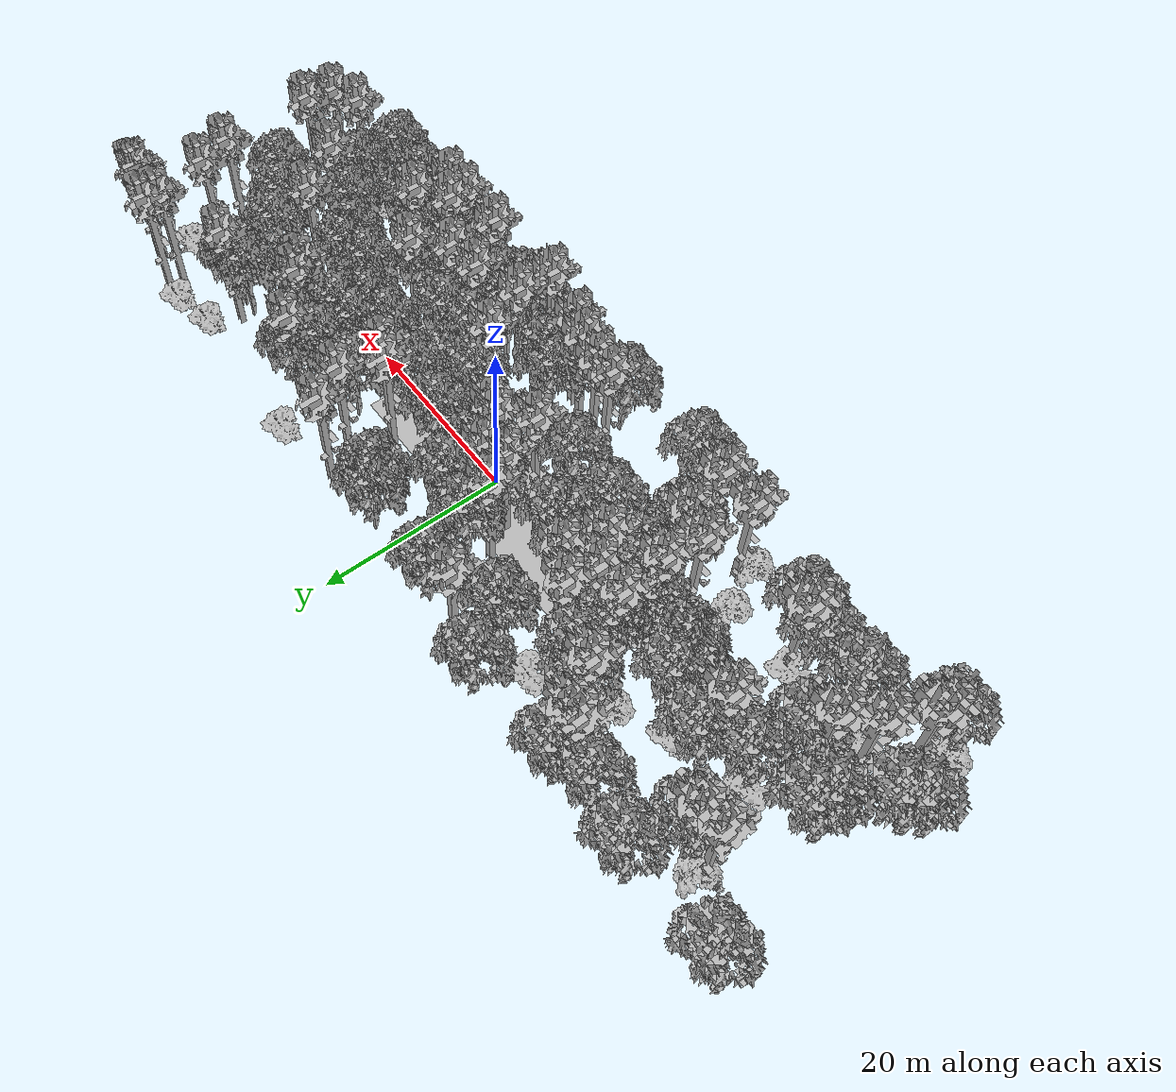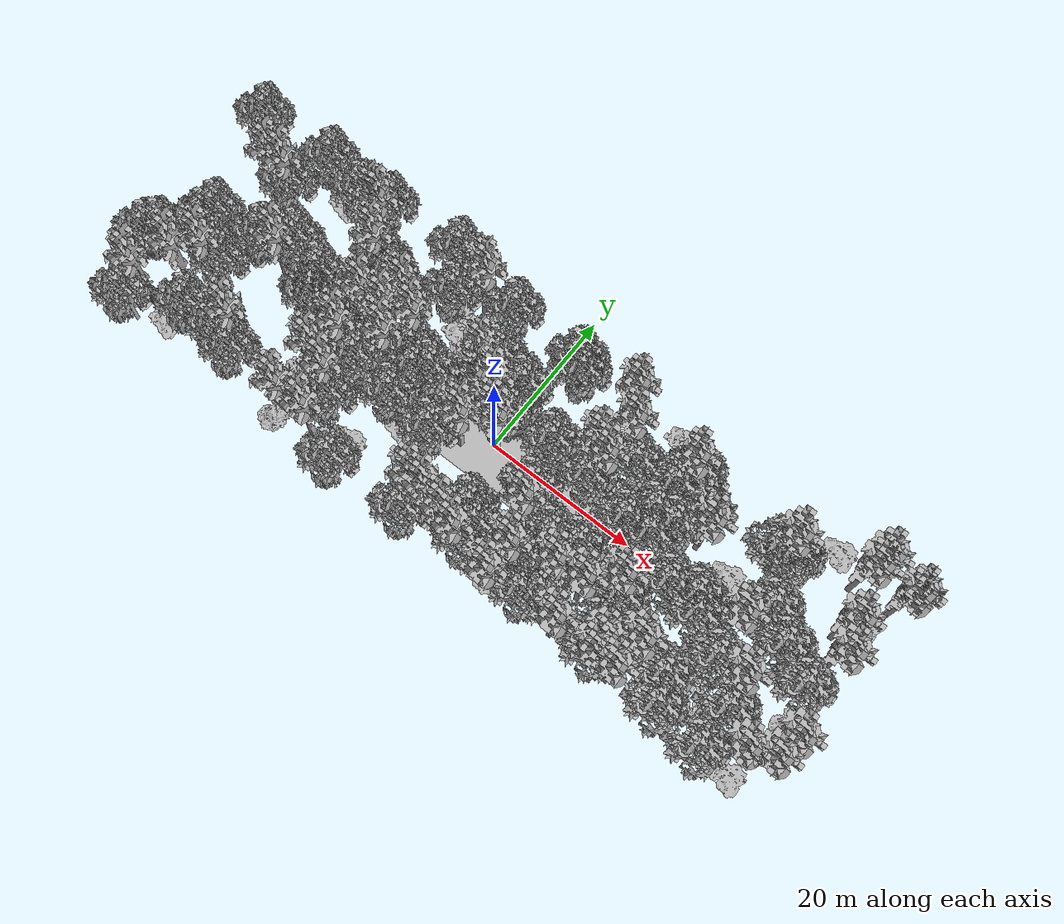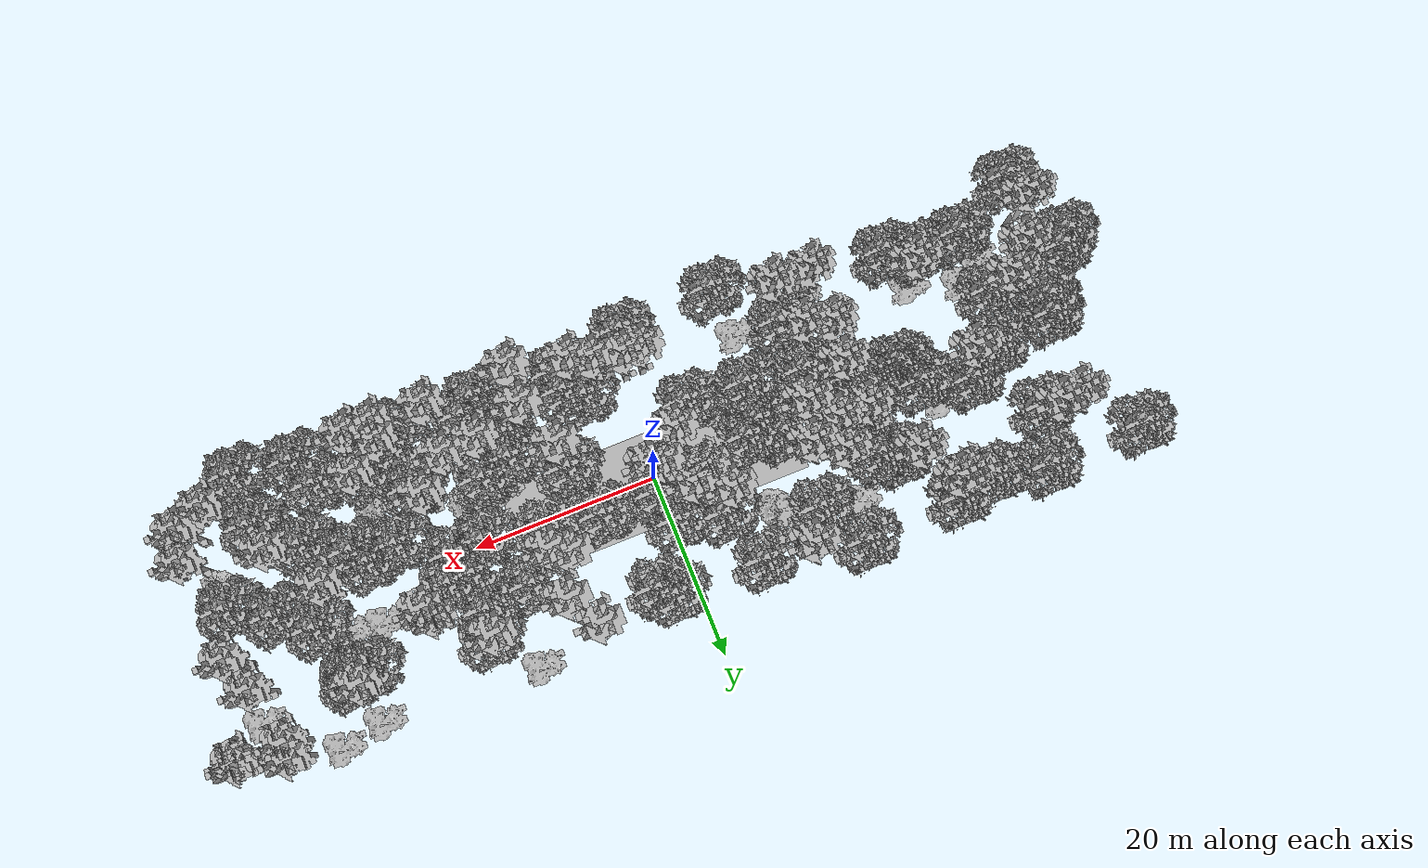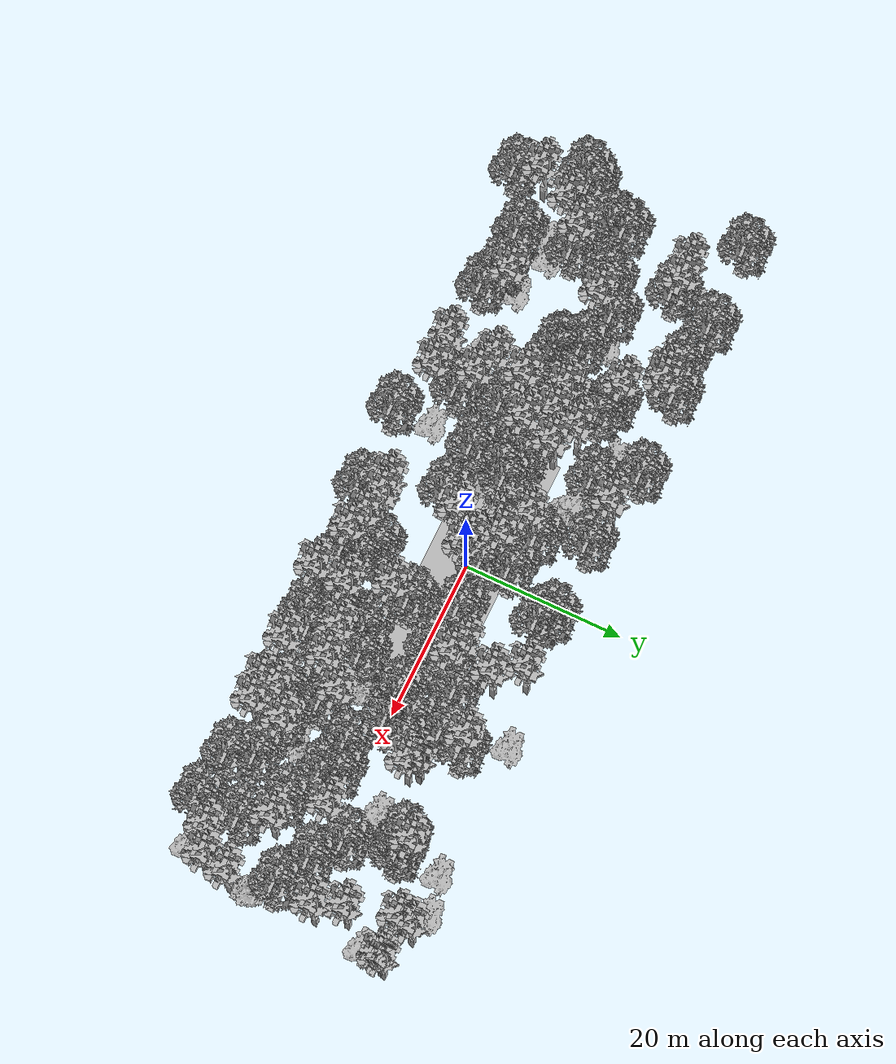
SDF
<sdf version="1.7">
    <world name="default">
        <plugin name="mrs_gazebo_static_transform_republisher_plugin" filename="libMrsGazeboCommonResources_StaticTransformRepublisher.so"/>
        <spherical_coordinates>
            <surface_model>EARTH_WGS84</surface_model>
            <latitude_deg>47.3977</latitude_deg>
            <longitude_deg>8.54559</longitude_deg>
            <elevation>0</elevation>
            <heading_deg>0</heading_deg>
        </spherical_coordinates>
        <physics name="default_physics" default="0" type="ode">
            <ode>
                <solver>
                    <type>quick</type>
                    <iters>10</iters>
                    <sor>1.3</sor>
                    <use_dynamic_moi_rescaling>0</use_dynamic_moi_rescaling>
                </solver>
                <constraints>
                    <cfm>0</cfm>
                    <erp>0.2</erp>
                    <contact_max_correcting_vel>1000</contact_max_correcting_vel>
                    <contact_surface_layer>0.001</contact_surface_layer>
                </constraints>
            </ode>
            <max_step_size>0.004</max_step_size>
            <real_time_factor>1</real_time_factor>
            <real_time_update_rate>250</real_time_update_rate>
        </physics>
        <scene>
            <shadows>0</shadows>
            <ambient>0.4 0.4 0.4 1</ambient>
            <background>0.7 0.7 0.7 1</background>
        </scene>
        <light name="sun" type="directional">
            <pose>0 0 1000 0.4 0.2 0</pose>
            <diffuse>1 1 1 1</diffuse>
            <specular>0.6 0.6 0.6 1</specular>
            <direction>0.1 0.1 -0.9</direction>
            <attenuation>
                <range>20</range>
                <constant>0.5</constant>
                <linear>0.01</linear>
                <quadratic>0.001</quadratic>
            </attenuation>
            <cast_shadows>1</cast_shadows>
            <spot>
                <inner_angle>0</inner_angle>
                <outer_angle>0</outer_angle>
                <falloff>0</falloff>
            </spot>
        </light>
        <model name="ground_plane">
            <static>1</static>
            <link name="link">
                <collision name="collision">
                    <pose>-50 0 0 0 -0 0</pose>
                    <geometry>
                        <plane>
                            <normal>0 0 1</normal>
                            <size>100 100</size>
                        </plane>
                    </geometry>
                    <surface>
                        <contact>
                            <ode>
                                <min_depth>0.01</min_depth>
                                <max_vel>0</max_vel>
                            </ode>
                        </contact>
                        <friction>
                            <ode/>
                            <torsional>
                                <ode/>
                            </torsional>
                        </friction>
                        <bounce/>
                    </surface>
                    <max_contacts>10</max_contacts>
                </collision>
                <visual name="grass">
                    <pose>0 0 0 0 -0 0</pose>
                    <cast_shadows>0</cast_shadows>
                    <geometry>
                        <mesh>
                            <scale>0.5814285714285714 0.18142857142857144 0.1</scale>
                            <uri>file://grass_plane/meshes/grass_plane.dae</uri>
                        </mesh>
                    </geometry>
                </visual>
                <self_collide>0</self_collide>
                <enable_wind>0</enable_wind>
                <kinematic>0</kinematic>
            </link>
        </model>
        <model name="the_void">
            <static>1</static>
            <link name="link">
                <pose>0 0 0.1 0 -0 0</pose>
                <visual name="the_void">
                    <pose>0 0 2 0 -0 0</pose>
                    <geometry>
                        <sphere>
                            <radius>0.25</radius>
                        </sphere>
                    </geometry>
                    <material>
                        <script>
                            <uri>file://media/materials/scripts/Gazebo.material</uri>
                            <name>Gazebo/Black</name>
                        </script>
                    </material>
                </visual>
                <self_collide>0</self_collide>
                <enable_wind>0</enable_wind>
                <kinematic>0</kinematic>
            </link>
            <pose>-1000 -1000 0 0 -0 0</pose>
        </model>
        <gui fullscreen="0">
            <camera name="camera">
                <pose>35.1577 98.6044 40.0204 0 0.407996 -1.99761</pose>
                <view_controller>orbit</view_controller>
                <projection_type>perspective</projection_type>
            </camera>
        </gui>
        <plugin name="mrs_gazebo_rviz_cam_synchronizer" filename="libMrsGazeboCommonResources_RvizCameraSynchronizer.so">
            <target_frame_id>gazebo_user_camera</target_frame_id>
            <world_origin_frame_id>uav1/gps_origin</world_origin_frame_id>
            <frame_to_follow>uav1</frame_to_follow>
        </plugin>
        <gravity>0 0 -9.8066</gravity>
        <magnetic_field>6e-06 2.3e-05 -4.2e-05</magnetic_field>
        <atmosphere type="adiabatic"/>
        <wind/>
        <model name="Tree 0">
            <static>1</static>
            <pose>9.00530453660214 -13.77287635051631 0 1.57079 -0 0</pose>
            <link name="link">
                <pose>0 0 0 0 -0 0</pose>
                <collision name="collision">
                    <geometry>
                        <mesh>
                            <scale>3 2 3</scale>
                            <uri>model://tree_3/meshes/tree_3.obj</uri>
                        </mesh>
                    </geometry>
                    <max_contacts>10</max_contacts>
                    <surface>
                        <contact>
                            <ode/>
                        </contact>
                        <bounce/>
                        <friction>
                            <torsional>
                                <ode/>
                            </torsional>
                            <ode/>
                        </friction>
                    </surface>
                </collision>
                <visual name="visual">
                    <geometry>
                        <mesh>
                            <scale>3 2 3</scale>
                            <uri>model://tree_3/meshes/tree_3.obj</uri>
                        </mesh>
                    </geometry>
                </visual>
                <self_collide>0</self_collide>
                <enable_wind>0</enable_wind>
                <kinematic>0</kinematic>
            </link>
        </model>
        <model name="Tree 1">
            <static>1</static>
            <pose>40.46276296069715 -0.10571722466873723 0 1.57079 -0 0</pose>
            <link name="link">
                <pose>0 0 0 0 -0 0</pose>
                <collision name="collision">
                    <geometry>
                        <mesh>
                            <scale>3.5 5 3.5</scale>
                            <uri>model://tree_2/meshes/tree_2.obj</uri>
                        </mesh>
                    </geometry>
                    <max_contacts>10</max_contacts>
                    <surface>
                        <contact>
                            <ode/>
                        </contact>
                        <bounce/>
                        <friction>
                            <torsional>
                                <ode/>
                            </torsional>
                            <ode/>
                        </friction>
                    </surface>
                </collision>
                <visual name="visual">
                    <geometry>
                        <mesh>
                            <scale>3.5 5 3.5</scale>
                            <uri>model://tree_2/meshes/tree_2.obj</uri>
                        </mesh>
                    </geometry>
                </visual>
                <self_collide>0</self_collide>
                <enable_wind>0</enable_wind>
                <kinematic>0</kinematic>
            </link>
        </model>
        <model name="Tree 2">
            <static>1</static>
            <pose>29.856909890999887 -1.691752062501724 0 1.57079 -0 0</pose>
            <link name="link">
                <pose>0 0 0 0 -0 0</pose>
                <collision name="collision">
                    <geometry>
                        <mesh>
                            <scale>3.5 5 3.5</scale>
                            <uri>model://tree_2/meshes/tree_2.obj</uri>
                        </mesh>
                    </geometry>
                    <max_contacts>10</max_contacts>
                    <surface>
                        <contact>
                            <ode/>
                        </contact>
                        <bounce/>
                        <friction>
                            <torsional>
                                <ode/>
                            </torsional>
                            <ode/>
                        </friction>
                    </surface>
                </collision>
                <visual name="visual">
                    <geometry>
                        <mesh>
                            <scale>3.5 5 3.5</scale>
                            <uri>model://tree_2/meshes/tree_2.obj</uri>
                        </mesh>
                    </geometry>
                </visual>
                <self_collide>0</self_collide>
                <enable_wind>0</enable_wind>
                <kinematic>0</kinematic>
            </link>
        </model>
        <model name="Tree 3">
            <static>1</static>
            <pose>27.00765666073883 -9.12259556007964 0 1.57079 -0 0</pose>
            <link name="link">
                <pose>0 0 0 0 -0 0</pose>
                <collision name="collision">
                    <geometry>
                        <mesh>
                            <scale>3 2 3</scale>
                            <uri>model://tree_3/meshes/tree_3.obj</uri>
                        </mesh>
                    </geometry>
                    <max_contacts>10</max_contacts>
                    <surface>
                        <contact>
                            <ode/>
                        </contact>
                        <bounce/>
                        <friction>
                            <torsional>
                                <ode/>
                            </torsional>
                            <ode/>
                        </friction>
                    </surface>
                </collision>
                <visual name="visual">
                    <geometry>
                        <mesh>
                            <scale>3 2 3</scale>
                            <uri>model://tree_3/meshes/tree_3.obj</uri>
                        </mesh>
                    </geometry>
                </visual>
                <self_collide>0</self_collide>
                <enable_wind>0</enable_wind>
                <kinematic>0</kinematic>
            </link>
        </model>
        <model name="Tree 4">
            <static>1</static>
            <pose>-3.1789962692227647 -11.16017621482938 0 1.57079 -0 0</pose>
            <link name="link">
                <pose>0 0 0 0 -0 0</pose>
                <collision name="collision">
                    <geometry>
                        <mesh>
                            <scale>3.5 5 3.5</scale>
                            <uri>model://tree_9/meshes/tree_9.obj</uri>
                        </mesh>
                    </geometry>
                    <max_contacts>10</max_contacts>
                    <surface>
                        <contact>
                            <ode/>
                        </contact>
                        <bounce/>
                        <friction>
                            <torsional>
                                <ode/>
                            </torsional>
                            <ode/>
                        </friction>
                    </surface>
                </collision>
                <visual name="visual">
                    <geometry>
                        <mesh>
                            <scale>3.5 5 3.5</scale>
                            <uri>model://tree_9/meshes/tree_9.obj</uri>
                        </mesh>
                    </geometry>
                </visual>
                <self_collide>0</self_collide>
                <enable_wind>0</enable_wind>
                <kinematic>0</kinematic>
            </link>
        </model>
        <model name="Tree 5">
            <static>1</static>
            <pose>12.564143722136464 9.461817279486056 0 1.57079 -0 0</pose>
            <link name="link">
                <pose>0 0 0 0 -0 0</pose>
                <collision name="collision">
                    <geometry>
                        <mesh>
                            <scale>3.5 5 3.5</scale>
                            <uri>model://tree_9/meshes/tree_9.obj</uri>
                        </mesh>
                    </geometry>
                    <max_contacts>10</max_contacts>
                    <surface>
                        <contact>
                            <ode/>
                        </contact>
                        <bounce/>
                        <friction>
                            <torsional>
                                <ode/>
                            </torsional>
                            <ode/>
                        </friction>
                    </surface>
                </collision>
                <visual name="visual">
                    <geometry>
                        <mesh>
                            <scale>3.5 5 3.5</scale>
                            <uri>model://tree_9/meshes/tree_9.obj</uri>
                        </mesh>
                    </geometry>
                </visual>
                <self_collide>0</self_collide>
                <enable_wind>0</enable_wind>
                <kinematic>0</kinematic>
            </link>
        </model>
        <model name="Tree 6">
            <static>1</static>
            <pose>-34.02520586374568 12.693943289851944 0 1.57079 -0 0</pose>
            <link name="link">
                <pose>0 0 0 0 -0 0</pose>
                <collision name="collision">
                    <geometry>
                        <mesh>
                            <scale>3 2 3</scale>
                            <uri>model://tree_3/meshes/tree_3.obj</uri>
                        </mesh>
                    </geometry>
                    <max_contacts>10</max_contacts>
                    <surface>
                        <contact>
                            <ode/>
                        </contact>
                        <bounce/>
                        <friction>
                            <torsional>
                                <ode/>
                            </torsional>
                            <ode/>
                        </friction>
                    </surface>
                </collision>
                <visual name="visual">
                    <geometry>
                        <mesh>
                            <scale>3 2 3</scale>
                            <uri>model://tree_3/meshes/tree_3.obj</uri>
                        </mesh>
                    </geometry>
                </visual>
                <self_collide>0</self_collide>
                <enable_wind>0</enable_wind>
                <kinematic>0</kinematic>
            </link>
        </model>
        <model name="Tree 7">
            <static>1</static>
            <pose>-13.759992427828962 -11.14273678522622 0 1.57079 -0 0</pose>
            <link name="link">
                <pose>0 0 0 0 -0 0</pose>
                <collision name="collision">
                    <geometry>
                        <mesh>
                            <scale>3 2 3</scale>
                            <uri>model://tree_3/meshes/tree_3.obj</uri>
                        </mesh>
                    </geometry>
                    <max_contacts>10</max_contacts>
                    <surface>
                        <contact>
                            <ode/>
                        </contact>
                        <bounce/>
                        <friction>
                            <torsional>
                                <ode/>
                            </torsional>
                            <ode/>
                        </friction>
                    </surface>
                </collision>
                <visual name="visual">
                    <geometry>
                        <mesh>
                            <scale>3 2 3</scale>
                            <uri>model://tree_3/meshes/tree_3.obj</uri>
                        </mesh>
                    </geometry>
                </visual>
                <self_collide>0</self_collide>
                <enable_wind>0</enable_wind>
                <kinematic>0</kinematic>
            </link>
        </model>
        <model name="Tree 8">
            <static>1</static>
            <pose>43.079067587226476 12.156543890776938 0 1.57079 -0 0</pose>
            <link name="link">
                <pose>0 0 0 0 -0 0</pose>
                <collision name="collision">
                    <geometry>
                        <mesh>
                            <scale>3.5 5 3.5</scale>
                            <uri>model://tree_9/meshes/tree_9.obj</uri>
                        </mesh>
                    </geometry>
                    <max_contacts>10</max_contacts>
                    <surface>
                        <contact>
                            <ode/>
                        </contact>
                        <bounce/>
                        <friction>
                            <torsional>
                                <ode/>
                            </torsional>
                            <ode/>
                        </friction>
                    </surface>
                </collision>
                <visual name="visual">
                    <geometry>
                        <mesh>
                            <scale>3.5 5 3.5</scale>
                            <uri>model://tree_9/meshes/tree_9.obj</uri>
                        </mesh>
                    </geometry>
                </visual>
                <self_collide>0</self_collide>
                <enable_wind>0</enable_wind>
                <kinematic>0</kinematic>
            </link>
        </model>
        <model name="Tree 9">
            <static>1</static>
            <pose>-5.143246595416393 7.067504007709154 0 1.57079 -0 0</pose>
            <link name="link">
                <pose>0 0 0 0 -0 0</pose>
                <collision name="collision">
                    <geometry>
                        <mesh>
                            <scale>3.5 5 3.5</scale>
                            <uri>model://tree_2/meshes/tree_2.obj</uri>
                        </mesh>
                    </geometry>
                    <max_contacts>10</max_contacts>
                    <surface>
                        <contact>
                            <ode/>
                        </contact>
                        <bounce/>
                        <friction>
                            <torsional>
                                <ode/>
                            </torsional>
                            <ode/>
                        </friction>
                    </surface>
                </collision>
                <visual name="visual">
                    <geometry>
                        <mesh>
                            <scale>3.5 5 3.5</scale>
                            <uri>model://tree_2/meshes/tree_2.obj</uri>
                        </mesh>
                    </geometry>
                </visual>
                <self_collide>0</self_collide>
                <enable_wind>0</enable_wind>
                <kinematic>0</kinematic>
            </link>
        </model>
        <model name="Tree 10">
            <static>1</static>
            <pose>-15.46027357171912 4.023113460201788 0 1.57079 -0 0</pose>
            <link name="link">
                <pose>0 0 0 0 -0 0</pose>
                <collision name="collision">
                    <geometry>
                        <mesh>
                            <scale>3.5 5 3.5</scale>
                            <uri>model://tree_9/meshes/tree_9.obj</uri>
                        </mesh>
                    </geometry>
                    <max_contacts>10</max_contacts>
                    <surface>
                        <contact>
                            <ode/>
                        </contact>
                        <bounce/>
                        <friction>
                            <torsional>
                                <ode/>
                            </torsional>
                            <ode/>
                        </friction>
                    </surface>
                </collision>
                <visual name="visual">
                    <geometry>
                        <mesh>
                            <scale>3.5 5 3.5</scale>
                            <uri>model://tree_9/meshes/tree_9.obj</uri>
                        </mesh>
                    </geometry>
                </visual>
                <self_collide>0</self_collide>
                <enable_wind>0</enable_wind>
                <kinematic>0</kinematic>
            </link>
        </model>
        <model name="Tree 11">
            <static>1</static>
            <pose>31.30791522382289 3.5100560860764567 0 1.57079 -0 0</pose>
            <link name="link">
                <pose>0 0 0 0 -0 0</pose>
                <collision name="collision">
                    <geometry>
                        <mesh>
                            <scale>3 2 3</scale>
                            <uri>model://tree_3/meshes/tree_3.obj</uri>
                        </mesh>
                    </geometry>
                    <max_contacts>10</max_contacts>
                    <surface>
                        <contact>
                            <ode/>
                        </contact>
                        <bounce/>
                        <friction>
                            <torsional>
                                <ode/>
                            </torsional>
                            <ode/>
                        </friction>
                    </surface>
                </collision>
                <visual name="visual">
                    <geometry>
                        <mesh>
                            <scale>3 2 3</scale>
                            <uri>model://tree_3/meshes/tree_3.obj</uri>
                        </mesh>
                    </geometry>
                </visual>
                <self_collide>0</self_collide>
                <enable_wind>0</enable_wind>
                <kinematic>0</kinematic>
            </link>
        </model>
        <model name="Tree 12">
            <static>1</static>
            <pose>-14.131242068738842 11.019451765315992 0 1.57079 -0 0</pose>
            <link name="link">
                <pose>0 0 0 0 -0 0</pose>
                <collision name="collision">
                    <geometry>
                        <mesh>
                            <scale>4 2.5 4</scale>
                            <uri>model://tree_1/meshes/tree_1.obj</uri>
                        </mesh>
                    </geometry>
                    <max_contacts>10</max_contacts>
                    <surface>
                        <contact>
                            <ode/>
                        </contact>
                        <bounce/>
                        <friction>
                            <torsional>
                                <ode/>
                            </torsional>
                            <ode/>
                        </friction>
                    </surface>
                </collision>
                <visual name="visual">
                    <geometry>
                        <mesh>
                            <scale>4 2.5 4</scale>
                            <uri>model://tree_1/meshes/tree_1.obj</uri>
                        </mesh>
                    </geometry>
                </visual>
                <self_collide>0</self_collide>
                <enable_wind>0</enable_wind>
                <kinematic>0</kinematic>
            </link>
        </model>
        <model name="Tree 13">
            <static>1</static>
            <pose>48.193910877338 12.449965114180863 0 1.57079 -0 0</pose>
            <link name="link">
                <pose>0 0 0 0 -0 0</pose>
                <collision name="collision">
                    <geometry>
                        <mesh>
                            <scale>3.5 5 3.5</scale>
                            <uri>model://tree_9/meshes/tree_9.obj</uri>
                        </mesh>
                    </geometry>
                    <max_contacts>10</max_contacts>
                    <surface>
                        <contact>
                            <ode/>
                        </contact>
                        <bounce/>
                        <friction>
                            <torsional>
                                <ode/>
                            </torsional>
                            <ode/>
                        </friction>
                    </surface>
                </collision>
                <visual name="visual">
                    <geometry>
                        <mesh>
                            <scale>3.5 5 3.5</scale>
                            <uri>model://tree_9/meshes/tree_9.obj</uri>
                        </mesh>
                    </geometry>
                </visual>
                <self_collide>0</self_collide>
                <enable_wind>0</enable_wind>
                <kinematic>0</kinematic>
            </link>
        </model>
        <model name="Tree 14">
            <static>1</static>
            <pose>-5.678869970176962 -4.981280188310555 0 1.57079 -0 0</pose>
            <link name="link">
                <pose>0 0 0 0 -0 0</pose>
                <collision name="collision">
                    <geometry>
                        <mesh>
                            <scale>3.5 5 3.5</scale>
                            <uri>model://tree_2/meshes/tree_2.obj</uri>
                        </mesh>
                    </geometry>
                    <max_contacts>10</max_contacts>
                    <surface>
                        <contact>
                            <ode/>
                        </contact>
                        <bounce/>
                        <friction>
                            <torsional>
                                <ode/>
                            </torsional>
                            <ode/>
                        </friction>
                    </surface>
                </collision>
                <visual name="visual">
                    <geometry>
                        <mesh>
                            <scale>3.5 5 3.5</scale>
                            <uri>model://tree_2/meshes/tree_2.obj</uri>
                        </mesh>
                    </geometry>
                </visual>
                <self_collide>0</self_collide>
                <enable_wind>0</enable_wind>
                <kinematic>0</kinematic>
            </link>
        </model>
        <model name="Tree 15">
            <static>1</static>
            <pose>-27.600010558652393 14.27166555361124 0 1.57079 -0 0</pose>
            <link name="link">
                <pose>0 0 0 0 -0 0</pose>
                <collision name="collision">
                    <geometry>
                        <mesh>
                            <scale>3.5 5 3.5</scale>
                            <uri>model://tree_2/meshes/tree_2.obj</uri>
                        </mesh>
                    </geometry>
                    <max_contacts>10</max_contacts>
                    <surface>
                        <contact>
                            <ode/>
                        </contact>
                        <bounce/>
                        <friction>
                            <torsional>
                                <ode/>
                            </torsional>
                            <ode/>
                        </friction>
                    </surface>
                </collision>
                <visual name="visual">
                    <geometry>
                        <mesh>
                            <scale>3.5 5 3.5</scale>
                            <uri>model://tree_2/meshes/tree_2.obj</uri>
                        </mesh>
                    </geometry>
                </visual>
                <self_collide>0</self_collide>
                <enable_wind>0</enable_wind>
                <kinematic>0</kinematic>
            </link>
        </model>
        <model name="Tree 16">
            <static>1</static>
            <pose>20.631699623204923 10.03381341728118 0 1.57079 -0 0</pose>
            <link name="link">
                <pose>0 0 0 0 -0 0</pose>
                <collision name="collision">
                    <geometry>
                        <mesh>
                            <scale>3.5 5 3.5</scale>
                            <uri>model://tree_9/meshes/tree_9.obj</uri>
                        </mesh>
                    </geometry>
                    <max_contacts>10</max_contacts>
                    <surface>
                        <contact>
                            <ode/>
                        </contact>
                        <bounce/>
                        <friction>
                            <torsional>
                                <ode/>
                            </torsional>
                            <ode/>
                        </friction>
                    </surface>
                </collision>
                <visual name="visual">
                    <geometry>
                        <mesh>
                            <scale>3.5 5 3.5</scale>
                            <uri>model://tree_9/meshes/tree_9.obj</uri>
                        </mesh>
                    </geometry>
                </visual>
                <self_collide>0</self_collide>
                <enable_wind>0</enable_wind>
                <kinematic>0</kinematic>
            </link>
        </model>
        <model name="Tree 17">
            <static>1</static>
            <pose>21.40325206784756 9.958257367513571 0 1.57079 -0 0</pose>
            <link name="link">
                <pose>0 0 0 0 -0 0</pose>
                <collision name="collision">
                    <geometry>
                        <mesh>
                            <scale>3.5 5 3.5</scale>
                            <uri>model://tree_2/meshes/tree_2.obj</uri>
                        </mesh>
                    </geometry>
                    <max_contacts>10</max_contacts>
                    <surface>
                        <contact>
                            <ode/>
                        </contact>
                        <bounce/>
                        <friction>
                            <torsional>
                                <ode/>
                            </torsional>
                            <ode/>
                        </friction>
                    </surface>
                </collision>
                <visual name="visual">
                    <geometry>
                        <mesh>
                            <scale>3.5 5 3.5</scale>
                            <uri>model://tree_2/meshes/tree_2.obj</uri>
                        </mesh>
                    </geometry>
                </visual>
                <self_collide>0</self_collide>
                <enable_wind>0</enable_wind>
                <kinematic>0</kinematic>
            </link>
        </model>
        <model name="Tree 18">
            <static>1</static>
            <pose>-37.26954169039817 14.598448052054668 0 1.57079 -0 0</pose>
            <link name="link">
                <pose>0 0 0 0 -0 0</pose>
                <collision name="collision">
                    <geometry>
                        <mesh>
                            <scale>3.5 5 3.5</scale>
                            <uri>model://tree_2/meshes/tree_2.obj</uri>
                        </mesh>
                    </geometry>
                    <max_contacts>10</max_contacts>
                    <surface>
                        <contact>
                            <ode/>
                        </contact>
                        <bounce/>
                        <friction>
                            <torsional>
                                <ode/>
                            </torsional>
                            <ode/>
                        </friction>
                    </surface>
                </collision>
                <visual name="visual">
                    <geometry>
                        <mesh>
                            <scale>3.5 5 3.5</scale>
                            <uri>model://tree_2/meshes/tree_2.obj</uri>
                        </mesh>
                    </geometry>
                </visual>
                <self_collide>0</self_collide>
                <enable_wind>0</enable_wind>
                <kinematic>0</kinematic>
            </link>
        </model>
        <model name="Tree 19">
            <static>1</static>
            <pose>39.784866254239205 13.94450292007286 0 1.57079 -0 0</pose>
            <link name="link">
                <pose>0 0 0 0 -0 0</pose>
                <collision name="collision">
                    <geometry>
                        <mesh>
                            <scale>3 2 3</scale>
                            <uri>model://tree_3/meshes/tree_3.obj</uri>
                        </mesh>
                    </geometry>
                    <max_contacts>10</max_contacts>
                    <surface>
                        <contact>
                            <ode/>
                        </contact>
                        <bounce/>
                        <friction>
                            <torsional>
                                <ode/>
                            </torsional>
                            <ode/>
                        </friction>
                    </surface>
                </collision>
                <visual name="visual">
                    <geometry>
                        <mesh>
                            <scale>3 2 3</scale>
                            <uri>model://tree_3/meshes/tree_3.obj</uri>
                        </mesh>
                    </geometry>
                </visual>
                <self_collide>0</self_collide>
                <enable_wind>0</enable_wind>
                <kinematic>0</kinematic>
            </link>
        </model>
        <model name="Tree 20">
            <static>1</static>
            <pose>46.024011212950896 -11.057480264774966 0 1.57079 -0 0</pose>
            <link name="link">
                <pose>0 0 0 0 -0 0</pose>
                <collision name="collision">
                    <geometry>
                        <mesh>
                            <scale>3.5 5 3.5</scale>
                            <uri>model://tree_9/meshes/tree_9.obj</uri>
                        </mesh>
                    </geometry>
                    <max_contacts>10</max_contacts>
                    <surface>
                        <contact>
                            <ode/>
                        </contact>
                        <bounce/>
                        <friction>
                            <torsional>
                                <ode/>
                            </torsional>
                            <ode/>
                        </friction>
                    </surface>
                </collision>
                <visual name="visual">
                    <geometry>
                        <mesh>
                            <scale>3.5 5 3.5</scale>
                            <uri>model://tree_9/meshes/tree_9.obj</uri>
                        </mesh>
                    </geometry>
                </visual>
                <self_collide>0</self_collide>
                <enable_wind>0</enable_wind>
                <kinematic>0</kinematic>
            </link>
        </model>
        <model name="Tree 21">
            <static>1</static>
            <pose>-27.09896817922239 -0.7278361053604065 0 1.57079 -0 0</pose>
            <link name="link">
                <pose>0 0 0 0 -0 0</pose>
                <collision name="collision">
                    <geometry>
                        <mesh>
                            <scale>3.5 5 3.5</scale>
                            <uri>model://tree_2/meshes/tree_2.obj</uri>
                        </mesh>
                    </geometry>
                    <max_contacts>10</max_contacts>
                    <surface>
                        <contact>
                            <ode/>
                        </contact>
                        <bounce/>
                        <friction>
                            <torsional>
                                <ode/>
                            </torsional>
                            <ode/>
                        </friction>
                    </surface>
                </collision>
                <visual name="visual">
                    <geometry>
                        <mesh>
                            <scale>3.5 5 3.5</scale>
                            <uri>model://tree_2/meshes/tree_2.obj</uri>
                        </mesh>
                    </geometry>
                </visual>
                <self_collide>0</self_collide>
                <enable_wind>0</enable_wind>
                <kinematic>0</kinematic>
            </link>
        </model>
        <model name="Tree 22">
            <static>1</static>
            <pose>-38.229435161918374 -7.49622511838539 0 1.57079 -0 0</pose>
            <link name="link">
                <pose>0 0 0 0 -0 0</pose>
                <collision name="collision">
                    <geometry>
                        <mesh>
                            <scale>3 2 3</scale>
                            <uri>model://tree_3/meshes/tree_3.obj</uri>
                        </mesh>
                    </geometry>
                    <max_contacts>10</max_contacts>
                    <surface>
                        <contact>
                            <ode/>
                        </contact>
                        <bounce/>
                        <friction>
                            <torsional>
                                <ode/>
                            </torsional>
                            <ode/>
                        </friction>
                    </surface>
                </collision>
                <visual name="visual">
                    <geometry>
                        <mesh>
                            <scale>3 2 3</scale>
                            <uri>model://tree_3/meshes/tree_3.obj</uri>
                        </mesh>
                    </geometry>
                </visual>
                <self_collide>0</self_collide>
                <enable_wind>0</enable_wind>
                <kinematic>0</kinematic>
            </link>
        </model>
        <model name="Tree 23">
            <static>1</static>
            <pose>-2.088435421180897 2.185330463497394 0 1.57079 -0 0</pose>
            <link name="link">
                <pose>0 0 0 0 -0 0</pose>
                <collision name="collision">
                    <geometry>
                        <mesh>
                            <scale>3.5 5 3.5</scale>
                            <uri>model://tree_2/meshes/tree_2.obj</uri>
                        </mesh>
                    </geometry>
                    <max_contacts>10</max_contacts>
                    <surface>
                        <contact>
                            <ode/>
                        </contact>
                        <bounce/>
                        <friction>
                            <torsional>
                                <ode/>
                            </torsional>
                            <ode/>
                        </friction>
                    </surface>
                </collision>
                <visual name="visual">
                    <geometry>
                        <mesh>
                            <scale>3.5 5 3.5</scale>
                            <uri>model://tree_2/meshes/tree_2.obj</uri>
                        </mesh>
                    </geometry>
                </visual>
                <self_collide>0</self_collide>
                <enable_wind>0</enable_wind>
                <kinematic>0</kinematic>
            </link>
        </model>
        <model name="Tree 24">
            <static>1</static>
            <pose>28.347638143475976 -7.713547740371126 0 1.57079 -0 0</pose>
            <link name="link">
                <pose>0 0 0 0 -0 0</pose>
                <collision name="collision">
                    <geometry>
                        <mesh>
                            <scale>4 2.5 4</scale>
                            <uri>model://tree_1/meshes/tree_1.obj</uri>
                        </mesh>
                    </geometry>
                    <max_contacts>10</max_contacts>
                    <surface>
                        <contact>
                            <ode/>
                        </contact>
                        <bounce/>
                        <friction>
                            <torsional>
                                <ode/>
                            </torsional>
                            <ode/>
                        </friction>
                    </surface>
                </collision>
                <visual name="visual">
                    <geometry>
                        <mesh>
                            <scale>4 2.5 4</scale>
                            <uri>model://tree_1/meshes/tree_1.obj</uri>
                        </mesh>
                    </geometry>
                </visual>
                <self_collide>0</self_collide>
                <enable_wind>0</enable_wind>
                <kinematic>0</kinematic>
            </link>
        </model>
        <model name="Tree 25">
            <static>1</static>
            <pose>-21.982230829824633 -12.386703666407453 0 1.57079 -0 0</pose>
            <link name="link">
                <pose>0 0 0 0 -0 0</pose>
                <collision name="collision">
                    <geometry>
                        <mesh>
                            <scale>3.5 5 3.5</scale>
                            <uri>model://tree_9/meshes/tree_9.obj</uri>
                        </mesh>
                    </geometry>
                    <max_contacts>10</max_contacts>
                    <surface>
                        <contact>
                            <ode/>
                        </contact>
                        <bounce/>
                        <friction>
                            <torsional>
                                <ode/>
                            </torsional>
                            <ode/>
                        </friction>
                    </surface>
                </collision>
                <visual name="visual">
                    <geometry>
                        <mesh>
                            <scale>3.5 5 3.5</scale>
                            <uri>model://tree_9/meshes/tree_9.obj</uri>
                        </mesh>
                    </geometry>
                </visual>
                <self_collide>0</self_collide>
                <enable_wind>0</enable_wind>
                <kinematic>0</kinematic>
            </link>
        </model>
        <model name="Tree 26">
            <static>1</static>
            <pose>-17.479445971545033 -9.050754357278805 0 1.57079 -0 0</pose>
            <link name="link">
                <pose>0 0 0 0 -0 0</pose>
                <collision name="collision">
                    <geometry>
                        <mesh>
                            <scale>3.5 5 3.5</scale>
                            <uri>model://tree_2/meshes/tree_2.obj</uri>
                        </mesh>
                    </geometry>
                    <max_contacts>10</max_contacts>
                    <surface>
                        <contact>
                            <ode/>
                        </contact>
                        <bounce/>
                        <friction>
                            <torsional>
                                <ode/>
                            </torsional>
                            <ode/>
                        </friction>
                    </surface>
                </collision>
                <visual name="visual">
                    <geometry>
                        <mesh>
                            <scale>3.5 5 3.5</scale>
                            <uri>model://tree_2/meshes/tree_2.obj</uri>
                        </mesh>
                    </geometry>
                </visual>
                <self_collide>0</self_collide>
                <enable_wind>0</enable_wind>
                <kinematic>0</kinematic>
            </link>
        </model>
        <model name="Tree 27">
            <static>1</static>
            <pose>-2.067097923247651 -14.235611379425244 0 1.57079 -0 0</pose>
            <link name="link">
                <pose>0 0 0 0 -0 0</pose>
                <collision name="collision">
                    <geometry>
                        <mesh>
                            <scale>3.5 5 3.5</scale>
                            <uri>model://tree_2/meshes/tree_2.obj</uri>
                        </mesh>
                    </geometry>
                    <max_contacts>10</max_contacts>
                    <surface>
                        <contact>
                            <ode/>
                        </contact>
                        <bounce/>
                        <friction>
                            <torsional>
                                <ode/>
                            </torsional>
                            <ode/>
                        </friction>
                    </surface>
                </collision>
                <visual name="visual">
                    <geometry>
                        <mesh>
                            <scale>3.5 5 3.5</scale>
                            <uri>model://tree_2/meshes/tree_2.obj</uri>
                        </mesh>
                    </geometry>
                </visual>
                <self_collide>0</self_collide>
                <enable_wind>0</enable_wind>
                <kinematic>0</kinematic>
            </link>
        </model>
        <model name="Tree 28">
            <static>1</static>
            <pose>13.895029403688497 -10.439070415187125 0 1.57079 -0 0</pose>
            <link name="link">
                <pose>0 0 0 0 -0 0</pose>
                <collision name="collision">
                    <geometry>
                        <mesh>
                            <scale>3.5 5 3.5</scale>
                            <uri>model://tree_2/meshes/tree_2.obj</uri>
                        </mesh>
                    </geometry>
                    <max_contacts>10</max_contacts>
                    <surface>
                        <contact>
                            <ode/>
                        </contact>
                        <bounce/>
                        <friction>
                            <torsional>
                                <ode/>
                            </torsional>
                            <ode/>
                        </friction>
                    </surface>
                </collision>
                <visual name="visual">
                    <geometry>
                        <mesh>
                            <scale>3.5 5 3.5</scale>
                            <uri>model://tree_2/meshes/tree_2.obj</uri>
                        </mesh>
                    </geometry>
                </visual>
                <self_collide>0</self_collide>
                <enable_wind>0</enable_wind>
                <kinematic>0</kinematic>
            </link>
        </model>
        <model name="Tree 29">
            <static>1</static>
            <pose>-21.935377720867585 2.63587096987899 0 1.57079 -0 0</pose>
            <link name="link">
                <pose>0 0 0 0 -0 0</pose>
                <collision name="collision">
                    <geometry>
                        <mesh>
                            <scale>3.5 5 3.5</scale>
                            <uri>model://tree_9/meshes/tree_9.obj</uri>
                        </mesh>
                    </geometry>
                    <max_contacts>10</max_contacts>
                    <surface>
                        <contact>
                            <ode/>
                        </contact>
                        <bounce/>
                        <friction>
                            <torsional>
                                <ode/>
                            </torsional>
                            <ode/>
                        </friction>
                    </surface>
                </collision>
                <visual name="visual">
                    <geometry>
                        <mesh>
                            <scale>3.5 5 3.5</scale>
                            <uri>model://tree_9/meshes/tree_9.obj</uri>
                        </mesh>
                    </geometry>
                </visual>
                <self_collide>0</self_collide>
                <enable_wind>0</enable_wind>
                <kinematic>0</kinematic>
            </link>
        </model>
        <model name="Tree 30">
            <static>1</static>
            <pose>23.091639120540904 3.3277202231098038 0 1.57079 -0 0</pose>
            <link name="link">
                <pose>0 0 0 0 -0 0</pose>
                <collision name="collision">
                    <geometry>
                        <mesh>
                            <scale>3.5 5 3.5</scale>
                            <uri>model://tree_2/meshes/tree_2.obj</uri>
                        </mesh>
                    </geometry>
                    <max_contacts>10</max_contacts>
                    <surface>
                        <contact>
                            <ode/>
                        </contact>
                        <bounce/>
                        <friction>
                            <torsional>
                                <ode/>
                            </torsional>
                            <ode/>
                        </friction>
                    </surface>
                </collision>
                <visual name="visual">
                    <geometry>
                        <mesh>
                            <scale>3.5 5 3.5</scale>
                            <uri>model://tree_2/meshes/tree_2.obj</uri>
                        </mesh>
                    </geometry>
                </visual>
                <self_collide>0</self_collide>
                <enable_wind>0</enable_wind>
                <kinematic>0</kinematic>
            </link>
        </model>
        <model name="Tree 31">
            <static>1</static>
            <pose>-19.215518709218156 9.99422568321122 0 1.57079 -0 0</pose>
            <link name="link">
                <pose>0 0 0 0 -0 0</pose>
                <collision name="collision">
                    <geometry>
                        <mesh>
                            <scale>3 2 3</scale>
                            <uri>model://tree_3/meshes/tree_3.obj</uri>
                        </mesh>
                    </geometry>
                    <max_contacts>10</max_contacts>
                    <surface>
                        <contact>
                            <ode/>
                        </contact>
                        <bounce/>
                        <friction>
                            <torsional>
                                <ode/>
                            </torsional>
                            <ode/>
                        </friction>
                    </surface>
                </collision>
                <visual name="visual">
                    <geometry>
                        <mesh>
                            <scale>3 2 3</scale>
                            <uri>model://tree_3/meshes/tree_3.obj</uri>
                        </mesh>
                    </geometry>
                </visual>
                <self_collide>0</self_collide>
                <enable_wind>0</enable_wind>
                <kinematic>0</kinematic>
            </link>
        </model>
        <model name="Tree 32">
            <static>1</static>
            <pose>44.138661586826174 -14.741700780972689 0 1.57079 -0 0</pose>
            <link name="link">
                <pose>0 0 0 0 -0 0</pose>
                <collision name="collision">
                    <geometry>
                        <mesh>
                            <scale>3 2 3</scale>
                            <uri>model://tree_3/meshes/tree_3.obj</uri>
                        </mesh>
                    </geometry>
                    <max_contacts>10</max_contacts>
                    <surface>
                        <contact>
                            <ode/>
                        </contact>
                        <bounce/>
                        <friction>
                            <torsional>
                                <ode/>
                            </torsional>
                            <ode/>
                        </friction>
                    </surface>
                </collision>
                <visual name="visual">
                    <geometry>
                        <mesh>
                            <scale>3 2 3</scale>
                            <uri>model://tree_3/meshes/tree_3.obj</uri>
                        </mesh>
                    </geometry>
                </visual>
                <self_collide>0</self_collide>
                <enable_wind>0</enable_wind>
                <kinematic>0</kinematic>
            </link>
        </model>
        <model name="Tree 33">
            <static>1</static>
            <pose>-31.519277581109108 13.345279460212982 0 1.57079 -0 0</pose>
            <link name="link">
                <pose>0 0 0 0 -0 0</pose>
                <collision name="collision">
                    <geometry>
                        <mesh>
                            <scale>3.5 5 3.5</scale>
                            <uri>model://tree_2/meshes/tree_2.obj</uri>
                        </mesh>
                    </geometry>
                    <max_contacts>10</max_contacts>
                    <surface>
                        <contact>
                            <ode/>
                        </contact>
                        <bounce/>
                        <friction>
                            <torsional>
                                <ode/>
                            </torsional>
                            <ode/>
                        </friction>
                    </surface>
                </collision>
                <visual name="visual">
                    <geometry>
                        <mesh>
                            <scale>3.5 5 3.5</scale>
                            <uri>model://tree_2/meshes/tree_2.obj</uri>
                        </mesh>
                    </geometry>
                </visual>
                <self_collide>0</self_collide>
                <enable_wind>0</enable_wind>
                <kinematic>0</kinematic>
            </link>
        </model>
        <model name="Tree 34">
            <static>1</static>
            <pose>25.53621532801921 6.1579300585820285 0 1.57079 -0 0</pose>
            <link name="link">
                <pose>0 0 0 0 -0 0</pose>
                <collision name="collision">
                    <geometry>
                        <mesh>
                            <scale>3.5 5 3.5</scale>
                            <uri>model://tree_9/meshes/tree_9.obj</uri>
                        </mesh>
                    </geometry>
                    <max_contacts>10</max_contacts>
                    <surface>
                        <contact>
                            <ode/>
                        </contact>
                        <bounce/>
                        <friction>
                            <torsional>
                                <ode/>
                            </torsional>
                            <ode/>
                        </friction>
                    </surface>
                </collision>
                <visual name="visual">
                    <geometry>
                        <mesh>
                            <scale>3.5 5 3.5</scale>
                            <uri>model://tree_9/meshes/tree_9.obj</uri>
                        </mesh>
                    </geometry>
                </visual>
                <self_collide>0</self_collide>
                <enable_wind>0</enable_wind>
                <kinematic>0</kinematic>
            </link>
        </model>
        <model name="Tree 35">
            <static>1</static>
            <pose>23.251892534134925 -11.243501988978359 0 1.57079 -0 0</pose>
            <link name="link">
                <pose>0 0 0 0 -0 0</pose>
                <collision name="collision">
                    <geometry>
                        <mesh>
                            <scale>3.5 5 3.5</scale>
                            <uri>model://tree_2/meshes/tree_2.obj</uri>
                        </mesh>
                    </geometry>
                    <max_contacts>10</max_contacts>
                    <surface>
                        <contact>
                            <ode/>
                        </contact>
                        <bounce/>
                        <friction>
                            <torsional>
                                <ode/>
                            </torsional>
                            <ode/>
                        </friction>
                    </surface>
                </collision>
                <visual name="visual">
                    <geometry>
                        <mesh>
                            <scale>3.5 5 3.5</scale>
                            <uri>model://tree_2/meshes/tree_2.obj</uri>
                        </mesh>
                    </geometry>
                </visual>
                <self_collide>0</self_collide>
                <enable_wind>0</enable_wind>
                <kinematic>0</kinematic>
            </link>
        </model>
        <model name="Tree 36">
            <static>1</static>
            <pose>-22.958534798195235 -13.691752555426627 0 1.57079 -0 0</pose>
            <link name="link">
                <pose>0 0 0 0 -0 0</pose>
                <collision name="collision">
                    <geometry>
                        <mesh>
                            <scale>4 2.5 4</scale>
                            <uri>model://tree_1/meshes/tree_1.obj</uri>
                        </mesh>
                    </geometry>
                    <max_contacts>10</max_contacts>
                    <surface>
                        <contact>
                            <ode/>
                        </contact>
                        <bounce/>
                        <friction>
                            <torsional>
                                <ode/>
                            </torsional>
                            <ode/>
                        </friction>
                    </surface>
                </collision>
                <visual name="visual">
                    <geometry>
                        <mesh>
                            <scale>4 2.5 4</scale>
                            <uri>model://tree_1/meshes/tree_1.obj</uri>
                        </mesh>
                    </geometry>
                </visual>
                <self_collide>0</self_collide>
                <enable_wind>0</enable_wind>
                <kinematic>0</kinematic>
            </link>
        </model>
        <model name="Tree 37">
            <static>1</static>
            <pose>27.978852720871515 -9.820839608483986 0 1.57079 -0 0</pose>
            <link name="link">
                <pose>0 0 0 0 -0 0</pose>
                <collision name="collision">
                    <geometry>
                        <mesh>
                            <scale>3.5 5 3.5</scale>
                            <uri>model://tree_9/meshes/tree_9.obj</uri>
                        </mesh>
                    </geometry>
                    <max_contacts>10</max_contacts>
                    <surface>
                        <contact>
                            <ode/>
                        </contact>
                        <bounce/>
                        <friction>
                            <torsional>
                                <ode/>
                            </torsional>
                            <ode/>
                        </friction>
                    </surface>
                </collision>
                <visual name="visual">
                    <geometry>
                        <mesh>
                            <scale>3.5 5 3.5</scale>
                            <uri>model://tree_9/meshes/tree_9.obj</uri>
                        </mesh>
                    </geometry>
                </visual>
                <self_collide>0</self_collide>
                <enable_wind>0</enable_wind>
                <kinematic>0</kinematic>
            </link>
        </model>
        <model name="Tree 38">
            <static>1</static>
            <pose>-40.646941504770325 -9.292980626108424 0 1.57079 -0 0</pose>
            <link name="link">
                <pose>0 0 0 0 -0 0</pose>
                <collision name="collision">
                    <geometry>
                        <mesh>
                            <scale>3 2 3</scale>
                            <uri>model://tree_3/meshes/tree_3.obj</uri>
                        </mesh>
                    </geometry>
                    <max_contacts>10</max_contacts>
                    <surface>
                        <contact>
                            <ode/>
                        </contact>
                        <bounce/>
                        <friction>
                            <torsional>
                                <ode/>
                            </torsional>
                            <ode/>
                        </friction>
                    </surface>
                </collision>
                <visual name="visual">
                    <geometry>
                        <mesh>
                            <scale>3 2 3</scale>
                            <uri>model://tree_3/meshes/tree_3.obj</uri>
                        </mesh>
                    </geometry>
                </visual>
                <self_collide>0</self_collide>
                <enable_wind>0</enable_wind>
                <kinematic>0</kinematic>
            </link>
        </model>
        <model name="Tree 39">
            <static>1</static>
            <pose>-21.96731584018657 -6.4677919267790465 0 1.57079 -0 0</pose>
            <link name="link">
                <pose>0 0 0 0 -0 0</pose>
                <collision name="collision">
                    <geometry>
                        <mesh>
                            <scale>3.5 5 3.5</scale>
                            <uri>model://tree_9/meshes/tree_9.obj</uri>
                        </mesh>
                    </geometry>
                    <max_contacts>10</max_contacts>
                    <surface>
                        <contact>
                            <ode/>
                        </contact>
                        <bounce/>
                        <friction>
                            <torsional>
                                <ode/>
                            </torsional>
                            <ode/>
                        </friction>
                    </surface>
                </collision>
                <visual name="visual">
                    <geometry>
                        <mesh>
                            <scale>3.5 5 3.5</scale>
                            <uri>model://tree_9/meshes/tree_9.obj</uri>
                        </mesh>
                    </geometry>
                </visual>
                <self_collide>0</self_collide>
                <enable_wind>0</enable_wind>
                <kinematic>0</kinematic>
            </link>
        </model>
        <model name="Tree 40">
            <static>1</static>
            <pose>-17.88960809165215 -12.444996230922362 0 1.57079 -0 0</pose>
            <link name="link">
                <pose>0 0 0 0 -0 0</pose>
                <collision name="collision">
                    <geometry>
                        <mesh>
                            <scale>3.5 5 3.5</scale>
                            <uri>model://tree_9/meshes/tree_9.obj</uri>
                        </mesh>
                    </geometry>
                    <max_contacts>10</max_contacts>
                    <surface>
                        <contact>
                            <ode/>
                        </contact>
                        <bounce/>
                        <friction>
                            <torsional>
                                <ode/>
                            </torsional>
                            <ode/>
                        </friction>
                    </surface>
                </collision>
                <visual name="visual">
                    <geometry>
                        <mesh>
                            <scale>3.5 5 3.5</scale>
                            <uri>model://tree_9/meshes/tree_9.obj</uri>
                        </mesh>
                    </geometry>
                </visual>
                <self_collide>0</self_collide>
                <enable_wind>0</enable_wind>
                <kinematic>0</kinematic>
            </link>
        </model>
        <model name="Tree 41">
            <static>1</static>
            <pose>34.45037603316423 9.625623190624879 0 1.57079 -0 0</pose>
            <link name="link">
                <pose>0 0 0 0 -0 0</pose>
                <collision name="collision">
                    <geometry>
                        <mesh>
                            <scale>3.5 5 3.5</scale>
                            <uri>model://tree_9/meshes/tree_9.obj</uri>
                        </mesh>
                    </geometry>
                    <max_contacts>10</max_contacts>
                    <surface>
                        <contact>
                            <ode/>
                        </contact>
                        <bounce/>
                        <friction>
                            <torsional>
                                <ode/>
                            </torsional>
                            <ode/>
                        </friction>
                    </surface>
                </collision>
                <visual name="visual">
                    <geometry>
                        <mesh>
                            <scale>3.5 5 3.5</scale>
                            <uri>model://tree_9/meshes/tree_9.obj</uri>
                        </mesh>
                    </geometry>
                </visual>
                <self_collide>0</self_collide>
                <enable_wind>0</enable_wind>
                <kinematic>0</kinematic>
            </link>
        </model>
        <model name="Tree 42">
            <static>1</static>
            <pose>10.476168088568329 12.824928004227115 0 1.57079 -0 0</pose>
            <link name="link">
                <pose>0 0 0 0 -0 0</pose>
                <collision name="collision">
                    <geometry>
                        <mesh>
                            <scale>3.5 5 3.5</scale>
                            <uri>model://tree_9/meshes/tree_9.obj</uri>
                        </mesh>
                    </geometry>
                    <max_contacts>10</max_contacts>
                    <surface>
                        <contact>
                            <ode/>
                        </contact>
                        <bounce/>
                        <friction>
                            <torsional>
                                <ode/>
                            </torsional>
                            <ode/>
                        </friction>
                    </surface>
                </collision>
                <visual name="visual">
                    <geometry>
                        <mesh>
                            <scale>3.5 5 3.5</scale>
                            <uri>model://tree_9/meshes/tree_9.obj</uri>
                        </mesh>
                    </geometry>
                </visual>
                <self_collide>0</self_collide>
                <enable_wind>0</enable_wind>
                <kinematic>0</kinematic>
            </link>
        </model>
        <model name="Tree 43">
            <static>1</static>
            <pose>21.66543745899267 0.7565723448376573 0 1.57079 -0 0</pose>
            <link name="link">
                <pose>0 0 0 0 -0 0</pose>
                <collision name="collision">
                    <geometry>
                        <mesh>
                            <scale>3.5 5 3.5</scale>
                            <uri>model://tree_2/meshes/tree_2.obj</uri>
                        </mesh>
                    </geometry>
                    <max_contacts>10</max_contacts>
                    <surface>
                        <contact>
                            <ode/>
                        </contact>
                        <bounce/>
                        <friction>
                            <torsional>
                                <ode/>
                            </torsional>
                            <ode/>
                        </friction>
                    </surface>
                </collision>
                <visual name="visual">
                    <geometry>
                        <mesh>
                            <scale>3.5 5 3.5</scale>
                            <uri>model://tree_2/meshes/tree_2.obj</uri>
                        </mesh>
                    </geometry>
                </visual>
                <self_collide>0</self_collide>
                <enable_wind>0</enable_wind>
                <kinematic>0</kinematic>
            </link>
        </model>
        <model name="Tree 44">
            <static>1</static>
            <pose>5.558422861950639 -12.568565349459579 0 1.57079 -0 0</pose>
            <link name="link">
                <pose>0 0 0 0 -0 0</pose>
                <collision name="collision">
                    <geometry>
                        <mesh>
                            <scale>3.5 5 3.5</scale>
                            <uri>model://tree_2/meshes/tree_2.obj</uri>
                        </mesh>
                    </geometry>
                    <max_contacts>10</max_contacts>
                    <surface>
                        <contact>
                            <ode/>
                        </contact>
                        <bounce/>
                        <friction>
                            <torsional>
                                <ode/>
                            </torsional>
                            <ode/>
                        </friction>
                    </surface>
                </collision>
                <visual name="visual">
                    <geometry>
                        <mesh>
                            <scale>3.5 5 3.5</scale>
                            <uri>model://tree_2/meshes/tree_2.obj</uri>
                        </mesh>
                    </geometry>
                </visual>
                <self_collide>0</self_collide>
                <enable_wind>0</enable_wind>
                <kinematic>0</kinematic>
            </link>
        </model>
        <model name="Tree 45">
            <static>1</static>
            <pose>9.966604630992663 -14.307115635613112 0 1.57079 -0 0</pose>
            <link name="link">
                <pose>0 0 0 0 -0 0</pose>
                <collision name="collision">
                    <geometry>
                        <mesh>
                            <scale>3.5 5 3.5</scale>
                            <uri>model://tree_9/meshes/tree_9.obj</uri>
                        </mesh>
                    </geometry>
                    <max_contacts>10</max_contacts>
                    <surface>
                        <contact>
                            <ode/>
                        </contact>
                        <bounce/>
                        <friction>
                            <torsional>
                                <ode/>
                            </torsional>
                            <ode/>
                        </friction>
                    </surface>
                </collision>
                <visual name="visual">
                    <geometry>
                        <mesh>
                            <scale>3.5 5 3.5</scale>
                            <uri>model://tree_9/meshes/tree_9.obj</uri>
                        </mesh>
                    </geometry>
                </visual>
                <self_collide>0</self_collide>
                <enable_wind>0</enable_wind>
                <kinematic>0</kinematic>
            </link>
        </model>
        <model name="Tree 46">
            <static>1</static>
            <pose>-47.25720052680363 -14.314137594710951 0 1.57079 -0 0</pose>
            <link name="link">
                <pose>0 0 0 0 -0 0</pose>
                <collision name="collision">
                    <geometry>
                        <mesh>
                            <scale>4 2.5 4</scale>
                            <uri>model://tree_1/meshes/tree_1.obj</uri>
                        </mesh>
                    </geometry>
                    <max_contacts>10</max_contacts>
                    <surface>
                        <contact>
                            <ode/>
                        </contact>
                        <bounce/>
                        <friction>
                            <torsional>
                                <ode/>
                            </torsional>
                            <ode/>
                        </friction>
                    </surface>
                </collision>
                <visual name="visual">
                    <geometry>
                        <mesh>
                            <scale>4 2.5 4</scale>
                            <uri>model://tree_1/meshes/tree_1.obj</uri>
                        </mesh>
                    </geometry>
                </visual>
                <self_collide>0</self_collide>
                <enable_wind>0</enable_wind>
                <kinematic>0</kinematic>
            </link>
        </model>
        <model name="Tree 47">
            <static>1</static>
            <pose>-42.01750058576796 9.197179123473529 0 1.57079 -0 0</pose>
            <link name="link">
                <pose>0 0 0 0 -0 0</pose>
                <collision name="collision">
                    <geometry>
                        <mesh>
                            <scale>3.5 5 3.5</scale>
                            <uri>model://tree_9/meshes/tree_9.obj</uri>
                        </mesh>
                    </geometry>
                    <max_contacts>10</max_contacts>
                    <surface>
                        <contact>
                            <ode/>
                        </contact>
                        <bounce/>
                        <friction>
                            <torsional>
                                <ode/>
                            </torsional>
                            <ode/>
                        </friction>
                    </surface>
                </collision>
                <visual name="visual">
                    <geometry>
                        <mesh>
                            <scale>3.5 5 3.5</scale>
                            <uri>model://tree_9/meshes/tree_9.obj</uri>
                        </mesh>
                    </geometry>
                </visual>
                <self_collide>0</self_collide>
                <enable_wind>0</enable_wind>
                <kinematic>0</kinematic>
            </link>
        </model>
        <model name="Tree 48">
            <static>1</static>
            <pose>-2.9748167784761534 3.4079729483396974 0 1.57079 -0 0</pose>
            <link name="link">
                <pose>0 0 0 0 -0 0</pose>
                <collision name="collision">
                    <geometry>
                        <mesh>
                            <scale>3.5 5 3.5</scale>
                            <uri>model://tree_9/meshes/tree_9.obj</uri>
                        </mesh>
                    </geometry>
                    <max_contacts>10</max_contacts>
                    <surface>
                        <contact>
                            <ode/>
                        </contact>
                        <bounce/>
                        <friction>
                            <torsional>
                                <ode/>
                            </torsional>
                            <ode/>
                        </friction>
                    </surface>
                </collision>
                <visual name="visual">
                    <geometry>
                        <mesh>
                            <scale>3.5 5 3.5</scale>
                            <uri>model://tree_9/meshes/tree_9.obj</uri>
                        </mesh>
                    </geometry>
                </visual>
                <self_collide>0</self_collide>
                <enable_wind>0</enable_wind>
                <kinematic>0</kinematic>
            </link>
        </model>
        <model name="Tree 49">
            <static>1</static>
            <pose>15.803428764384378 -11.965720311355893 0 1.57079 -0 0</pose>
            <link name="link">
                <pose>0 0 0 0 -0 0</pose>
                <collision name="collision">
                    <geometry>
                        <mesh>
                            <scale>3.5 5 3.5</scale>
                            <uri>model://tree_2/meshes/tree_2.obj</uri>
                        </mesh>
                    </geometry>
                    <max_contacts>10</max_contacts>
                    <surface>
                        <contact>
                            <ode/>
                        </contact>
                        <bounce/>
                        <friction>
                            <torsional>
                                <ode/>
                            </torsional>
                            <ode/>
                        </friction>
                    </surface>
                </collision>
                <visual name="visual">
                    <geometry>
                        <mesh>
                            <scale>3.5 5 3.5</scale>
                            <uri>model://tree_2/meshes/tree_2.obj</uri>
                        </mesh>
                    </geometry>
                </visual>
                <self_collide>0</self_collide>
                <enable_wind>0</enable_wind>
                <kinematic>0</kinematic>
            </link>
        </model>
        <model name="Tree 50">
            <static>1</static>
            <pose>-21.821226923713294 7.16896674432806 0 1.57079 -0 0</pose>
            <link name="link">
                <pose>0 0 0 0 -0 0</pose>
                <collision name="collision">
                    <geometry>
                        <mesh>
                            <scale>3.5 5 3.5</scale>
                            <uri>model://tree_2/meshes/tree_2.obj</uri>
                        </mesh>
                    </geometry>
                    <max_contacts>10</max_contacts>
                    <surface>
                        <contact>
                            <ode/>
                        </contact>
                        <bounce/>
                        <friction>
                            <torsional>
                                <ode/>
                            </torsional>
                            <ode/>
                        </friction>
                    </surface>
                </collision>
                <visual name="visual">
                    <geometry>
                        <mesh>
                            <scale>3.5 5 3.5</scale>
                            <uri>model://tree_2/meshes/tree_2.obj</uri>
                        </mesh>
                    </geometry>
                </visual>
                <self_collide>0</self_collide>
                <enable_wind>0</enable_wind>
                <kinematic>0</kinematic>
            </link>
        </model>
        <model name="Tree 51">
            <static>1</static>
            <pose>-21.702652495182104 -0.9931005844212919 0 1.57079 -0 0</pose>
            <link name="link">
                <pose>0 0 0 0 -0 0</pose>
                <collision name="collision">
                    <geometry>
                        <mesh>
                            <scale>3.5 5 3.5</scale>
                            <uri>model://tree_2/meshes/tree_2.obj</uri>
                        </mesh>
                    </geometry>
                    <max_contacts>10</max_contacts>
                    <surface>
                        <contact>
                            <ode/>
                        </contact>
                        <bounce/>
                        <friction>
                            <torsional>
                                <ode/>
                            </torsional>
                            <ode/>
                        </friction>
                    </surface>
                </collision>
                <visual name="visual">
                    <geometry>
                        <mesh>
                            <scale>3.5 5 3.5</scale>
                            <uri>model://tree_2/meshes/tree_2.obj</uri>
                        </mesh>
                    </geometry>
                </visual>
                <self_collide>0</self_collide>
                <enable_wind>0</enable_wind>
                <kinematic>0</kinematic>
            </link>
        </model>
        <model name="Tree 52">
            <static>1</static>
            <pose>15.316050708799736 6.453553671390086 0 1.57079 -0 0</pose>
            <link name="link">
                <pose>0 0 0 0 -0 0</pose>
                <collision name="collision">
                    <geometry>
                        <mesh>
                            <scale>3.5 5 3.5</scale>
                            <uri>model://tree_2/meshes/tree_2.obj</uri>
                        </mesh>
                    </geometry>
                    <max_contacts>10</max_contacts>
                    <surface>
                        <contact>
                            <ode/>
                        </contact>
                        <bounce/>
                        <friction>
                            <torsional>
                                <ode/>
                            </torsional>
                            <ode/>
                        </friction>
                    </surface>
                </collision>
                <visual name="visual">
                    <geometry>
                        <mesh>
                            <scale>3.5 5 3.5</scale>
                            <uri>model://tree_2/meshes/tree_2.obj</uri>
                        </mesh>
                    </geometry>
                </visual>
                <self_collide>0</self_collide>
                <enable_wind>0</enable_wind>
                <kinematic>0</kinematic>
            </link>
        </model>
        <model name="Tree 53">
            <static>1</static>
            <pose>35.524378009989675 -5.801586959883627 0 1.57079 -0 0</pose>
            <link name="link">
                <pose>0 0 0 0 -0 0</pose>
                <collision name="collision">
                    <geometry>
                        <mesh>
                            <scale>3.5 5 3.5</scale>
                            <uri>model://tree_2/meshes/tree_2.obj</uri>
                        </mesh>
                    </geometry>
                    <max_contacts>10</max_contacts>
                    <surface>
                        <contact>
                            <ode/>
                        </contact>
                        <bounce/>
                        <friction>
                            <torsional>
                                <ode/>
                            </torsional>
                            <ode/>
                        </friction>
                    </surface>
                </collision>
                <visual name="visual">
                    <geometry>
                        <mesh>
                            <scale>3.5 5 3.5</scale>
                            <uri>model://tree_2/meshes/tree_2.obj</uri>
                        </mesh>
                    </geometry>
                </visual>
                <self_collide>0</self_collide>
                <enable_wind>0</enable_wind>
                <kinematic>0</kinematic>
            </link>
        </model>
        <model name="Tree 54">
            <static>1</static>
            <pose>-18.30785985367051 5.831797996937862 0 1.57079 -0 0</pose>
            <link name="link">
                <pose>0 0 0 0 -0 0</pose>
                <collision name="collision">
                    <geometry>
                        <mesh>
                            <scale>3.5 5 3.5</scale>
                            <uri>model://tree_9/meshes/tree_9.obj</uri>
                        </mesh>
                    </geometry>
                    <max_contacts>10</max_contacts>
                    <surface>
                        <contact>
                            <ode/>
                        </contact>
                        <bounce/>
                        <friction>
                            <torsional>
                                <ode/>
                            </torsional>
                            <ode/>
                        </friction>
                    </surface>
                </collision>
                <visual name="visual">
                    <geometry>
                        <mesh>
                            <scale>3.5 5 3.5</scale>
                            <uri>model://tree_9/meshes/tree_9.obj</uri>
                        </mesh>
                    </geometry>
                </visual>
                <self_collide>0</self_collide>
                <enable_wind>0</enable_wind>
                <kinematic>0</kinematic>
            </link>
        </model>
        <model name="Tree 55">
            <static>1</static>
            <pose>-10.115335346622025 0.6797489572190187 0 1.57079 -0 0</pose>
            <link name="link">
                <pose>0 0 0 0 -0 0</pose>
                <collision name="collision">
                    <geometry>
                        <mesh>
                            <scale>3.5 5 3.5</scale>
                            <uri>model://tree_2/meshes/tree_2.obj</uri>
                        </mesh>
                    </geometry>
                    <max_contacts>10</max_contacts>
                    <surface>
                        <contact>
                            <ode/>
                        </contact>
                        <bounce/>
                        <friction>
                            <torsional>
                                <ode/>
                            </torsional>
                            <ode/>
                        </friction>
                    </surface>
                </collision>
                <visual name="visual">
                    <geometry>
                        <mesh>
                            <scale>3.5 5 3.5</scale>
                            <uri>model://tree_2/meshes/tree_2.obj</uri>
                        </mesh>
                    </geometry>
                </visual>
                <self_collide>0</self_collide>
                <enable_wind>0</enable_wind>
                <kinematic>0</kinematic>
            </link>
        </model>
        <model name="Tree 56">
            <static>1</static>
            <pose>45.94304104421097 2.590300618802022 0 1.57079 -0 0</pose>
            <link name="link">
                <pose>0 0 0 0 -0 0</pose>
                <collision name="collision">
                    <geometry>
                        <mesh>
                            <scale>3.5 5 3.5</scale>
                            <uri>model://tree_9/meshes/tree_9.obj</uri>
                        </mesh>
                    </geometry>
                    <max_contacts>10</max_contacts>
                    <surface>
                        <contact>
                            <ode/>
                        </contact>
                        <bounce/>
                        <friction>
                            <torsional>
                                <ode/>
                            </torsional>
                            <ode/>
                        </friction>
                    </surface>
                </collision>
                <visual name="visual">
                    <geometry>
                        <mesh>
                            <scale>3.5 5 3.5</scale>
                            <uri>model://tree_9/meshes/tree_9.obj</uri>
                        </mesh>
                    </geometry>
                </visual>
                <self_collide>0</self_collide>
                <enable_wind>0</enable_wind>
                <kinematic>0</kinematic>
            </link>
        </model>
        <model name="Tree 57">
            <static>1</static>
            <pose>19.131947994962232 -4.67592118420127 0 1.57079 -0 0</pose>
            <link name="link">
                <pose>0 0 0 0 -0 0</pose>
                <collision name="collision">
                    <geometry>
                        <mesh>
                            <scale>4 2.5 4</scale>
                            <uri>model://tree_1/meshes/tree_1.obj</uri>
                        </mesh>
                    </geometry>
                    <max_contacts>10</max_contacts>
                    <surface>
                        <contact>
                            <ode/>
                        </contact>
                        <bounce/>
                        <friction>
                            <torsional>
                                <ode/>
                            </torsional>
                            <ode/>
                        </friction>
                    </surface>
                </collision>
                <visual name="visual">
                    <geometry>
                        <mesh>
                            <scale>4 2.5 4</scale>
                            <uri>model://tree_1/meshes/tree_1.obj</uri>
                        </mesh>
                    </geometry>
                </visual>
                <self_collide>0</self_collide>
                <enable_wind>0</enable_wind>
                <kinematic>0</kinematic>
            </link>
        </model>
        <model name="Tree 58">
            <static>1</static>
            <pose>-31.317967639548726 3.395387685728391 0 1.57079 -0 0</pose>
            <link name="link">
                <pose>0 0 0 0 -0 0</pose>
                <collision name="collision">
                    <geometry>
                        <mesh>
                            <scale>3 2 3</scale>
                            <uri>model://tree_3/meshes/tree_3.obj</uri>
                        </mesh>
                    </geometry>
                    <max_contacts>10</max_contacts>
                    <surface>
                        <contact>
                            <ode/>
                        </contact>
                        <bounce/>
                        <friction>
                            <torsional>
                                <ode/>
                            </torsional>
                            <ode/>
                        </friction>
                    </surface>
                </collision>
                <visual name="visual">
                    <geometry>
                        <mesh>
                            <scale>3 2 3</scale>
                            <uri>model://tree_3/meshes/tree_3.obj</uri>
                        </mesh>
                    </geometry>
                </visual>
                <self_collide>0</self_collide>
                <enable_wind>0</enable_wind>
                <kinematic>0</kinematic>
            </link>
        </model>
        <model name="Tree 59">
            <static>1</static>
            <pose>-37.153981824522994 1.405933167115819 0 1.57079 -0 0</pose>
            <link name="link">
                <pose>0 0 0 0 -0 0</pose>
                <collision name="collision">
                    <geometry>
                        <mesh>
                            <scale>3.5 5 3.5</scale>
                            <uri>model://tree_2/meshes/tree_2.obj</uri>
                        </mesh>
                    </geometry>
                    <max_contacts>10</max_contacts>
                    <surface>
                        <contact>
                            <ode/>
                        </contact>
                        <bounce/>
                        <friction>
                            <torsional>
                                <ode/>
                            </torsional>
                            <ode/>
                        </friction>
                    </surface>
                </collision>
                <visual name="visual">
                    <geometry>
                        <mesh>
                            <scale>3.5 5 3.5</scale>
                            <uri>model://tree_2/meshes/tree_2.obj</uri>
                        </mesh>
                    </geometry>
                </visual>
                <self_collide>0</self_collide>
                <enable_wind>0</enable_wind>
                <kinematic>0</kinematic>
            </link>
        </model>
        <model name="Tree 60">
            <static>1</static>
            <pose>15.117124253266844 -5.0254955279151705 0 1.57079 -0 0</pose>
            <link name="link">
                <pose>0 0 0 0 -0 0</pose>
                <collision name="collision">
                    <geometry>
                        <mesh>
                            <scale>3 2 3</scale>
                            <uri>model://tree_3/meshes/tree_3.obj</uri>
                        </mesh>
                    </geometry>
                    <max_contacts>10</max_contacts>
                    <surface>
                        <contact>
                            <ode/>
                        </contact>
                        <bounce/>
                        <friction>
                            <torsional>
                                <ode/>
                            </torsional>
                            <ode/>
                        </friction>
                    </surface>
                </collision>
                <visual name="visual">
                    <geometry>
                        <mesh>
                            <scale>3 2 3</scale>
                            <uri>model://tree_3/meshes/tree_3.obj</uri>
                        </mesh>
                    </geometry>
                </visual>
                <self_collide>0</self_collide>
                <enable_wind>0</enable_wind>
                <kinematic>0</kinematic>
            </link>
        </model>
        <model name="Tree 61">
            <static>1</static>
            <pose>-18.78324429591113 2.6452411074708664 0 1.57079 -0 0</pose>
            <link name="link">
                <pose>0 0 0 0 -0 0</pose>
                <collision name="collision">
                    <geometry>
                        <mesh>
                            <scale>3.5 5 3.5</scale>
                            <uri>model://tree_9/meshes/tree_9.obj</uri>
                        </mesh>
                    </geometry>
                    <max_contacts>10</max_contacts>
                    <surface>
                        <contact>
                            <ode/>
                        </contact>
                        <bounce/>
                        <friction>
                            <torsional>
                                <ode/>
                            </torsional>
                            <ode/>
                        </friction>
                    </surface>
                </collision>
                <visual name="visual">
                    <geometry>
                        <mesh>
                            <scale>3.5 5 3.5</scale>
                            <uri>model://tree_9/meshes/tree_9.obj</uri>
                        </mesh>
                    </geometry>
                </visual>
                <self_collide>0</self_collide>
                <enable_wind>0</enable_wind>
                <kinematic>0</kinematic>
            </link>
        </model>
        <model name="Tree 62">
            <static>1</static>
            <pose>26.288969689116897 5.131095925059988 0 1.57079 -0 0</pose>
            <link name="link">
                <pose>0 0 0 0 -0 0</pose>
                <collision name="collision">
                    <geometry>
                        <mesh>
                            <scale>3.5 5 3.5</scale>
                            <uri>model://tree_9/meshes/tree_9.obj</uri>
                        </mesh>
                    </geometry>
                    <max_contacts>10</max_contacts>
                    <surface>
                        <contact>
                            <ode/>
                        </contact>
                        <bounce/>
                        <friction>
                            <torsional>
                                <ode/>
                            </torsional>
                            <ode/>
                        </friction>
                    </surface>
                </collision>
                <visual name="visual">
                    <geometry>
                        <mesh>
                            <scale>3.5 5 3.5</scale>
                            <uri>model://tree_9/meshes/tree_9.obj</uri>
                        </mesh>
                    </geometry>
                </visual>
                <self_collide>0</self_collide>
                <enable_wind>0</enable_wind>
                <kinematic>0</kinematic>
            </link>
        </model>
        <model name="Tree 63">
            <static>1</static>
            <pose>8.158630580729636 -5.236032465367847 0 1.57079 -0 0</pose>
            <link name="link">
                <pose>0 0 0 0 -0 0</pose>
                <collision name="collision">
                    <geometry>
                        <mesh>
                            <scale>3.5 5 3.5</scale>
                            <uri>model://tree_9/meshes/tree_9.obj</uri>
                        </mesh>
                    </geometry>
                    <max_contacts>10</max_contacts>
                    <surface>
                        <contact>
                            <ode/>
                        </contact>
                        <bounce/>
                        <friction>
                            <torsional>
                                <ode/>
                            </torsional>
                            <ode/>
                        </friction>
                    </surface>
                </collision>
                <visual name="visual">
                    <geometry>
                        <mesh>
                            <scale>3.5 5 3.5</scale>
                            <uri>model://tree_9/meshes/tree_9.obj</uri>
                        </mesh>
                    </geometry>
                </visual>
                <self_collide>0</self_collide>
                <enable_wind>0</enable_wind>
                <kinematic>0</kinematic>
            </link>
        </model>
        <model name="Tree 64">
            <static>1</static>
            <pose>-27.562261313574805 -0.01884276637969684 0 1.57079 -0 0</pose>
            <link name="link">
                <pose>0 0 0 0 -0 0</pose>
                <collision name="collision">
                    <geometry>
                        <mesh>
                            <scale>3.5 5 3.5</scale>
                            <uri>model://tree_2/meshes/tree_2.obj</uri>
                        </mesh>
                    </geometry>
                    <max_contacts>10</max_contacts>
                    <surface>
                        <contact>
                            <ode/>
                        </contact>
                        <bounce/>
                        <friction>
                            <torsional>
                                <ode/>
                            </torsional>
                            <ode/>
                        </friction>
                    </surface>
                </collision>
                <visual name="visual">
                    <geometry>
                        <mesh>
                            <scale>3.5 5 3.5</scale>
                            <uri>model://tree_2/meshes/tree_2.obj</uri>
                        </mesh>
                    </geometry>
                </visual>
                <self_collide>0</self_collide>
                <enable_wind>0</enable_wind>
                <kinematic>0</kinematic>
            </link>
        </model>
        <model name="Tree 65">
            <static>1</static>
            <pose>46.16551400666343 -5.816074616063924 0 1.57079 -0 0</pose>
            <link name="link">
                <pose>0 0 0 0 -0 0</pose>
                <collision name="collision">
                    <geometry>
                        <mesh>
                            <scale>4 2.5 4</scale>
                            <uri>model://tree_1/meshes/tree_1.obj</uri>
                        </mesh>
                    </geometry>
                    <max_contacts>10</max_contacts>
                    <surface>
                        <contact>
                            <ode/>
                        </contact>
                        <bounce/>
                        <friction>
                            <torsional>
                                <ode/>
                            </torsional>
                            <ode/>
                        </friction>
                    </surface>
                </collision>
                <visual name="visual">
                    <geometry>
                        <mesh>
                            <scale>4 2.5 4</scale>
                            <uri>model://tree_1/meshes/tree_1.obj</uri>
                        </mesh>
                    </geometry>
                </visual>
                <self_collide>0</self_collide>
                <enable_wind>0</enable_wind>
                <kinematic>0</kinematic>
            </link>
        </model>
        <model name="Tree 66">
            <static>1</static>
            <pose>46.71480700248698 -7.933945639537398 0 1.57079 -0 0</pose>
            <link name="link">
                <pose>0 0 0 0 -0 0</pose>
                <collision name="collision">
                    <geometry>
                        <mesh>
                            <scale>3.5 5 3.5</scale>
                            <uri>model://tree_9/meshes/tree_9.obj</uri>
                        </mesh>
                    </geometry>
                    <max_contacts>10</max_contacts>
                    <surface>
                        <contact>
                            <ode/>
                        </contact>
                        <bounce/>
                        <friction>
                            <torsional>
                                <ode/>
                            </torsional>
                            <ode/>
                        </friction>
                    </surface>
                </collision>
                <visual name="visual">
                    <geometry>
                        <mesh>
                            <scale>3.5 5 3.5</scale>
                            <uri>model://tree_9/meshes/tree_9.obj</uri>
                        </mesh>
                    </geometry>
                </visual>
                <self_collide>0</self_collide>
                <enable_wind>0</enable_wind>
                <kinematic>0</kinematic>
            </link>
        </model>
        <model name="Tree 67">
            <static>1</static>
            <pose>0.3625334331338266 0.04360402097293381 0 1.57079 -0 0</pose>
            <link name="link">
                <pose>0 0 0 0 -0 0</pose>
                <collision name="collision">
                    <geometry>
                        <mesh>
                            <scale>3.5 5 3.5</scale>
                            <uri>model://tree_9/meshes/tree_9.obj</uri>
                        </mesh>
                    </geometry>
                    <max_contacts>10</max_contacts>
                    <surface>
                        <contact>
                            <ode/>
                        </contact>
                        <bounce/>
                        <friction>
                            <torsional>
                                <ode/>
                            </torsional>
                            <ode/>
                        </friction>
                    </surface>
                </collision>
                <visual name="visual">
                    <geometry>
                        <mesh>
                            <scale>3.5 5 3.5</scale>
                            <uri>model://tree_9/meshes/tree_9.obj</uri>
                        </mesh>
                    </geometry>
                </visual>
                <self_collide>0</self_collide>
                <enable_wind>0</enable_wind>
                <kinematic>0</kinematic>
            </link>
        </model>
        <model name="Tree 68">
            <static>1</static>
            <pose>10.777287990810898 5.217634728292886 0 1.57079 -0 0</pose>
            <link name="link">
                <pose>0 0 0 0 -0 0</pose>
                <collision name="collision">
                    <geometry>
                        <mesh>
                            <scale>3.5 5 3.5</scale>
                            <uri>model://tree_9/meshes/tree_9.obj</uri>
                        </mesh>
                    </geometry>
                    <max_contacts>10</max_contacts>
                    <surface>
                        <contact>
                            <ode/>
                        </contact>
                        <bounce/>
                        <friction>
                            <torsional>
                                <ode/>
                            </torsional>
                            <ode/>
                        </friction>
                    </surface>
                </collision>
                <visual name="visual">
                    <geometry>
                        <mesh>
                            <scale>3.5 5 3.5</scale>
                            <uri>model://tree_9/meshes/tree_9.obj</uri>
                        </mesh>
                    </geometry>
                </visual>
                <self_collide>0</self_collide>
                <enable_wind>0</enable_wind>
                <kinematic>0</kinematic>
            </link>
        </model>
        <model name="Tree 69">
            <static>1</static>
            <pose>-33.27032785175112 -10.753791514665654 0 1.57079 -0 0</pose>
            <link name="link">
                <pose>0 0 0 0 -0 0</pose>
                <collision name="collision">
                    <geometry>
                        <mesh>
                            <scale>3.5 5 3.5</scale>
                            <uri>model://tree_2/meshes/tree_2.obj</uri>
                        </mesh>
                    </geometry>
                    <max_contacts>10</max_contacts>
                    <surface>
                        <contact>
                            <ode/>
                        </contact>
                        <bounce/>
                        <friction>
                            <torsional>
                                <ode/>
                            </torsional>
                            <ode/>
                        </friction>
                    </surface>
                </collision>
                <visual name="visual">
                    <geometry>
                        <mesh>
                            <scale>3.5 5 3.5</scale>
                            <uri>model://tree_2/meshes/tree_2.obj</uri>
                        </mesh>
                    </geometry>
                </visual>
                <self_collide>0</self_collide>
                <enable_wind>0</enable_wind>
                <kinematic>0</kinematic>
            </link>
        </model>
        <model name="Tree 70">
            <static>1</static>
            <pose>-47.267833969596786 -5.637661383083788 0 1.57079 -0 0</pose>
            <link name="link">
                <pose>0 0 0 0 -0 0</pose>
                <collision name="collision">
                    <geometry>
                        <mesh>
                            <scale>3.5 5 3.5</scale>
                            <uri>model://tree_2/meshes/tree_2.obj</uri>
                        </mesh>
                    </geometry>
                    <max_contacts>10</max_contacts>
                    <surface>
                        <contact>
                            <ode/>
                        </contact>
                        <bounce/>
                        <friction>
                            <torsional>
                                <ode/>
                            </torsional>
                            <ode/>
                        </friction>
                    </surface>
                </collision>
                <visual name="visual">
                    <geometry>
                        <mesh>
                            <scale>3.5 5 3.5</scale>
                            <uri>model://tree_2/meshes/tree_2.obj</uri>
                        </mesh>
                    </geometry>
                </visual>
                <self_collide>0</self_collide>
                <enable_wind>0</enable_wind>
                <kinematic>0</kinematic>
            </link>
        </model>
        <model name="Tree 71">
            <static>1</static>
            <pose>43.32704779671005 13.731755057601621 0 1.57079 -0 0</pose>
            <link name="link">
                <pose>0 0 0 0 -0 0</pose>
                <collision name="collision">
                    <geometry>
                        <mesh>
                            <scale>3.5 5 3.5</scale>
                            <uri>model://tree_9/meshes/tree_9.obj</uri>
                        </mesh>
                    </geometry>
                    <max_contacts>10</max_contacts>
                    <surface>
                        <contact>
                            <ode/>
                        </contact>
                        <bounce/>
                        <friction>
                            <torsional>
                                <ode/>
                            </torsional>
                            <ode/>
                        </friction>
                    </surface>
                </collision>
                <visual name="visual">
                    <geometry>
                        <mesh>
                            <scale>3.5 5 3.5</scale>
                            <uri>model://tree_9/meshes/tree_9.obj</uri>
                        </mesh>
                    </geometry>
                </visual>
                <self_collide>0</self_collide>
                <enable_wind>0</enable_wind>
                <kinematic>0</kinematic>
            </link>
        </model>
        <model name="Tree 72">
            <static>1</static>
            <pose>35.43525270231825 8.279455354706144 0 1.57079 -0 0</pose>
            <link name="link">
                <pose>0 0 0 0 -0 0</pose>
                <collision name="collision">
                    <geometry>
                        <mesh>
                            <scale>3.5 5 3.5</scale>
                            <uri>model://tree_2/meshes/tree_2.obj</uri>
                        </mesh>
                    </geometry>
                    <max_contacts>10</max_contacts>
                    <surface>
                        <contact>
                            <ode/>
                        </contact>
                        <bounce/>
                        <friction>
                            <torsional>
                                <ode/>
                            </torsional>
                            <ode/>
                        </friction>
                    </surface>
                </collision>
                <visual name="visual">
                    <geometry>
                        <mesh>
                            <scale>3.5 5 3.5</scale>
                            <uri>model://tree_2/meshes/tree_2.obj</uri>
                        </mesh>
                    </geometry>
                </visual>
                <self_collide>0</self_collide>
                <enable_wind>0</enable_wind>
                <kinematic>0</kinematic>
            </link>
        </model>
        <model name="Tree 73">
            <static>1</static>
            <pose>16.22436430382733 -5.225461672209283 0 1.57079 -0 0</pose>
            <link name="link">
                <pose>0 0 0 0 -0 0</pose>
                <collision name="collision">
                    <geometry>
                        <mesh>
                            <scale>3.5 5 3.5</scale>
                            <uri>model://tree_2/meshes/tree_2.obj</uri>
                        </mesh>
                    </geometry>
                    <max_contacts>10</max_contacts>
                    <surface>
                        <contact>
                            <ode/>
                        </contact>
                        <bounce/>
                        <friction>
                            <torsional>
                                <ode/>
                            </torsional>
                            <ode/>
                        </friction>
                    </surface>
                </collision>
                <visual name="visual">
                    <geometry>
                        <mesh>
                            <scale>3.5 5 3.5</scale>
                            <uri>model://tree_2/meshes/tree_2.obj</uri>
                        </mesh>
                    </geometry>
                </visual>
                <self_collide>0</self_collide>
                <enable_wind>0</enable_wind>
                <kinematic>0</kinematic>
            </link>
        </model>
        <model name="Tree 74">
            <static>1</static>
            <pose>-11.77840353780006 7.982875021702593 0 1.57079 -0 0</pose>
            <link name="link">
                <pose>0 0 0 0 -0 0</pose>
                <collision name="collision">
                    <geometry>
                        <mesh>
                            <scale>3 2 3</scale>
                            <uri>model://tree_3/meshes/tree_3.obj</uri>
                        </mesh>
                    </geometry>
                    <max_contacts>10</max_contacts>
                    <surface>
                        <contact>
                            <ode/>
                        </contact>
                        <bounce/>
                        <friction>
                            <torsional>
                                <ode/>
                            </torsional>
                            <ode/>
                        </friction>
                    </surface>
                </collision>
                <visual name="visual">
                    <geometry>
                        <mesh>
                            <scale>3 2 3</scale>
                            <uri>model://tree_3/meshes/tree_3.obj</uri>
                        </mesh>
                    </geometry>
                </visual>
                <self_collide>0</self_collide>
                <enable_wind>0</enable_wind>
                <kinematic>0</kinematic>
            </link>
        </model>
        <model name="Tree 75">
            <static>1</static>
            <pose>-21.71744420737747 3.268879900940238 0 1.57079 -0 0</pose>
            <link name="link">
                <pose>0 0 0 0 -0 0</pose>
                <collision name="collision">
                    <geometry>
                        <mesh>
                            <scale>3.5 5 3.5</scale>
                            <uri>model://tree_2/meshes/tree_2.obj</uri>
                        </mesh>
                    </geometry>
                    <max_contacts>10</max_contacts>
                    <surface>
                        <contact>
                            <ode/>
                        </contact>
                        <bounce/>
                        <friction>
                            <torsional>
                                <ode/>
                            </torsional>
                            <ode/>
                        </friction>
                    </surface>
                </collision>
                <visual name="visual">
                    <geometry>
                        <mesh>
                            <scale>3.5 5 3.5</scale>
                            <uri>model://tree_2/meshes/tree_2.obj</uri>
                        </mesh>
                    </geometry>
                </visual>
                <self_collide>0</self_collide>
                <enable_wind>0</enable_wind>
                <kinematic>0</kinematic>
            </link>
        </model>
        <model name="Tree 76">
            <static>1</static>
            <pose>-1.295335441450078 -11.142600921227075 0 1.57079 -0 0</pose>
            <link name="link">
                <pose>0 0 0 0 -0 0</pose>
                <collision name="collision">
                    <geometry>
                        <mesh>
                            <scale>3.5 5 3.5</scale>
                            <uri>model://tree_9/meshes/tree_9.obj</uri>
                        </mesh>
                    </geometry>
                    <max_contacts>10</max_contacts>
                    <surface>
                        <contact>
                            <ode/>
                        </contact>
                        <bounce/>
                        <friction>
                            <torsional>
                                <ode/>
                            </torsional>
                            <ode/>
                        </friction>
                    </surface>
                </collision>
                <visual name="visual">
                    <geometry>
                        <mesh>
                            <scale>3.5 5 3.5</scale>
                            <uri>model://tree_9/meshes/tree_9.obj</uri>
                        </mesh>
                    </geometry>
                </visual>
                <self_collide>0</self_collide>
                <enable_wind>0</enable_wind>
                <kinematic>0</kinematic>
            </link>
        </model>
        <model name="Tree 77">
            <static>1</static>
            <pose>23.184635379710713 -6.957353245999451 0 1.57079 -0 0</pose>
            <link name="link">
                <pose>0 0 0 0 -0 0</pose>
                <collision name="collision">
                    <geometry>
                        <mesh>
                            <scale>3.5 5 3.5</scale>
                            <uri>model://tree_2/meshes/tree_2.obj</uri>
                        </mesh>
                    </geometry>
                    <max_contacts>10</max_contacts>
                    <surface>
                        <contact>
                            <ode/>
                        </contact>
                        <bounce/>
                        <friction>
                            <torsional>
                                <ode/>
                            </torsional>
                            <ode/>
                        </friction>
                    </surface>
                </collision>
                <visual name="visual">
                    <geometry>
                        <mesh>
                            <scale>3.5 5 3.5</scale>
                            <uri>model://tree_2/meshes/tree_2.obj</uri>
                        </mesh>
                    </geometry>
                </visual>
                <self_collide>0</self_collide>
                <enable_wind>0</enable_wind>
                <kinematic>0</kinematic>
            </link>
        </model>
        <model name="Tree 78">
            <static>1</static>
            <pose>-4.7421210719146245 2.2760373377823804 0 1.57079 -0 0</pose>
            <link name="link">
                <pose>0 0 0 0 -0 0</pose>
                <collision name="collision">
                    <geometry>
                        <mesh>
                            <scale>3.5 5 3.5</scale>
                            <uri>model://tree_9/meshes/tree_9.obj</uri>
                        </mesh>
                    </geometry>
                    <max_contacts>10</max_contacts>
                    <surface>
                        <contact>
                            <ode/>
                        </contact>
                        <bounce/>
                        <friction>
                            <torsional>
                                <ode/>
                            </torsional>
                            <ode/>
                        </friction>
                    </surface>
                </collision>
                <visual name="visual">
                    <geometry>
                        <mesh>
                            <scale>3.5 5 3.5</scale>
                            <uri>model://tree_9/meshes/tree_9.obj</uri>
                        </mesh>
                    </geometry>
                </visual>
                <self_collide>0</self_collide>
                <enable_wind>0</enable_wind>
                <kinematic>0</kinematic>
            </link>
        </model>
        <model name="Tree 79">
            <static>1</static>
            <pose>30.943387644754026 -3.331374044521896 0 1.57079 -0 0</pose>
            <link name="link">
                <pose>0 0 0 0 -0 0</pose>
                <collision name="collision">
                    <geometry>
                        <mesh>
                            <scale>3.5 5 3.5</scale>
                            <uri>model://tree_2/meshes/tree_2.obj</uri>
                        </mesh>
                    </geometry>
                    <max_contacts>10</max_contacts>
                    <surface>
                        <contact>
                            <ode/>
                        </contact>
                        <bounce/>
                        <friction>
                            <torsional>
                                <ode/>
                            </torsional>
                            <ode/>
                        </friction>
                    </surface>
                </collision>
                <visual name="visual">
                    <geometry>
                        <mesh>
                            <scale>3.5 5 3.5</scale>
                            <uri>model://tree_2/meshes/tree_2.obj</uri>
                        </mesh>
                    </geometry>
                </visual>
                <self_collide>0</self_collide>
                <enable_wind>0</enable_wind>
                <kinematic>0</kinematic>
            </link>
        </model>
        <model name="Tree 80">
            <static>1</static>
            <pose>-13.595956363954969 1.55629923744862 0 1.57079 -0 0</pose>
            <link name="link">
                <pose>0 0 0 0 -0 0</pose>
                <collision name="collision">
                    <geometry>
                        <mesh>
                            <scale>3.5 5 3.5</scale>
                            <uri>model://tree_2/meshes/tree_2.obj</uri>
                        </mesh>
                    </geometry>
                    <max_contacts>10</max_contacts>
                    <surface>
                        <contact>
                            <ode/>
                        </contact>
                        <bounce/>
                        <friction>
                            <torsional>
                                <ode/>
                            </torsional>
                            <ode/>
                        </friction>
                    </surface>
                </collision>
                <visual name="visual">
                    <geometry>
                        <mesh>
                            <scale>3.5 5 3.5</scale>
                            <uri>model://tree_2/meshes/tree_2.obj</uri>
                        </mesh>
                    </geometry>
                </visual>
                <self_collide>0</self_collide>
                <enable_wind>0</enable_wind>
                <kinematic>0</kinematic>
            </link>
        </model>
        <model name="Tree 81">
            <static>1</static>
            <pose>-23.650989545362048 8.197016516741787 0 1.57079 -0 0</pose>
            <link name="link">
                <pose>0 0 0 0 -0 0</pose>
                <collision name="collision">
                    <geometry>
                        <mesh>
                            <scale>3.5 5 3.5</scale>
                            <uri>model://tree_2/meshes/tree_2.obj</uri>
                        </mesh>
                    </geometry>
                    <max_contacts>10</max_contacts>
                    <surface>
                        <contact>
                            <ode/>
                        </contact>
                        <bounce/>
                        <friction>
                            <torsional>
                                <ode/>
                            </torsional>
                            <ode/>
                        </friction>
                    </surface>
                </collision>
                <visual name="visual">
                    <geometry>
                        <mesh>
                            <scale>3.5 5 3.5</scale>
                            <uri>model://tree_2/meshes/tree_2.obj</uri>
                        </mesh>
                    </geometry>
                </visual>
                <self_collide>0</self_collide>
                <enable_wind>0</enable_wind>
                <kinematic>0</kinematic>
            </link>
        </model>
        <model name="Tree 82">
            <static>1</static>
            <pose>-38.62501573279692 -4.086818588818787 0 1.57079 -0 0</pose>
            <link name="link">
                <pose>0 0 0 0 -0 0</pose>
                <collision name="collision">
                    <geometry>
                        <mesh>
                            <scale>3.5 5 3.5</scale>
                            <uri>model://tree_2/meshes/tree_2.obj</uri>
                        </mesh>
                    </geometry>
                    <max_contacts>10</max_contacts>
                    <surface>
                        <contact>
                            <ode/>
                        </contact>
                        <bounce/>
                        <friction>
                            <torsional>
                                <ode/>
                            </torsional>
                            <ode/>
                        </friction>
                    </surface>
                </collision>
                <visual name="visual">
                    <geometry>
                        <mesh>
                            <scale>3.5 5 3.5</scale>
                            <uri>model://tree_2/meshes/tree_2.obj</uri>
                        </mesh>
                    </geometry>
                </visual>
                <self_collide>0</self_collide>
                <enable_wind>0</enable_wind>
                <kinematic>0</kinematic>
            </link>
        </model>
        <model name="Tree 83">
            <static>1</static>
            <pose>33.38656579265961 -13.984344932053128 0 1.57079 -0 0</pose>
            <link name="link">
                <pose>0 0 0 0 -0 0</pose>
                <collision name="collision">
                    <geometry>
                        <mesh>
                            <scale>3.5 5 3.5</scale>
                            <uri>model://tree_2/meshes/tree_2.obj</uri>
                        </mesh>
                    </geometry>
                    <max_contacts>10</max_contacts>
                    <surface>
                        <contact>
                            <ode/>
                        </contact>
                        <bounce/>
                        <friction>
                            <torsional>
                                <ode/>
                            </torsional>
                            <ode/>
                        </friction>
                    </surface>
                </collision>
                <visual name="visual">
                    <geometry>
                        <mesh>
                            <scale>3.5 5 3.5</scale>
                            <uri>model://tree_2/meshes/tree_2.obj</uri>
                        </mesh>
                    </geometry>
                </visual>
                <self_collide>0</self_collide>
                <enable_wind>0</enable_wind>
                <kinematic>0</kinematic>
            </link>
        </model>
        <model name="Tree 84">
            <static>1</static>
            <pose>27.04116786220216 -10.006347477446006 0 1.57079 -0 0</pose>
            <link name="link">
                <pose>0 0 0 0 -0 0</pose>
                <collision name="collision">
                    <geometry>
                        <mesh>
                            <scale>3.5 5 3.5</scale>
                            <uri>model://tree_2/meshes/tree_2.obj</uri>
                        </mesh>
                    </geometry>
                    <max_contacts>10</max_contacts>
                    <surface>
                        <contact>
                            <ode/>
                        </contact>
                        <bounce/>
                        <friction>
                            <torsional>
                                <ode/>
                            </torsional>
                            <ode/>
                        </friction>
                    </surface>
                </collision>
                <visual name="visual">
                    <geometry>
                        <mesh>
                            <scale>3.5 5 3.5</scale>
                            <uri>model://tree_2/meshes/tree_2.obj</uri>
                        </mesh>
                    </geometry>
                </visual>
                <self_collide>0</self_collide>
                <enable_wind>0</enable_wind>
                <kinematic>0</kinematic>
            </link>
        </model>
        <model name="Tree 85">
            <static>1</static>
            <pose>37.02871461609419 2.5571218210506075 0 1.57079 -0 0</pose>
            <link name="link">
                <pose>0 0 0 0 -0 0</pose>
                <collision name="collision">
                    <geometry>
                        <mesh>
                            <scale>3.5 5 3.5</scale>
                            <uri>model://tree_2/meshes/tree_2.obj</uri>
                        </mesh>
                    </geometry>
                    <max_contacts>10</max_contacts>
                    <surface>
                        <contact>
                            <ode/>
                        </contact>
                        <bounce/>
                        <friction>
                            <torsional>
                                <ode/>
                            </torsional>
                            <ode/>
                        </friction>
                    </surface>
                </collision>
                <visual name="visual">
                    <geometry>
                        <mesh>
                            <scale>3.5 5 3.5</scale>
                            <uri>model://tree_2/meshes/tree_2.obj</uri>
                        </mesh>
                    </geometry>
                </visual>
                <self_collide>0</self_collide>
                <enable_wind>0</enable_wind>
                <kinematic>0</kinematic>
            </link>
        </model>
        <model name="Tree 86">
            <static>1</static>
            <pose>-8.166008762839247 -4.852687337697436 0 1.57079 -0 0</pose>
            <link name="link">
                <pose>0 0 0 0 -0 0</pose>
                <collision name="collision">
                    <geometry>
                        <mesh>
                            <scale>3 2 3</scale>
                            <uri>model://tree_3/meshes/tree_3.obj</uri>
                        </mesh>
                    </geometry>
                    <max_contacts>10</max_contacts>
                    <surface>
                        <contact>
                            <ode/>
                        </contact>
                        <bounce/>
                        <friction>
                            <torsional>
                                <ode/>
                            </torsional>
                            <ode/>
                        </friction>
                    </surface>
                </collision>
                <visual name="visual">
                    <geometry>
                        <mesh>
                            <scale>3 2 3</scale>
                            <uri>model://tree_3/meshes/tree_3.obj</uri>
                        </mesh>
                    </geometry>
                </visual>
                <self_collide>0</self_collide>
                <enable_wind>0</enable_wind>
                <kinematic>0</kinematic>
            </link>
        </model>
        <model name="Tree 87">
            <static>1</static>
            <pose>25.07646123322276 -11.656225603260632 0 1.57079 -0 0</pose>
            <link name="link">
                <pose>0 0 0 0 -0 0</pose>
                <collision name="collision">
                    <geometry>
                        <mesh>
                            <scale>3 2 3</scale>
                            <uri>model://tree_3/meshes/tree_3.obj</uri>
                        </mesh>
                    </geometry>
                    <max_contacts>10</max_contacts>
                    <surface>
                        <contact>
                            <ode/>
                        </contact>
                        <bounce/>
                        <friction>
                            <torsional>
                                <ode/>
                            </torsional>
                            <ode/>
                        </friction>
                    </surface>
                </collision>
                <visual name="visual">
                    <geometry>
                        <mesh>
                            <scale>3 2 3</scale>
                            <uri>model://tree_3/meshes/tree_3.obj</uri>
                        </mesh>
                    </geometry>
                </visual>
                <self_collide>0</self_collide>
                <enable_wind>0</enable_wind>
                <kinematic>0</kinematic>
            </link>
        </model>
        <model name="Tree 88">
            <static>1</static>
            <pose>-19.227439654766215 -7.441678349123519 0 1.57079 -0 0</pose>
            <link name="link">
                <pose>0 0 0 0 -0 0</pose>
                <collision name="collision">
                    <geometry>
                        <mesh>
                            <scale>3.5 5 3.5</scale>
                            <uri>model://tree_9/meshes/tree_9.obj</uri>
                        </mesh>
                    </geometry>
                    <max_contacts>10</max_contacts>
                    <surface>
                        <contact>
                            <ode/>
                        </contact>
                        <bounce/>
                        <friction>
                            <torsional>
                                <ode/>
                            </torsional>
                            <ode/>
                        </friction>
                    </surface>
                </collision>
                <visual name="visual">
                    <geometry>
                        <mesh>
                            <scale>3.5 5 3.5</scale>
                            <uri>model://tree_9/meshes/tree_9.obj</uri>
                        </mesh>
                    </geometry>
                </visual>
                <self_collide>0</self_collide>
                <enable_wind>0</enable_wind>
                <kinematic>0</kinematic>
            </link>
        </model>
        <model name="Tree 89">
            <static>1</static>
            <pose>-43.60837054232642 0.4321336020686939 0 1.57079 -0 0</pose>
            <link name="link">
                <pose>0 0 0 0 -0 0</pose>
                <collision name="collision">
                    <geometry>
                        <mesh>
                            <scale>3.5 5 3.5</scale>
                            <uri>model://tree_2/meshes/tree_2.obj</uri>
                        </mesh>
                    </geometry>
                    <max_contacts>10</max_contacts>
                    <surface>
                        <contact>
                            <ode/>
                        </contact>
                        <bounce/>
                        <friction>
                            <torsional>
                                <ode/>
                            </torsional>
                            <ode/>
                        </friction>
                    </surface>
                </collision>
                <visual name="visual">
                    <geometry>
                        <mesh>
                            <scale>3.5 5 3.5</scale>
                            <uri>model://tree_2/meshes/tree_2.obj</uri>
                        </mesh>
                    </geometry>
                </visual>
                <self_collide>0</self_collide>
                <enable_wind>0</enable_wind>
                <kinematic>0</kinematic>
            </link>
        </model>
        <model name="Tree 90">
            <static>1</static>
            <pose>26.62445991176527 -2.2873090977530204 0 1.57079 -0 0</pose>
            <link name="link">
                <pose>0 0 0 0 -0 0</pose>
                <collision name="collision">
                    <geometry>
                        <mesh>
                            <scale>3.5 5 3.5</scale>
                            <uri>model://tree_2/meshes/tree_2.obj</uri>
                        </mesh>
                    </geometry>
                    <max_contacts>10</max_contacts>
                    <surface>
                        <contact>
                            <ode/>
                        </contact>
                        <bounce/>
                        <friction>
                            <torsional>
                                <ode/>
                            </torsional>
                            <ode/>
                        </friction>
                    </surface>
                </collision>
                <visual name="visual">
                    <geometry>
                        <mesh>
                            <scale>3.5 5 3.5</scale>
                            <uri>model://tree_2/meshes/tree_2.obj</uri>
                        </mesh>
                    </geometry>
                </visual>
                <self_collide>0</self_collide>
                <enable_wind>0</enable_wind>
                <kinematic>0</kinematic>
            </link>
        </model>
        <model name="Tree 91">
            <static>1</static>
            <pose>-3.3028149996663814 -2.327318456436158 0 1.57079 -0 0</pose>
            <link name="link">
                <pose>0 0 0 0 -0 0</pose>
                <collision name="collision">
                    <geometry>
                        <mesh>
                            <scale>3.5 5 3.5</scale>
                            <uri>model://tree_9/meshes/tree_9.obj</uri>
                        </mesh>
                    </geometry>
                    <max_contacts>10</max_contacts>
                    <surface>
                        <contact>
                            <ode/>
                        </contact>
                        <bounce/>
                        <friction>
                            <torsional>
                                <ode/>
                            </torsional>
                            <ode/>
                        </friction>
                    </surface>
                </collision>
                <visual name="visual">
                    <geometry>
                        <mesh>
                            <scale>3.5 5 3.5</scale>
                            <uri>model://tree_9/meshes/tree_9.obj</uri>
                        </mesh>
                    </geometry>
                </visual>
                <self_collide>0</self_collide>
                <enable_wind>0</enable_wind>
                <kinematic>0</kinematic>
            </link>
        </model>
        <model name="Tree 92">
            <static>1</static>
            <pose>-32.18878942089526 -9.264018794125175 0 1.57079 -0 0</pose>
            <link name="link">
                <pose>0 0 0 0 -0 0</pose>
                <collision name="collision">
                    <geometry>
                        <mesh>
                            <scale>3.5 5 3.5</scale>
                            <uri>model://tree_9/meshes/tree_9.obj</uri>
                        </mesh>
                    </geometry>
                    <max_contacts>10</max_contacts>
                    <surface>
                        <contact>
                            <ode/>
                        </contact>
                        <bounce/>
                        <friction>
                            <torsional>
                                <ode/>
                            </torsional>
                            <ode/>
                        </friction>
                    </surface>
                </collision>
                <visual name="visual">
                    <geometry>
                        <mesh>
                            <scale>3.5 5 3.5</scale>
                            <uri>model://tree_9/meshes/tree_9.obj</uri>
                        </mesh>
                    </geometry>
                </visual>
                <self_collide>0</self_collide>
                <enable_wind>0</enable_wind>
                <kinematic>0</kinematic>
            </link>
        </model>
        <model name="Tree 93">
            <static>1</static>
            <pose>3.7389978285290795 -9.284405723036478 0 1.57079 -0 0</pose>
            <link name="link">
                <pose>0 0 0 0 -0 0</pose>
                <collision name="collision">
                    <geometry>
                        <mesh>
                            <scale>3.5 5 3.5</scale>
                            <uri>model://tree_2/meshes/tree_2.obj</uri>
                        </mesh>
                    </geometry>
                    <max_contacts>10</max_contacts>
                    <surface>
                        <contact>
                            <ode/>
                        </contact>
                        <bounce/>
                        <friction>
                            <torsional>
                                <ode/>
                            </torsional>
                            <ode/>
                        </friction>
                    </surface>
                </collision>
                <visual name="visual">
                    <geometry>
                        <mesh>
                            <scale>3.5 5 3.5</scale>
                            <uri>model://tree_2/meshes/tree_2.obj</uri>
                        </mesh>
                    </geometry>
                </visual>
                <self_collide>0</self_collide>
                <enable_wind>0</enable_wind>
                <kinematic>0</kinematic>
            </link>
        </model>
        <model name="Tree 94">
            <static>1</static>
            <pose>22.23709751905234 -5.436631557411502 0 1.57079 -0 0</pose>
            <link name="link">
                <pose>0 0 0 0 -0 0</pose>
                <collision name="collision">
                    <geometry>
                        <mesh>
                            <scale>3.5 5 3.5</scale>
                            <uri>model://tree_9/meshes/tree_9.obj</uri>
                        </mesh>
                    </geometry>
                    <max_contacts>10</max_contacts>
                    <surface>
                        <contact>
                            <ode/>
                        </contact>
                        <bounce/>
                        <friction>
                            <torsional>
                                <ode/>
                            </torsional>
                            <ode/>
                        </friction>
                    </surface>
                </collision>
                <visual name="visual">
                    <geometry>
                        <mesh>
                            <scale>3.5 5 3.5</scale>
                            <uri>model://tree_9/meshes/tree_9.obj</uri>
                        </mesh>
                    </geometry>
                </visual>
                <self_collide>0</self_collide>
                <enable_wind>0</enable_wind>
                <kinematic>0</kinematic>
            </link>
        </model>
        <model name="Tree 95">
            <static>1</static>
            <pose>-7.061503203735583 12.80749509954357 0 1.57079 -0 0</pose>
            <link name="link">
                <pose>0 0 0 0 -0 0</pose>
                <collision name="collision">
                    <geometry>
                        <mesh>
                            <scale>3.5 5 3.5</scale>
                            <uri>model://tree_2/meshes/tree_2.obj</uri>
                        </mesh>
                    </geometry>
                    <max_contacts>10</max_contacts>
                    <surface>
                        <contact>
                            <ode/>
                        </contact>
                        <bounce/>
                        <friction>
                            <torsional>
                                <ode/>
                            </torsional>
                            <ode/>
                        </friction>
                    </surface>
                </collision>
                <visual name="visual">
                    <geometry>
                        <mesh>
                            <scale>3.5 5 3.5</scale>
                            <uri>model://tree_2/meshes/tree_2.obj</uri>
                        </mesh>
                    </geometry>
                </visual>
                <self_collide>0</self_collide>
                <enable_wind>0</enable_wind>
                <kinematic>0</kinematic>
            </link>
        </model>
        <model name="Tree 96">
            <static>1</static>
            <pose>0.4024902400783432 2.622668797047467 0 1.57079 -0 0</pose>
            <link name="link">
                <pose>0 0 0 0 -0 0</pose>
                <collision name="collision">
                    <geometry>
                        <mesh>
                            <scale>3.5 5 3.5</scale>
                            <uri>model://tree_2/meshes/tree_2.obj</uri>
                        </mesh>
                    </geometry>
                    <max_contacts>10</max_contacts>
                    <surface>
                        <contact>
                            <ode/>
                        </contact>
                        <bounce/>
                        <friction>
                            <torsional>
                                <ode/>
                            </torsional>
                            <ode/>
                        </friction>
                    </surface>
                </collision>
                <visual name="visual">
                    <geometry>
                        <mesh>
                            <scale>3.5 5 3.5</scale>
                            <uri>model://tree_2/meshes/tree_2.obj</uri>
                        </mesh>
                    </geometry>
                </visual>
                <self_collide>0</self_collide>
                <enable_wind>0</enable_wind>
                <kinematic>0</kinematic>
            </link>
        </model>
        <model name="Tree 97">
            <static>1</static>
            <pose>39.465429394497946 -14.866756817112798 0 1.57079 -0 0</pose>
            <link name="link">
                <pose>0 0 0 0 -0 0</pose>
                <collision name="collision">
                    <geometry>
                        <mesh>
                            <scale>3.5 5 3.5</scale>
                            <uri>model://tree_2/meshes/tree_2.obj</uri>
                        </mesh>
                    </geometry>
                    <max_contacts>10</max_contacts>
                    <surface>
                        <contact>
                            <ode/>
                        </contact>
                        <bounce/>
                        <friction>
                            <torsional>
                                <ode/>
                            </torsional>
                            <ode/>
                        </friction>
                    </surface>
                </collision>
                <visual name="visual">
                    <geometry>
                        <mesh>
                            <scale>3.5 5 3.5</scale>
                            <uri>model://tree_2/meshes/tree_2.obj</uri>
                        </mesh>
                    </geometry>
                </visual>
                <self_collide>0</self_collide>
                <enable_wind>0</enable_wind>
                <kinematic>0</kinematic>
            </link>
        </model>
        <model name="Tree 98">
            <static>1</static>
            <pose>-43.04363036099802 -6.9533938530808825 0 1.57079 -0 0</pose>
            <link name="link">
                <pose>0 0 0 0 -0 0</pose>
                <collision name="collision">
                    <geometry>
                        <mesh>
                            <scale>3.5 5 3.5</scale>
                            <uri>model://tree_9/meshes/tree_9.obj</uri>
                        </mesh>
                    </geometry>
                    <max_contacts>10</max_contacts>
                    <surface>
                        <contact>
                            <ode/>
                        </contact>
                        <bounce/>
                        <friction>
                            <torsional>
                                <ode/>
                            </torsional>
                            <ode/>
                        </friction>
                    </surface>
                </collision>
                <visual name="visual">
                    <geometry>
                        <mesh>
                            <scale>3.5 5 3.5</scale>
                            <uri>model://tree_9/meshes/tree_9.obj</uri>
                        </mesh>
                    </geometry>
                </visual>
                <self_collide>0</self_collide>
                <enable_wind>0</enable_wind>
                <kinematic>0</kinematic>
            </link>
        </model>
        <model name="Tree 99">
            <static>1</static>
            <pose>46.57663988783587 8.630997696104302 0 1.57079 -0 0</pose>
            <link name="link">
                <pose>0 0 0 0 -0 0</pose>
                <collision name="collision">
                    <geometry>
                        <mesh>
                            <scale>3 2 3</scale>
                            <uri>model://tree_3/meshes/tree_3.obj</uri>
                        </mesh>
                    </geometry>
                    <max_contacts>10</max_contacts>
                    <surface>
                        <contact>
                            <ode/>
                        </contact>
                        <bounce/>
                        <friction>
                            <torsional>
                                <ode/>
                            </torsional>
                            <ode/>
                        </friction>
                    </surface>
                </collision>
                <visual name="visual">
                    <geometry>
                        <mesh>
                            <scale>3 2 3</scale>
                            <uri>model://tree_3/meshes/tree_3.obj</uri>
                        </mesh>
                    </geometry>
                </visual>
                <self_collide>0</self_collide>
                <enable_wind>0</enable_wind>
                <kinematic>0</kinematic>
            </link>
        </model>
        <model name="Tree 100">
            <static>1</static>
            <pose>-11.92582954641577 -4.413432477383045 0 1.57079 -0 0</pose>
            <link name="link">
                <pose>0 0 0 0 -0 0</pose>
                <collision name="collision">
                    <geometry>
                        <mesh>
                            <scale>3.5 5 3.5</scale>
                            <uri>model://tree_2/meshes/tree_2.obj</uri>
                        </mesh>
                    </geometry>
                    <max_contacts>10</max_contacts>
                    <surface>
                        <contact>
                            <ode/>
                        </contact>
                        <bounce/>
                        <friction>
                            <torsional>
                                <ode/>
                            </torsional>
                            <ode/>
                        </friction>
                    </surface>
                </collision>
                <visual name="visual">
                    <geometry>
                        <mesh>
                            <scale>3.5 5 3.5</scale>
                            <uri>model://tree_2/meshes/tree_2.obj</uri>
                        </mesh>
                    </geometry>
                </visual>
                <self_collide>0</self_collide>
                <enable_wind>0</enable_wind>
                <kinematic>0</kinematic>
            </link>
        </model>
        <model name="Tree 101">
            <static>1</static>
            <pose>1.8316504672661722 -11.869803146444449 0 1.57079 -0 0</pose>
            <link name="link">
                <pose>0 0 0 0 -0 0</pose>
                <collision name="collision">
                    <geometry>
                        <mesh>
                            <scale>3.5 5 3.5</scale>
                            <uri>model://tree_9/meshes/tree_9.obj</uri>
                        </mesh>
                    </geometry>
                    <max_contacts>10</max_contacts>
                    <surface>
                        <contact>
                            <ode/>
                        </contact>
                        <bounce/>
                        <friction>
                            <torsional>
                                <ode/>
                            </torsional>
                            <ode/>
                        </friction>
                    </surface>
                </collision>
                <visual name="visual">
                    <geometry>
                        <mesh>
                            <scale>3.5 5 3.5</scale>
                            <uri>model://tree_9/meshes/tree_9.obj</uri>
                        </mesh>
                    </geometry>
                </visual>
                <self_collide>0</self_collide>
                <enable_wind>0</enable_wind>
                <kinematic>0</kinematic>
            </link>
        </model>
        <model name="Tree 102">
            <static>1</static>
            <pose>-9.654848208736347 -2.7201210278821524 0 1.57079 -0 0</pose>
            <link name="link">
                <pose>0 0 0 0 -0 0</pose>
                <collision name="collision">
                    <geometry>
                        <mesh>
                            <scale>4 2.5 4</scale>
                            <uri>model://tree_1/meshes/tree_1.obj</uri>
                        </mesh>
                    </geometry>
                    <max_contacts>10</max_contacts>
                    <surface>
                        <contact>
                            <ode/>
                        </contact>
                        <bounce/>
                        <friction>
                            <torsional>
                                <ode/>
                            </torsional>
                            <ode/>
                        </friction>
                    </surface>
                </collision>
                <visual name="visual">
                    <geometry>
                        <mesh>
                            <scale>4 2.5 4</scale>
                            <uri>model://tree_1/meshes/tree_1.obj</uri>
                        </mesh>
                    </geometry>
                </visual>
                <self_collide>0</self_collide>
                <enable_wind>0</enable_wind>
                <kinematic>0</kinematic>
            </link>
        </model>
        <model name="Tree 103">
            <static>1</static>
            <pose>-6.384611293899532 5.269090776431952 0 1.57079 -0 0</pose>
            <link name="link">
                <pose>0 0 0 0 -0 0</pose>
                <collision name="collision">
                    <geometry>
                        <mesh>
                            <scale>3.5 5 3.5</scale>
                            <uri>model://tree_9/meshes/tree_9.obj</uri>
                        </mesh>
                    </geometry>
                    <max_contacts>10</max_contacts>
                    <surface>
                        <contact>
                            <ode/>
                        </contact>
                        <bounce/>
                        <friction>
                            <torsional>
                                <ode/>
                            </torsional>
                            <ode/>
                        </friction>
                    </surface>
                </collision>
                <visual name="visual">
                    <geometry>
                        <mesh>
                            <scale>3.5 5 3.5</scale>
                            <uri>model://tree_9/meshes/tree_9.obj</uri>
                        </mesh>
                    </geometry>
                </visual>
                <self_collide>0</self_collide>
                <enable_wind>0</enable_wind>
                <kinematic>0</kinematic>
            </link>
        </model>
        <model name="Tree 104">
            <static>1</static>
            <pose>-21.762864801579703 0.9053066287096101 0 1.57079 -0 0</pose>
            <link name="link">
                <pose>0 0 0 0 -0 0</pose>
                <collision name="collision">
                    <geometry>
                        <mesh>
                            <scale>3.5 5 3.5</scale>
                            <uri>model://tree_2/meshes/tree_2.obj</uri>
                        </mesh>
                    </geometry>
                    <max_contacts>10</max_contacts>
                    <surface>
                        <contact>
                            <ode/>
                        </contact>
                        <bounce/>
                        <friction>
                            <torsional>
                                <ode/>
                            </torsional>
                            <ode/>
                        </friction>
                    </surface>
                </collision>
                <visual name="visual">
                    <geometry>
                        <mesh>
                            <scale>3.5 5 3.5</scale>
                            <uri>model://tree_2/meshes/tree_2.obj</uri>
                        </mesh>
                    </geometry>
                </visual>
                <self_collide>0</self_collide>
                <enable_wind>0</enable_wind>
                <kinematic>0</kinematic>
            </link>
        </model>
        <model name="Tree 105">
            <static>1</static>
            <pose>-14.259181660217621 10.020996413009154 0 1.57079 -0 0</pose>
            <link name="link">
                <pose>0 0 0 0 -0 0</pose>
                <collision name="collision">
                    <geometry>
                        <mesh>
                            <scale>3.5 5 3.5</scale>
                            <uri>model://tree_2/meshes/tree_2.obj</uri>
                        </mesh>
                    </geometry>
                    <max_contacts>10</max_contacts>
                    <surface>
                        <contact>
                            <ode/>
                        </contact>
                        <bounce/>
                        <friction>
                            <torsional>
                                <ode/>
                            </torsional>
                            <ode/>
                        </friction>
                    </surface>
                </collision>
                <visual name="visual">
                    <geometry>
                        <mesh>
                            <scale>3.5 5 3.5</scale>
                            <uri>model://tree_2/meshes/tree_2.obj</uri>
                        </mesh>
                    </geometry>
                </visual>
                <self_collide>0</self_collide>
                <enable_wind>0</enable_wind>
                <kinematic>0</kinematic>
            </link>
        </model>
        <model name="Tree 106">
            <static>1</static>
            <pose>12.314988563485194 -10.251844650988515 0 1.57079 -0 0</pose>
            <link name="link">
                <pose>0 0 0 0 -0 0</pose>
                <collision name="collision">
                    <geometry>
                        <mesh>
                            <scale>3.5 5 3.5</scale>
                            <uri>model://tree_2/meshes/tree_2.obj</uri>
                        </mesh>
                    </geometry>
                    <max_contacts>10</max_contacts>
                    <surface>
                        <contact>
                            <ode/>
                        </contact>
                        <bounce/>
                        <friction>
                            <torsional>
                                <ode/>
                            </torsional>
                            <ode/>
                        </friction>
                    </surface>
                </collision>
                <visual name="visual">
                    <geometry>
                        <mesh>
                            <scale>3.5 5 3.5</scale>
                            <uri>model://tree_2/meshes/tree_2.obj</uri>
                        </mesh>
                    </geometry>
                </visual>
                <self_collide>0</self_collide>
                <enable_wind>0</enable_wind>
                <kinematic>0</kinematic>
            </link>
        </model>
        <model name="Tree 107">
            <static>1</static>
            <pose>48.09796830018786 12.081272433709035 0 1.57079 -0 0</pose>
            <link name="link">
                <pose>0 0 0 0 -0 0</pose>
                <collision name="collision">
                    <geometry>
                        <mesh>
                            <scale>3.5 5 3.5</scale>
                            <uri>model://tree_9/meshes/tree_9.obj</uri>
                        </mesh>
                    </geometry>
                    <max_contacts>10</max_contacts>
                    <surface>
                        <contact>
                            <ode/>
                        </contact>
                        <bounce/>
                        <friction>
                            <torsional>
                                <ode/>
                            </torsional>
                            <ode/>
                        </friction>
                    </surface>
                </collision>
                <visual name="visual">
                    <geometry>
                        <mesh>
                            <scale>3.5 5 3.5</scale>
                            <uri>model://tree_9/meshes/tree_9.obj</uri>
                        </mesh>
                    </geometry>
                </visual>
                <self_collide>0</self_collide>
                <enable_wind>0</enable_wind>
                <kinematic>0</kinematic>
            </link>
        </model>
        <model name="Tree 108">
            <static>1</static>
            <pose>17.14512632645173 -3.412001958674283 0 1.57079 -0 0</pose>
            <link name="link">
                <pose>0 0 0 0 -0 0</pose>
                <collision name="collision">
                    <geometry>
                        <mesh>
                            <scale>4 2.5 4</scale>
                            <uri>model://tree_1/meshes/tree_1.obj</uri>
                        </mesh>
                    </geometry>
                    <max_contacts>10</max_contacts>
                    <surface>
                        <contact>
                            <ode/>
                        </contact>
                        <bounce/>
                        <friction>
                            <torsional>
                                <ode/>
                            </torsional>
                            <ode/>
                        </friction>
                    </surface>
                </collision>
                <visual name="visual">
                    <geometry>
                        <mesh>
                            <scale>4 2.5 4</scale>
                            <uri>model://tree_1/meshes/tree_1.obj</uri>
                        </mesh>
                    </geometry>
                </visual>
                <self_collide>0</self_collide>
                <enable_wind>0</enable_wind>
                <kinematic>0</kinematic>
            </link>
        </model>
        <model name="Tree 109">
            <static>1</static>
            <pose>44.65482322218739 -2.4312525458009695 0 1.57079 -0 0</pose>
            <link name="link">
                <pose>0 0 0 0 -0 0</pose>
                <collision name="collision">
                    <geometry>
                        <mesh>
                            <scale>3.5 5 3.5</scale>
                            <uri>model://tree_2/meshes/tree_2.obj</uri>
                        </mesh>
                    </geometry>
                    <max_contacts>10</max_contacts>
                    <surface>
                        <contact>
                            <ode/>
                        </contact>
                        <bounce/>
                        <friction>
                            <torsional>
                                <ode/>
                            </torsional>
                            <ode/>
                        </friction>
                    </surface>
                </collision>
                <visual name="visual">
                    <geometry>
                        <mesh>
                            <scale>3.5 5 3.5</scale>
                            <uri>model://tree_2/meshes/tree_2.obj</uri>
                        </mesh>
                    </geometry>
                </visual>
                <self_collide>0</self_collide>
                <enable_wind>0</enable_wind>
                <kinematic>0</kinematic>
            </link>
        </model>
        <model name="Tree 110">
            <static>1</static>
            <pose>38.60460610121011 -6.023936948614889 0 1.57079 -0 0</pose>
            <link name="link">
                <pose>0 0 0 0 -0 0</pose>
                <collision name="collision">
                    <geometry>
                        <mesh>
                            <scale>3.5 5 3.5</scale>
                            <uri>model://tree_9/meshes/tree_9.obj</uri>
                        </mesh>
                    </geometry>
                    <max_contacts>10</max_contacts>
                    <surface>
                        <contact>
                            <ode/>
                        </contact>
                        <bounce/>
                        <friction>
                            <torsional>
                                <ode/>
                            </torsional>
                            <ode/>
                        </friction>
                    </surface>
                </collision>
                <visual name="visual">
                    <geometry>
                        <mesh>
                            <scale>3.5 5 3.5</scale>
                            <uri>model://tree_9/meshes/tree_9.obj</uri>
                        </mesh>
                    </geometry>
                </visual>
                <self_collide>0</self_collide>
                <enable_wind>0</enable_wind>
                <kinematic>0</kinematic>
            </link>
        </model>
        <model name="Tree 111">
            <static>1</static>
            <pose>-34.12411735310238 1.2752849847245606 0 1.57079 -0 0</pose>
            <link name="link">
                <pose>0 0 0 0 -0 0</pose>
                <collision name="collision">
                    <geometry>
                        <mesh>
                            <scale>3.5 5 3.5</scale>
                            <uri>model://tree_9/meshes/tree_9.obj</uri>
                        </mesh>
                    </geometry>
                    <max_contacts>10</max_contacts>
                    <surface>
                        <contact>
                            <ode/>
                        </contact>
                        <bounce/>
                        <friction>
                            <torsional>
                                <ode/>
                            </torsional>
                            <ode/>
                        </friction>
                    </surface>
                </collision>
                <visual name="visual">
                    <geometry>
                        <mesh>
                            <scale>3.5 5 3.5</scale>
                            <uri>model://tree_9/meshes/tree_9.obj</uri>
                        </mesh>
                    </geometry>
                </visual>
                <self_collide>0</self_collide>
                <enable_wind>0</enable_wind>
                <kinematic>0</kinematic>
            </link>
        </model>
        <model name="Tree 112">
            <static>1</static>
            <pose>15.346055614041347 -8.703196890136075 0 1.57079 -0 0</pose>
            <link name="link">
                <pose>0 0 0 0 -0 0</pose>
                <collision name="collision">
                    <geometry>
                        <mesh>
                            <scale>3.5 5 3.5</scale>
                            <uri>model://tree_9/meshes/tree_9.obj</uri>
                        </mesh>
                    </geometry>
                    <max_contacts>10</max_contacts>
                    <surface>
                        <contact>
                            <ode/>
                        </contact>
                        <bounce/>
                        <friction>
                            <torsional>
                                <ode/>
                            </torsional>
                            <ode/>
                        </friction>
                    </surface>
                </collision>
                <visual name="visual">
                    <geometry>
                        <mesh>
                            <scale>3.5 5 3.5</scale>
                            <uri>model://tree_9/meshes/tree_9.obj</uri>
                        </mesh>
                    </geometry>
                </visual>
                <self_collide>0</self_collide>
                <enable_wind>0</enable_wind>
                <kinematic>0</kinematic>
            </link>
        </model>
        <model name="Tree 113">
            <static>1</static>
            <pose>-21.51405669909735 -2.432933830864231 0 1.57079 -0 0</pose>
            <link name="link">
                <pose>0 0 0 0 -0 0</pose>
                <collision name="collision">
                    <geometry>
                        <mesh>
                            <scale>3.5 5 3.5</scale>
                            <uri>model://tree_9/meshes/tree_9.obj</uri>
                        </mesh>
                    </geometry>
                    <max_contacts>10</max_contacts>
                    <surface>
                        <contact>
                            <ode/>
                        </contact>
                        <bounce/>
                        <friction>
                            <torsional>
                                <ode/>
                            </torsional>
                            <ode/>
                        </friction>
                    </surface>
                </collision>
                <visual name="visual">
                    <geometry>
                        <mesh>
                            <scale>3.5 5 3.5</scale>
                            <uri>model://tree_9/meshes/tree_9.obj</uri>
                        </mesh>
                    </geometry>
                </visual>
                <self_collide>0</self_collide>
                <enable_wind>0</enable_wind>
                <kinematic>0</kinematic>
            </link>
        </model>
        <model name="Tree 114">
            <static>1</static>
            <pose>-40.614462002570626 -4.412042680127902 0 1.57079 -0 0</pose>
            <link name="link">
                <pose>0 0 0 0 -0 0</pose>
                <collision name="collision">
                    <geometry>
                        <mesh>
                            <scale>3.5 5 3.5</scale>
                            <uri>model://tree_9/meshes/tree_9.obj</uri>
                        </mesh>
                    </geometry>
                    <max_contacts>10</max_contacts>
                    <surface>
                        <contact>
                            <ode/>
                        </contact>
                        <bounce/>
                        <friction>
                            <torsional>
                                <ode/>
                            </torsional>
                            <ode/>
                        </friction>
                    </surface>
                </collision>
                <visual name="visual">
                    <geometry>
                        <mesh>
                            <scale>3.5 5 3.5</scale>
                            <uri>model://tree_9/meshes/tree_9.obj</uri>
                        </mesh>
                    </geometry>
                </visual>
                <self_collide>0</self_collide>
                <enable_wind>0</enable_wind>
                <kinematic>0</kinematic>
            </link>
        </model>
        <model name="Tree 115">
            <static>1</static>
            <pose>2.6050461089299546 12.616092941403128 0 1.57079 -0 0</pose>
            <link name="link">
                <pose>0 0 0 0 -0 0</pose>
                <collision name="collision">
                    <geometry>
                        <mesh>
                            <scale>3.5 5 3.5</scale>
                            <uri>model://tree_2/meshes/tree_2.obj</uri>
                        </mesh>
                    </geometry>
                    <max_contacts>10</max_contacts>
                    <surface>
                        <contact>
                            <ode/>
                        </contact>
                        <bounce/>
                        <friction>
                            <torsional>
                                <ode/>
                            </torsional>
                            <ode/>
                        </friction>
                    </surface>
                </collision>
                <visual name="visual">
                    <geometry>
                        <mesh>
                            <scale>3.5 5 3.5</scale>
                            <uri>model://tree_2/meshes/tree_2.obj</uri>
                        </mesh>
                    </geometry>
                </visual>
                <self_collide>0</self_collide>
                <enable_wind>0</enable_wind>
                <kinematic>0</kinematic>
            </link>
        </model>
        <model name="Tree 116">
            <static>1</static>
            <pose>20.490144851861373 3.2737143950832355 0 1.57079 -0 0</pose>
            <link name="link">
                <pose>0 0 0 0 -0 0</pose>
                <collision name="collision">
                    <geometry>
                        <mesh>
                            <scale>3.5 5 3.5</scale>
                            <uri>model://tree_2/meshes/tree_2.obj</uri>
                        </mesh>
                    </geometry>
                    <max_contacts>10</max_contacts>
                    <surface>
                        <contact>
                            <ode/>
                        </contact>
                        <bounce/>
                        <friction>
                            <torsional>
                                <ode/>
                            </torsional>
                            <ode/>
                        </friction>
                    </surface>
                </collision>
                <visual name="visual">
                    <geometry>
                        <mesh>
                            <scale>3.5 5 3.5</scale>
                            <uri>model://tree_2/meshes/tree_2.obj</uri>
                        </mesh>
                    </geometry>
                </visual>
                <self_collide>0</self_collide>
                <enable_wind>0</enable_wind>
                <kinematic>0</kinematic>
            </link>
        </model>
        <model name="Tree 117">
            <static>1</static>
            <pose>-39.96634895841382 9.46073109062841 0 1.57079 -0 0</pose>
            <link name="link">
                <pose>0 0 0 0 -0 0</pose>
                <collision name="collision">
                    <geometry>
                        <mesh>
                            <scale>3.5 5 3.5</scale>
                            <uri>model://tree_9/meshes/tree_9.obj</uri>
                        </mesh>
                    </geometry>
                    <max_contacts>10</max_contacts>
                    <surface>
                        <contact>
                            <ode/>
                        </contact>
                        <bounce/>
                        <friction>
                            <torsional>
                                <ode/>
                            </torsional>
                            <ode/>
                        </friction>
                    </surface>
                </collision>
                <visual name="visual">
                    <geometry>
                        <mesh>
                            <scale>3.5 5 3.5</scale>
                            <uri>model://tree_9/meshes/tree_9.obj</uri>
                        </mesh>
                    </geometry>
                </visual>
                <self_collide>0</self_collide>
                <enable_wind>0</enable_wind>
                <kinematic>0</kinematic>
            </link>
        </model>
        <model name="Tree 118">
            <static>1</static>
            <pose>-25.18227787952389 8.59171324538502 0 1.57079 -0 0</pose>
            <link name="link">
                <pose>0 0 0 0 -0 0</pose>
                <collision name="collision">
                    <geometry>
                        <mesh>
                            <scale>3.5 5 3.5</scale>
                            <uri>model://tree_9/meshes/tree_9.obj</uri>
                        </mesh>
                    </geometry>
                    <max_contacts>10</max_contacts>
                    <surface>
                        <contact>
                            <ode/>
                        </contact>
                        <bounce/>
                        <friction>
                            <torsional>
                                <ode/>
                            </torsional>
                            <ode/>
                        </friction>
                    </surface>
                </collision>
                <visual name="visual">
                    <geometry>
                        <mesh>
                            <scale>3.5 5 3.5</scale>
                            <uri>model://tree_9/meshes/tree_9.obj</uri>
                        </mesh>
                    </geometry>
                </visual>
                <self_collide>0</self_collide>
                <enable_wind>0</enable_wind>
                <kinematic>0</kinematic>
            </link>
        </model>
        <model name="Tree 119">
            <static>1</static>
            <pose>25.44578829945638 6.241472031794913 0 1.57079 -0 0</pose>
            <link name="link">
                <pose>0 0 0 0 -0 0</pose>
                <collision name="collision">
                    <geometry>
                        <mesh>
                            <scale>3.5 5 3.5</scale>
                            <uri>model://tree_9/meshes/tree_9.obj</uri>
                        </mesh>
                    </geometry>
                    <max_contacts>10</max_contacts>
                    <surface>
                        <contact>
                            <ode/>
                        </contact>
                        <bounce/>
                        <friction>
                            <torsional>
                                <ode/>
                            </torsional>
                            <ode/>
                        </friction>
                    </surface>
                </collision>
                <visual name="visual">
                    <geometry>
                        <mesh>
                            <scale>3.5 5 3.5</scale>
                            <uri>model://tree_9/meshes/tree_9.obj</uri>
                        </mesh>
                    </geometry>
                </visual>
                <self_collide>0</self_collide>
                <enable_wind>0</enable_wind>
                <kinematic>0</kinematic>
            </link>
        </model>
        <model name="Tree 120">
            <static>1</static>
            <pose>-33.53391546060068 3.6382242748473814 0 1.57079 -0 0</pose>
            <link name="link">
                <pose>0 0 0 0 -0 0</pose>
                <collision name="collision">
                    <geometry>
                        <mesh>
                            <scale>3.5 5 3.5</scale>
                            <uri>model://tree_2/meshes/tree_2.obj</uri>
                        </mesh>
                    </geometry>
                    <max_contacts>10</max_contacts>
                    <surface>
                        <contact>
                            <ode/>
                        </contact>
                        <bounce/>
                        <friction>
                            <torsional>
                                <ode/>
                            </torsional>
                            <ode/>
                        </friction>
                    </surface>
                </collision>
                <visual name="visual">
                    <geometry>
                        <mesh>
                            <scale>3.5 5 3.5</scale>
                            <uri>model://tree_2/meshes/tree_2.obj</uri>
                        </mesh>
                    </geometry>
                </visual>
                <self_collide>0</self_collide>
                <enable_wind>0</enable_wind>
                <kinematic>0</kinematic>
            </link>
        </model>
        <model name="Tree 121">
            <static>1</static>
            <pose>34.03649629953563 -5.982253049523383 0 1.57079 -0 0</pose>
            <link name="link">
                <pose>0 0 0 0 -0 0</pose>
                <collision name="collision">
                    <geometry>
                        <mesh>
                            <scale>4 2.5 4</scale>
                            <uri>model://tree_1/meshes/tree_1.obj</uri>
                        </mesh>
                    </geometry>
                    <max_contacts>10</max_contacts>
                    <surface>
                        <contact>
                            <ode/>
                        </contact>
                        <bounce/>
                        <friction>
                            <torsional>
                                <ode/>
                            </torsional>
                            <ode/>
                        </friction>
                    </surface>
                </collision>
                <visual name="visual">
                    <geometry>
                        <mesh>
                            <scale>4 2.5 4</scale>
                            <uri>model://tree_1/meshes/tree_1.obj</uri>
                        </mesh>
                    </geometry>
                </visual>
                <self_collide>0</self_collide>
                <enable_wind>0</enable_wind>
                <kinematic>0</kinematic>
            </link>
        </model>
        <model name="Tree 122">
            <static>1</static>
            <pose>-16.627604589969124 -0.028349630492437328 0 1.57079 -0 0</pose>
            <link name="link">
                <pose>0 0 0 0 -0 0</pose>
                <collision name="collision">
                    <geometry>
                        <mesh>
                            <scale>3.5 5 3.5</scale>
                            <uri>model://tree_9/meshes/tree_9.obj</uri>
                        </mesh>
                    </geometry>
                    <max_contacts>10</max_contacts>
                    <surface>
                        <contact>
                            <ode/>
                        </contact>
                        <bounce/>
                        <friction>
                            <torsional>
                                <ode/>
                            </torsional>
                            <ode/>
                        </friction>
                    </surface>
                </collision>
                <visual name="visual">
                    <geometry>
                        <mesh>
                            <scale>3.5 5 3.5</scale>
                            <uri>model://tree_9/meshes/tree_9.obj</uri>
                        </mesh>
                    </geometry>
                </visual>
                <self_collide>0</self_collide>
                <enable_wind>0</enable_wind>
                <kinematic>0</kinematic>
            </link>
        </model>
        <model name="Tree 123">
            <static>1</static>
            <pose>34.71408162143952 -0.7879140699160523 0 1.57079 -0 0</pose>
            <link name="link">
                <pose>0 0 0 0 -0 0</pose>
                <collision name="collision">
                    <geometry>
                        <mesh>
                            <scale>3.5 5 3.5</scale>
                            <uri>model://tree_9/meshes/tree_9.obj</uri>
                        </mesh>
                    </geometry>
                    <max_contacts>10</max_contacts>
                    <surface>
                        <contact>
                            <ode/>
                        </contact>
                        <bounce/>
                        <friction>
                            <torsional>
                                <ode/>
                            </torsional>
                            <ode/>
                        </friction>
                    </surface>
                </collision>
                <visual name="visual">
                    <geometry>
                        <mesh>
                            <scale>3.5 5 3.5</scale>
                            <uri>model://tree_9/meshes/tree_9.obj</uri>
                        </mesh>
                    </geometry>
                </visual>
                <self_collide>0</self_collide>
                <enable_wind>0</enable_wind>
                <kinematic>0</kinematic>
            </link>
        </model>
        <model name="Tree 124">
            <static>1</static>
            <pose>-18.075287074851683 -3.5002341817298586 0 1.57079 -0 0</pose>
            <link name="link">
                <pose>0 0 0 0 -0 0</pose>
                <collision name="collision">
                    <geometry>
                        <mesh>
                            <scale>3.5 5 3.5</scale>
                            <uri>model://tree_2/meshes/tree_2.obj</uri>
                        </mesh>
                    </geometry>
                    <max_contacts>10</max_contacts>
                    <surface>
                        <contact>
                            <ode/>
                        </contact>
                        <bounce/>
                        <friction>
                            <torsional>
                                <ode/>
                            </torsional>
                            <ode/>
                        </friction>
                    </surface>
                </collision>
                <visual name="visual">
                    <geometry>
                        <mesh>
                            <scale>3.5 5 3.5</scale>
                            <uri>model://tree_2/meshes/tree_2.obj</uri>
                        </mesh>
                    </geometry>
                </visual>
                <self_collide>0</self_collide>
                <enable_wind>0</enable_wind>
                <kinematic>0</kinematic>
            </link>
        </model>
        <model name="Tree 125">
            <static>1</static>
            <pose>-30.20670547371928 -11.83360580857309 0 1.57079 -0 0</pose>
            <link name="link">
                <pose>0 0 0 0 -0 0</pose>
                <collision name="collision">
                    <geometry>
                        <mesh>
                            <scale>3.5 5 3.5</scale>
                            <uri>model://tree_2/meshes/tree_2.obj</uri>
                        </mesh>
                    </geometry>
                    <max_contacts>10</max_contacts>
                    <surface>
                        <contact>
                            <ode/>
                        </contact>
                        <bounce/>
                        <friction>
                            <torsional>
                                <ode/>
                            </torsional>
                            <ode/>
                        </friction>
                    </surface>
                </collision>
                <visual name="visual">
                    <geometry>
                        <mesh>
                            <scale>3.5 5 3.5</scale>
                            <uri>model://tree_2/meshes/tree_2.obj</uri>
                        </mesh>
                    </geometry>
                </visual>
                <self_collide>0</self_collide>
                <enable_wind>0</enable_wind>
                <kinematic>0</kinematic>
            </link>
        </model>
        <model name="Tree 126">
            <static>1</static>
            <pose>14.342242494398462 -13.339429643304188 0 1.57079 -0 0</pose>
            <link name="link">
                <pose>0 0 0 0 -0 0</pose>
                <collision name="collision">
                    <geometry>
                        <mesh>
                            <scale>3.5 5 3.5</scale>
                            <uri>model://tree_2/meshes/tree_2.obj</uri>
                        </mesh>
                    </geometry>
                    <max_contacts>10</max_contacts>
                    <surface>
                        <contact>
                            <ode/>
                        </contact>
                        <bounce/>
                        <friction>
                            <torsional>
                                <ode/>
                            </torsional>
                            <ode/>
                        </friction>
                    </surface>
                </collision>
                <visual name="visual">
                    <geometry>
                        <mesh>
                            <scale>3.5 5 3.5</scale>
                            <uri>model://tree_2/meshes/tree_2.obj</uri>
                        </mesh>
                    </geometry>
                </visual>
                <self_collide>0</self_collide>
                <enable_wind>0</enable_wind>
                <kinematic>0</kinematic>
            </link>
        </model>
        <model name="Tree 127">
            <static>1</static>
            <pose>-0.7605670668108502 0.3280454647147337 0 1.57079 -0 0</pose>
            <link name="link">
                <pose>0 0 0 0 -0 0</pose>
                <collision name="collision">
                    <geometry>
                        <mesh>
                            <scale>3.5 5 3.5</scale>
                            <uri>model://tree_9/meshes/tree_9.obj</uri>
                        </mesh>
                    </geometry>
                    <max_contacts>10</max_contacts>
                    <surface>
                        <contact>
                            <ode/>
                        </contact>
                        <bounce/>
                        <friction>
                            <torsional>
                                <ode/>
                            </torsional>
                            <ode/>
                        </friction>
                    </surface>
                </collision>
                <visual name="visual">
                    <geometry>
                        <mesh>
                            <scale>3.5 5 3.5</scale>
                            <uri>model://tree_9/meshes/tree_9.obj</uri>
                        </mesh>
                    </geometry>
                </visual>
                <self_collide>0</self_collide>
                <enable_wind>0</enable_wind>
                <kinematic>0</kinematic>
            </link>
        </model>
        <model name="Tree 128">
            <static>1</static>
            <pose>-17.232470501676687 14.830186635139327 0 1.57079 -0 0</pose>
            <link name="link">
                <pose>0 0 0 0 -0 0</pose>
                <collision name="collision">
                    <geometry>
                        <mesh>
                            <scale>3.5 5 3.5</scale>
                            <uri>model://tree_2/meshes/tree_2.obj</uri>
                        </mesh>
                    </geometry>
                    <max_contacts>10</max_contacts>
                    <surface>
                        <contact>
                            <ode/>
                        </contact>
                        <bounce/>
                        <friction>
                            <torsional>
                                <ode/>
                            </torsional>
                            <ode/>
                        </friction>
                    </surface>
                </collision>
                <visual name="visual">
                    <geometry>
                        <mesh>
                            <scale>3.5 5 3.5</scale>
                            <uri>model://tree_2/meshes/tree_2.obj</uri>
                        </mesh>
                    </geometry>
                </visual>
                <self_collide>0</self_collide>
                <enable_wind>0</enable_wind>
                <kinematic>0</kinematic>
            </link>
        </model>
        <model name="Tree 129">
            <static>1</static>
            <pose>18.51247587394522 0.5100562317529516 0 1.57079 -0 0</pose>
            <link name="link">
                <pose>0 0 0 0 -0 0</pose>
                <collision name="collision">
                    <geometry>
                        <mesh>
                            <scale>3.5 5 3.5</scale>
                            <uri>model://tree_2/meshes/tree_2.obj</uri>
                        </mesh>
                    </geometry>
                    <max_contacts>10</max_contacts>
                    <surface>
                        <contact>
                            <ode/>
                        </contact>
                        <bounce/>
                        <friction>
                            <torsional>
                                <ode/>
                            </torsional>
                            <ode/>
                        </friction>
                    </surface>
                </collision>
                <visual name="visual">
                    <geometry>
                        <mesh>
                            <scale>3.5 5 3.5</scale>
                            <uri>model://tree_2/meshes/tree_2.obj</uri>
                        </mesh>
                    </geometry>
                </visual>
                <self_collide>0</self_collide>
                <enable_wind>0</enable_wind>
                <kinematic>0</kinematic>
            </link>
        </model>
        <model name="Tree 130">
            <static>1</static>
            <pose>-11.668973419174321 -0.472476400396566 0 1.57079 -0 0</pose>
            <link name="link">
                <pose>0 0 0 0 -0 0</pose>
                <collision name="collision">
                    <geometry>
                        <mesh>
                            <scale>3.5 5 3.5</scale>
                            <uri>model://tree_2/meshes/tree_2.obj</uri>
                        </mesh>
                    </geometry>
                    <max_contacts>10</max_contacts>
                    <surface>
                        <contact>
                            <ode/>
                        </contact>
                        <bounce/>
                        <friction>
                            <torsional>
                                <ode/>
                            </torsional>
                            <ode/>
                        </friction>
                    </surface>
                </collision>
                <visual name="visual">
                    <geometry>
                        <mesh>
                            <scale>3.5 5 3.5</scale>
                            <uri>model://tree_2/meshes/tree_2.obj</uri>
                        </mesh>
                    </geometry>
                </visual>
                <self_collide>0</self_collide>
                <enable_wind>0</enable_wind>
                <kinematic>0</kinematic>
            </link>
        </model>
        <model name="Tree 131">
            <static>1</static>
            <pose>19.16307291375223 -13.790546568963983 0 1.57079 -0 0</pose>
            <link name="link">
                <pose>0 0 0 0 -0 0</pose>
                <collision name="collision">
                    <geometry>
                        <mesh>
                            <scale>3.5 5 3.5</scale>
                            <uri>model://tree_9/meshes/tree_9.obj</uri>
                        </mesh>
                    </geometry>
                    <max_contacts>10</max_contacts>
                    <surface>
                        <contact>
                            <ode/>
                        </contact>
                        <bounce/>
                        <friction>
                            <torsional>
                                <ode/>
                            </torsional>
                            <ode/>
                        </friction>
                    </surface>
                </collision>
                <visual name="visual">
                    <geometry>
                        <mesh>
                            <scale>3.5 5 3.5</scale>
                            <uri>model://tree_9/meshes/tree_9.obj</uri>
                        </mesh>
                    </geometry>
                </visual>
                <self_collide>0</self_collide>
                <enable_wind>0</enable_wind>
                <kinematic>0</kinematic>
            </link>
        </model>
        <model name="Tree 132">
            <static>1</static>
            <pose>24.647958266702588 -13.970138683326047 0 1.57079 -0 0</pose>
            <link name="link">
                <pose>0 0 0 0 -0 0</pose>
                <collision name="collision">
                    <geometry>
                        <mesh>
                            <scale>3.5 5 3.5</scale>
                            <uri>model://tree_9/meshes/tree_9.obj</uri>
                        </mesh>
                    </geometry>
                    <max_contacts>10</max_contacts>
                    <surface>
                        <contact>
                            <ode/>
                        </contact>
                        <bounce/>
                        <friction>
                            <torsional>
                                <ode/>
                            </torsional>
                            <ode/>
                        </friction>
                    </surface>
                </collision>
                <visual name="visual">
                    <geometry>
                        <mesh>
                            <scale>3.5 5 3.5</scale>
                            <uri>model://tree_9/meshes/tree_9.obj</uri>
                        </mesh>
                    </geometry>
                </visual>
                <self_collide>0</self_collide>
                <enable_wind>0</enable_wind>
                <kinematic>0</kinematic>
            </link>
        </model>
        <model name="Tree 133">
            <static>1</static>
            <pose>35.6664896620959 8.707666999014759 0 1.57079 -0 0</pose>
            <link name="link">
                <pose>0 0 0 0 -0 0</pose>
                <collision name="collision">
                    <geometry>
                        <mesh>
                            <scale>3.5 5 3.5</scale>
                            <uri>model://tree_2/meshes/tree_2.obj</uri>
                        </mesh>
                    </geometry>
                    <max_contacts>10</max_contacts>
                    <surface>
                        <contact>
                            <ode/>
                        </contact>
                        <bounce/>
                        <friction>
                            <torsional>
                                <ode/>
                            </torsional>
                            <ode/>
                        </friction>
                    </surface>
                </collision>
                <visual name="visual">
                    <geometry>
                        <mesh>
                            <scale>3.5 5 3.5</scale>
                            <uri>model://tree_2/meshes/tree_2.obj</uri>
                        </mesh>
                    </geometry>
                </visual>
                <self_collide>0</self_collide>
                <enable_wind>0</enable_wind>
                <kinematic>0</kinematic>
            </link>
        </model>
        <model name="Tree 134">
            <static>1</static>
            <pose>-41.070493657120466 -13.131560054362682 0 1.57079 -0 0</pose>
            <link name="link">
                <pose>0 0 0 0 -0 0</pose>
                <collision name="collision">
                    <geometry>
                        <mesh>
                            <scale>3 2 3</scale>
                            <uri>model://tree_3/meshes/tree_3.obj</uri>
                        </mesh>
                    </geometry>
                    <max_contacts>10</max_contacts>
                    <surface>
                        <contact>
                            <ode/>
                        </contact>
                        <bounce/>
                        <friction>
                            <torsional>
                                <ode/>
                            </torsional>
                            <ode/>
                        </friction>
                    </surface>
                </collision>
                <visual name="visual">
                    <geometry>
                        <mesh>
                            <scale>3 2 3</scale>
                            <uri>model://tree_3/meshes/tree_3.obj</uri>
                        </mesh>
                    </geometry>
                </visual>
                <self_collide>0</self_collide>
                <enable_wind>0</enable_wind>
                <kinematic>0</kinematic>
            </link>
        </model>
        <model name="Tree 135">
            <static>1</static>
            <pose>-10.576448192593674 7.65397642112967 0 1.57079 -0 0</pose>
            <link name="link">
                <pose>0 0 0 0 -0 0</pose>
                <collision name="collision">
                    <geometry>
                        <mesh>
                            <scale>4 2.5 4</scale>
                            <uri>model://tree_1/meshes/tree_1.obj</uri>
                        </mesh>
                    </geometry>
                    <max_contacts>10</max_contacts>
                    <surface>
                        <contact>
                            <ode/>
                        </contact>
                        <bounce/>
                        <friction>
                            <torsional>
                                <ode/>
                            </torsional>
                            <ode/>
                        </friction>
                    </surface>
                </collision>
                <visual name="visual">
                    <geometry>
                        <mesh>
                            <scale>4 2.5 4</scale>
                            <uri>model://tree_1/meshes/tree_1.obj</uri>
                        </mesh>
                    </geometry>
                </visual>
                <self_collide>0</self_collide>
                <enable_wind>0</enable_wind>
                <kinematic>0</kinematic>
            </link>
        </model>
        <model name="Tree 136">
            <static>1</static>
            <pose>-12.312264332116968 -14.778883438268231 0 1.57079 -0 0</pose>
            <link name="link">
                <pose>0 0 0 0 -0 0</pose>
                <collision name="collision">
                    <geometry>
                        <mesh>
                            <scale>3.5 5 3.5</scale>
                            <uri>model://tree_2/meshes/tree_2.obj</uri>
                        </mesh>
                    </geometry>
                    <max_contacts>10</max_contacts>
                    <surface>
                        <contact>
                            <ode/>
                        </contact>
                        <bounce/>
                        <friction>
                            <torsional>
                                <ode/>
                            </torsional>
                            <ode/>
                        </friction>
                    </surface>
                </collision>
                <visual name="visual">
                    <geometry>
                        <mesh>
                            <scale>3.5 5 3.5</scale>
                            <uri>model://tree_2/meshes/tree_2.obj</uri>
                        </mesh>
                    </geometry>
                </visual>
                <self_collide>0</self_collide>
                <enable_wind>0</enable_wind>
                <kinematic>0</kinematic>
            </link>
        </model>
        <model name="Tree 137">
            <static>1</static>
            <pose>35.005339391937056 12.983689133818494 0 1.57079 -0 0</pose>
            <link name="link">
                <pose>0 0 0 0 -0 0</pose>
                <collision name="collision">
                    <geometry>
                        <mesh>
                            <scale>3 2 3</scale>
                            <uri>model://tree_3/meshes/tree_3.obj</uri>
                        </mesh>
                    </geometry>
                    <max_contacts>10</max_contacts>
                    <surface>
                        <contact>
                            <ode/>
                        </contact>
                        <bounce/>
                        <friction>
                            <torsional>
                                <ode/>
                            </torsional>
                            <ode/>
                        </friction>
                    </surface>
                </collision>
                <visual name="visual">
                    <geometry>
                        <mesh>
                            <scale>3 2 3</scale>
                            <uri>model://tree_3/meshes/tree_3.obj</uri>
                        </mesh>
                    </geometry>
                </visual>
                <self_collide>0</self_collide>
                <enable_wind>0</enable_wind>
                <kinematic>0</kinematic>
            </link>
        </model>
        <model name="Tree 138">
            <static>1</static>
            <pose>-43.89880970439279 -1.2730829049854133 0 1.57079 -0 0</pose>
            <link name="link">
                <pose>0 0 0 0 -0 0</pose>
                <collision name="collision">
                    <geometry>
                        <mesh>
                            <scale>3.5 5 3.5</scale>
                            <uri>model://tree_2/meshes/tree_2.obj</uri>
                        </mesh>
                    </geometry>
                    <max_contacts>10</max_contacts>
                    <surface>
                        <contact>
                            <ode/>
                        </contact>
                        <bounce/>
                        <friction>
                            <torsional>
                                <ode/>
                            </torsional>
                            <ode/>
                        </friction>
                    </surface>
                </collision>
                <visual name="visual">
                    <geometry>
                        <mesh>
                            <scale>3.5 5 3.5</scale>
                            <uri>model://tree_2/meshes/tree_2.obj</uri>
                        </mesh>
                    </geometry>
                </visual>
                <self_collide>0</self_collide>
                <enable_wind>0</enable_wind>
                <kinematic>0</kinematic>
            </link>
        </model>
        <model name="Tree 139">
            <static>1</static>
            <pose>-47.6418641873549 14.205232710172226 0 1.57079 -0 0</pose>
            <link name="link">
                <pose>0 0 0 0 -0 0</pose>
                <collision name="collision">
                    <geometry>
                        <mesh>
                            <scale>3.5 5 3.5</scale>
                            <uri>model://tree_2/meshes/tree_2.obj</uri>
                        </mesh>
                    </geometry>
                    <max_contacts>10</max_contacts>
                    <surface>
                        <contact>
                            <ode/>
                        </contact>
                        <bounce/>
                        <friction>
                            <torsional>
                                <ode/>
                            </torsional>
                            <ode/>
                        </friction>
                    </surface>
                </collision>
                <visual name="visual">
                    <geometry>
                        <mesh>
                            <scale>3.5 5 3.5</scale>
                            <uri>model://tree_2/meshes/tree_2.obj</uri>
                        </mesh>
                    </geometry>
                </visual>
                <self_collide>0</self_collide>
                <enable_wind>0</enable_wind>
                <kinematic>0</kinematic>
            </link>
        </model>
        <model name="Tree 140">
            <static>1</static>
            <pose>-38.7913998909997 0.9758647257042039 0 1.57079 -0 0</pose>
            <link name="link">
                <pose>0 0 0 0 -0 0</pose>
                <collision name="collision">
                    <geometry>
                        <mesh>
                            <scale>3 2 3</scale>
                            <uri>model://tree_3/meshes/tree_3.obj</uri>
                        </mesh>
                    </geometry>
                    <max_contacts>10</max_contacts>
                    <surface>
                        <contact>
                            <ode/>
                        </contact>
                        <bounce/>
                        <friction>
                            <torsional>
                                <ode/>
                            </torsional>
                            <ode/>
                        </friction>
                    </surface>
                </collision>
                <visual name="visual">
                    <geometry>
                        <mesh>
                            <scale>3 2 3</scale>
                            <uri>model://tree_3/meshes/tree_3.obj</uri>
                        </mesh>
                    </geometry>
                </visual>
                <self_collide>0</self_collide>
                <enable_wind>0</enable_wind>
                <kinematic>0</kinematic>
            </link>
        </model>
        <model name="Tree 141">
            <static>1</static>
            <pose>-28.53987116129919 12.46793148778357 0 1.57079 -0 0</pose>
            <link name="link">
                <pose>0 0 0 0 -0 0</pose>
                <collision name="collision">
                    <geometry>
                        <mesh>
                            <scale>3.5 5 3.5</scale>
                            <uri>model://tree_9/meshes/tree_9.obj</uri>
                        </mesh>
                    </geometry>
                    <max_contacts>10</max_contacts>
                    <surface>
                        <contact>
                            <ode/>
                        </contact>
                        <bounce/>
                        <friction>
                            <torsional>
                                <ode/>
                            </torsional>
                            <ode/>
                        </friction>
                    </surface>
                </collision>
                <visual name="visual">
                    <geometry>
                        <mesh>
                            <scale>3.5 5 3.5</scale>
                            <uri>model://tree_9/meshes/tree_9.obj</uri>
                        </mesh>
                    </geometry>
                </visual>
                <self_collide>0</self_collide>
                <enable_wind>0</enable_wind>
                <kinematic>0</kinematic>
            </link>
        </model>
        <model name="Tree 142">
            <static>1</static>
            <pose>19.038121979908226 -8.394229147793816 0 1.57079 -0 0</pose>
            <link name="link">
                <pose>0 0 0 0 -0 0</pose>
                <collision name="collision">
                    <geometry>
                        <mesh>
                            <scale>3.5 5 3.5</scale>
                            <uri>model://tree_9/meshes/tree_9.obj</uri>
                        </mesh>
                    </geometry>
                    <max_contacts>10</max_contacts>
                    <surface>
                        <contact>
                            <ode/>
                        </contact>
                        <bounce/>
                        <friction>
                            <torsional>
                                <ode/>
                            </torsional>
                            <ode/>
                        </friction>
                    </surface>
                </collision>
                <visual name="visual">
                    <geometry>
                        <mesh>
                            <scale>3.5 5 3.5</scale>
                            <uri>model://tree_9/meshes/tree_9.obj</uri>
                        </mesh>
                    </geometry>
                </visual>
                <self_collide>0</self_collide>
                <enable_wind>0</enable_wind>
                <kinematic>0</kinematic>
            </link>
        </model>
        <model name="Tree 143">
            <static>1</static>
            <pose>27.302415803237352 -13.974272536160822 0 1.57079 -0 0</pose>
            <link name="link">
                <pose>0 0 0 0 -0 0</pose>
                <collision name="collision">
                    <geometry>
                        <mesh>
                            <scale>3.5 5 3.5</scale>
                            <uri>model://tree_9/meshes/tree_9.obj</uri>
                        </mesh>
                    </geometry>
                    <max_contacts>10</max_contacts>
                    <surface>
                        <contact>
                            <ode/>
                        </contact>
                        <bounce/>
                        <friction>
                            <torsional>
                                <ode/>
                            </torsional>
                            <ode/>
                        </friction>
                    </surface>
                </collision>
                <visual name="visual">
                    <geometry>
                        <mesh>
                            <scale>3.5 5 3.5</scale>
                            <uri>model://tree_9/meshes/tree_9.obj</uri>
                        </mesh>
                    </geometry>
                </visual>
                <self_collide>0</self_collide>
                <enable_wind>0</enable_wind>
                <kinematic>0</kinematic>
            </link>
        </model>
        <model name="Tree 144">
            <static>1</static>
            <pose>33.689863831771135 8.383856321801161 0 1.57079 -0 0</pose>
            <link name="link">
                <pose>0 0 0 0 -0 0</pose>
                <collision name="collision">
                    <geometry>
                        <mesh>
                            <scale>3.5 5 3.5</scale>
                            <uri>model://tree_2/meshes/tree_2.obj</uri>
                        </mesh>
                    </geometry>
                    <max_contacts>10</max_contacts>
                    <surface>
                        <contact>
                            <ode/>
                        </contact>
                        <bounce/>
                        <friction>
                            <torsional>
                                <ode/>
                            </torsional>
                            <ode/>
                        </friction>
                    </surface>
                </collision>
                <visual name="visual">
                    <geometry>
                        <mesh>
                            <scale>3.5 5 3.5</scale>
                            <uri>model://tree_2/meshes/tree_2.obj</uri>
                        </mesh>
                    </geometry>
                </visual>
                <self_collide>0</self_collide>
                <enable_wind>0</enable_wind>
                <kinematic>0</kinematic>
            </link>
        </model>
        <model name="Tree 145">
            <static>1</static>
            <pose>3.874669332847681 11.425652102664827 0 1.57079 -0 0</pose>
            <link name="link">
                <pose>0 0 0 0 -0 0</pose>
                <collision name="collision">
                    <geometry>
                        <mesh>
                            <scale>3.5 5 3.5</scale>
                            <uri>model://tree_2/meshes/tree_2.obj</uri>
                        </mesh>
                    </geometry>
                    <max_contacts>10</max_contacts>
                    <surface>
                        <contact>
                            <ode/>
                        </contact>
                        <bounce/>
                        <friction>
                            <torsional>
                                <ode/>
                            </torsional>
                            <ode/>
                        </friction>
                    </surface>
                </collision>
                <visual name="visual">
                    <geometry>
                        <mesh>
                            <scale>3.5 5 3.5</scale>
                            <uri>model://tree_2/meshes/tree_2.obj</uri>
                        </mesh>
                    </geometry>
                </visual>
                <self_collide>0</self_collide>
                <enable_wind>0</enable_wind>
                <kinematic>0</kinematic>
            </link>
        </model>
        <model name="Tree 146">
            <static>1</static>
            <pose>-45.3558823771242 -11.314903876117963 0 1.57079 -0 0</pose>
            <link name="link">
                <pose>0 0 0 0 -0 0</pose>
                <collision name="collision">
                    <geometry>
                        <mesh>
                            <scale>3.5 5 3.5</scale>
                            <uri>model://tree_9/meshes/tree_9.obj</uri>
                        </mesh>
                    </geometry>
                    <max_contacts>10</max_contacts>
                    <surface>
                        <contact>
                            <ode/>
                        </contact>
                        <bounce/>
                        <friction>
                            <torsional>
                                <ode/>
                            </torsional>
                            <ode/>
                        </friction>
                    </surface>
                </collision>
                <visual name="visual">
                    <geometry>
                        <mesh>
                            <scale>3.5 5 3.5</scale>
                            <uri>model://tree_9/meshes/tree_9.obj</uri>
                        </mesh>
                    </geometry>
                </visual>
                <self_collide>0</self_collide>
                <enable_wind>0</enable_wind>
                <kinematic>0</kinematic>
            </link>
        </model>
        <model name="Tree 147">
            <static>1</static>
            <pose>-28.471849135034688 1.955844222248949 0 1.57079 -0 0</pose>
            <link name="link">
                <pose>0 0 0 0 -0 0</pose>
                <collision name="collision">
                    <geometry>
                        <mesh>
                            <scale>3.5 5 3.5</scale>
                            <uri>model://tree_2/meshes/tree_2.obj</uri>
                        </mesh>
                    </geometry>
                    <max_contacts>10</max_contacts>
                    <surface>
                        <contact>
                            <ode/>
                        </contact>
                        <bounce/>
                        <friction>
                            <torsional>
                                <ode/>
                            </torsional>
                            <ode/>
                        </friction>
                    </surface>
                </collision>
                <visual name="visual">
                    <geometry>
                        <mesh>
                            <scale>3.5 5 3.5</scale>
                            <uri>model://tree_2/meshes/tree_2.obj</uri>
                        </mesh>
                    </geometry>
                </visual>
                <self_collide>0</self_collide>
                <enable_wind>0</enable_wind>
                <kinematic>0</kinematic>
            </link>
        </model>
        <model name="Tree 148">
            <static>1</static>
            <pose>-48.39138633499161 -6.82329041529105 0 1.57079 -0 0</pose>
            <link name="link">
                <pose>0 0 0 0 -0 0</pose>
                <collision name="collision">
                    <geometry>
                        <mesh>
                            <scale>3.5 5 3.5</scale>
                            <uri>model://tree_2/meshes/tree_2.obj</uri>
                        </mesh>
                    </geometry>
                    <max_contacts>10</max_contacts>
                    <surface>
                        <contact>
                            <ode/>
                        </contact>
                        <bounce/>
                        <friction>
                            <torsional>
                                <ode/>
                            </torsional>
                            <ode/>
                        </friction>
                    </surface>
                </collision>
                <visual name="visual">
                    <geometry>
                        <mesh>
                            <scale>3.5 5 3.5</scale>
                            <uri>model://tree_2/meshes/tree_2.obj</uri>
                        </mesh>
                    </geometry>
                </visual>
                <self_collide>0</self_collide>
                <enable_wind>0</enable_wind>
                <kinematic>0</kinematic>
            </link>
        </model>
        <model name="Tree 149">
            <static>1</static>
            <pose>13.079715361457524 -6.207958009264834 0 1.57079 -0 0</pose>
            <link name="link">
                <pose>0 0 0 0 -0 0</pose>
                <collision name="collision">
                    <geometry>
                        <mesh>
                            <scale>3.5 5 3.5</scale>
                            <uri>model://tree_2/meshes/tree_2.obj</uri>
                        </mesh>
                    </geometry>
                    <max_contacts>10</max_contacts>
                    <surface>
                        <contact>
                            <ode/>
                        </contact>
                        <bounce/>
                        <friction>
                            <torsional>
                                <ode/>
                            </torsional>
                            <ode/>
                        </friction>
                    </surface>
                </collision>
                <visual name="visual">
                    <geometry>
                        <mesh>
                            <scale>3.5 5 3.5</scale>
                            <uri>model://tree_2/meshes/tree_2.obj</uri>
                        </mesh>
                    </geometry>
                </visual>
                <self_collide>0</self_collide>
                <enable_wind>0</enable_wind>
                <kinematic>0</kinematic>
            </link>
        </model>
        <model name="Tree 150">
            <static>1</static>
            <pose>-11.862073788854069 13.303572772991714 0 1.57079 -0 0</pose>
            <link name="link">
                <pose>0 0 0 0 -0 0</pose>
                <collision name="collision">
                    <geometry>
                        <mesh>
                            <scale>3.5 5 3.5</scale>
                            <uri>model://tree_9/meshes/tree_9.obj</uri>
                        </mesh>
                    </geometry>
                    <max_contacts>10</max_contacts>
                    <surface>
                        <contact>
                            <ode/>
                        </contact>
                        <bounce/>
                        <friction>
                            <torsional>
                                <ode/>
                            </torsional>
                            <ode/>
                        </friction>
                    </surface>
                </collision>
                <visual name="visual">
                    <geometry>
                        <mesh>
                            <scale>3.5 5 3.5</scale>
                            <uri>model://tree_9/meshes/tree_9.obj</uri>
                        </mesh>
                    </geometry>
                </visual>
                <self_collide>0</self_collide>
                <enable_wind>0</enable_wind>
                <kinematic>0</kinematic>
            </link>
        </model>
        <model name="Tree 151">
            <static>1</static>
            <pose>-9.969773635944549 -5.718886389251971 0 1.57079 -0 0</pose>
            <link name="link">
                <pose>0 0 0 0 -0 0</pose>
                <collision name="collision">
                    <geometry>
                        <mesh>
                            <scale>3 2 3</scale>
                            <uri>model://tree_3/meshes/tree_3.obj</uri>
                        </mesh>
                    </geometry>
                    <max_contacts>10</max_contacts>
                    <surface>
                        <contact>
                            <ode/>
                        </contact>
                        <bounce/>
                        <friction>
                            <torsional>
                                <ode/>
                            </torsional>
                            <ode/>
                        </friction>
                    </surface>
                </collision>
                <visual name="visual">
                    <geometry>
                        <mesh>
                            <scale>3 2 3</scale>
                            <uri>model://tree_3/meshes/tree_3.obj</uri>
                        </mesh>
                    </geometry>
                </visual>
                <self_collide>0</self_collide>
                <enable_wind>0</enable_wind>
                <kinematic>0</kinematic>
            </link>
        </model>
        <model name="Tree 152">
            <static>1</static>
            <pose>34.95202439891291 3.110149013176642 0 1.57079 -0 0</pose>
            <link name="link">
                <pose>0 0 0 0 -0 0</pose>
                <collision name="collision">
                    <geometry>
                        <mesh>
                            <scale>3 2 3</scale>
                            <uri>model://tree_3/meshes/tree_3.obj</uri>
                        </mesh>
                    </geometry>
                    <max_contacts>10</max_contacts>
                    <surface>
                        <contact>
                            <ode/>
                        </contact>
                        <bounce/>
                        <friction>
                            <torsional>
                                <ode/>
                            </torsional>
                            <ode/>
                        </friction>
                    </surface>
                </collision>
                <visual name="visual">
                    <geometry>
                        <mesh>
                            <scale>3 2 3</scale>
                            <uri>model://tree_3/meshes/tree_3.obj</uri>
                        </mesh>
                    </geometry>
                </visual>
                <self_collide>0</self_collide>
                <enable_wind>0</enable_wind>
                <kinematic>0</kinematic>
            </link>
        </model>
        <model name="Tree 153">
            <static>1</static>
            <pose>-25.030757356427532 -8.936508526136066 0 1.57079 -0 0</pose>
            <link name="link">
                <pose>0 0 0 0 -0 0</pose>
                <collision name="collision">
                    <geometry>
                        <mesh>
                            <scale>4 2.5 4</scale>
                            <uri>model://tree_1/meshes/tree_1.obj</uri>
                        </mesh>
                    </geometry>
                    <max_contacts>10</max_contacts>
                    <surface>
                        <contact>
                            <ode/>
                        </contact>
                        <bounce/>
                        <friction>
                            <torsional>
                                <ode/>
                            </torsional>
                            <ode/>
                        </friction>
                    </surface>
                </collision>
                <visual name="visual">
                    <geometry>
                        <mesh>
                            <scale>4 2.5 4</scale>
                            <uri>model://tree_1/meshes/tree_1.obj</uri>
                        </mesh>
                    </geometry>
                </visual>
                <self_collide>0</self_collide>
                <enable_wind>0</enable_wind>
                <kinematic>0</kinematic>
            </link>
        </model>
        <model name="Tree 154">
            <static>1</static>
            <pose>-41.71242712724267 9.650717645246402 0 1.57079 -0 0</pose>
            <link name="link">
                <pose>0 0 0 0 -0 0</pose>
                <collision name="collision">
                    <geometry>
                        <mesh>
                            <scale>4 2.5 4</scale>
                            <uri>model://tree_1/meshes/tree_1.obj</uri>
                        </mesh>
                    </geometry>
                    <max_contacts>10</max_contacts>
                    <surface>
                        <contact>
                            <ode/>
                        </contact>
                        <bounce/>
                        <friction>
                            <torsional>
                                <ode/>
                            </torsional>
                            <ode/>
                        </friction>
                    </surface>
                </collision>
                <visual name="visual">
                    <geometry>
                        <mesh>
                            <scale>4 2.5 4</scale>
                            <uri>model://tree_1/meshes/tree_1.obj</uri>
                        </mesh>
                    </geometry>
                </visual>
                <self_collide>0</self_collide>
                <enable_wind>0</enable_wind>
                <kinematic>0</kinematic>
            </link>
        </model>
        <model name="Tree 155">
            <static>1</static>
            <pose>12.060929759113272 1.7050294639952348 0 1.57079 -0 0</pose>
            <link name="link">
                <pose>0 0 0 0 -0 0</pose>
                <collision name="collision">
                    <geometry>
                        <mesh>
                            <scale>3.5 5 3.5</scale>
                            <uri>model://tree_2/meshes/tree_2.obj</uri>
                        </mesh>
                    </geometry>
                    <max_contacts>10</max_contacts>
                    <surface>
                        <contact>
                            <ode/>
                        </contact>
                        <bounce/>
                        <friction>
                            <torsional>
                                <ode/>
                            </torsional>
                            <ode/>
                        </friction>
                    </surface>
                </collision>
                <visual name="visual">
                    <geometry>
                        <mesh>
                            <scale>3.5 5 3.5</scale>
                            <uri>model://tree_2/meshes/tree_2.obj</uri>
                        </mesh>
                    </geometry>
                </visual>
                <self_collide>0</self_collide>
                <enable_wind>0</enable_wind>
                <kinematic>0</kinematic>
            </link>
        </model>
        <model name="Tree 156">
            <static>1</static>
            <pose>-38.17621422692042 -10.83828829118484 0 1.57079 -0 0</pose>
            <link name="link">
                <pose>0 0 0 0 -0 0</pose>
                <collision name="collision">
                    <geometry>
                        <mesh>
                            <scale>3.5 5 3.5</scale>
                            <uri>model://tree_2/meshes/tree_2.obj</uri>
                        </mesh>
                    </geometry>
                    <max_contacts>10</max_contacts>
                    <surface>
                        <contact>
                            <ode/>
                        </contact>
                        <bounce/>
                        <friction>
                            <torsional>
                                <ode/>
                            </torsional>
                            <ode/>
                        </friction>
                    </surface>
                </collision>
                <visual name="visual">
                    <geometry>
                        <mesh>
                            <scale>3.5 5 3.5</scale>
                            <uri>model://tree_2/meshes/tree_2.obj</uri>
                        </mesh>
                    </geometry>
                </visual>
                <self_collide>0</self_collide>
                <enable_wind>0</enable_wind>
                <kinematic>0</kinematic>
            </link>
        </model>
        <model name="Tree 157">
            <static>1</static>
            <pose>-0.3933818354336083 5.950817330119836 0 1.57079 -0 0</pose>
            <link name="link">
                <pose>0 0 0 0 -0 0</pose>
                <collision name="collision">
                    <geometry>
                        <mesh>
                            <scale>3.5 5 3.5</scale>
                            <uri>model://tree_2/meshes/tree_2.obj</uri>
                        </mesh>
                    </geometry>
                    <max_contacts>10</max_contacts>
                    <surface>
                        <contact>
                            <ode/>
                        </contact>
                        <bounce/>
                        <friction>
                            <torsional>
                                <ode/>
                            </torsional>
                            <ode/>
                        </friction>
                    </surface>
                </collision>
                <visual name="visual">
                    <geometry>
                        <mesh>
                            <scale>3.5 5 3.5</scale>
                            <uri>model://tree_2/meshes/tree_2.obj</uri>
                        </mesh>
                    </geometry>
                </visual>
                <self_collide>0</self_collide>
                <enable_wind>0</enable_wind>
                <kinematic>0</kinematic>
            </link>
        </model>
        <model name="Tree 158">
            <static>1</static>
            <pose>7.921053096661652 -3.057099754138802 0 1.57079 -0 0</pose>
            <link name="link">
                <pose>0 0 0 0 -0 0</pose>
                <collision name="collision">
                    <geometry>
                        <mesh>
                            <scale>3.5 5 3.5</scale>
                            <uri>model://tree_2/meshes/tree_2.obj</uri>
                        </mesh>
                    </geometry>
                    <max_contacts>10</max_contacts>
                    <surface>
                        <contact>
                            <ode/>
                        </contact>
                        <bounce/>
                        <friction>
                            <torsional>
                                <ode/>
                            </torsional>
                            <ode/>
                        </friction>
                    </surface>
                </collision>
                <visual name="visual">
                    <geometry>
                        <mesh>
                            <scale>3.5 5 3.5</scale>
                            <uri>model://tree_2/meshes/tree_2.obj</uri>
                        </mesh>
                    </geometry>
                </visual>
                <self_collide>0</self_collide>
                <enable_wind>0</enable_wind>
                <kinematic>0</kinematic>
            </link>
        </model>
        <model name="Tree 159">
            <static>1</static>
            <pose>24.416795238778505 -13.63400222679828 0 1.57079 -0 0</pose>
            <link name="link">
                <pose>0 0 0 0 -0 0</pose>
                <collision name="collision">
                    <geometry>
                        <mesh>
                            <scale>3.5 5 3.5</scale>
                            <uri>model://tree_2/meshes/tree_2.obj</uri>
                        </mesh>
                    </geometry>
                    <max_contacts>10</max_contacts>
                    <surface>
                        <contact>
                            <ode/>
                        </contact>
                        <bounce/>
                        <friction>
                            <torsional>
                                <ode/>
                            </torsional>
                            <ode/>
                        </friction>
                    </surface>
                </collision>
                <visual name="visual">
                    <geometry>
                        <mesh>
                            <scale>3.5 5 3.5</scale>
                            <uri>model://tree_2/meshes/tree_2.obj</uri>
                        </mesh>
                    </geometry>
                </visual>
                <self_collide>0</self_collide>
                <enable_wind>0</enable_wind>
                <kinematic>0</kinematic>
            </link>
        </model>
        <model name="Tree 160">
            <static>1</static>
            <pose>5.435192657032161 -10.531453295065143 0 1.57079 -0 0</pose>
            <link name="link">
                <pose>0 0 0 0 -0 0</pose>
                <collision name="collision">
                    <geometry>
                        <mesh>
                            <scale>3.5 5 3.5</scale>
                            <uri>model://tree_2/meshes/tree_2.obj</uri>
                        </mesh>
                    </geometry>
                    <max_contacts>10</max_contacts>
                    <surface>
                        <contact>
                            <ode/>
                        </contact>
                        <bounce/>
                        <friction>
                            <torsional>
                                <ode/>
                            </torsional>
                            <ode/>
                        </friction>
                    </surface>
                </collision>
                <visual name="visual">
                    <geometry>
                        <mesh>
                            <scale>3.5 5 3.5</scale>
                            <uri>model://tree_2/meshes/tree_2.obj</uri>
                        </mesh>
                    </geometry>
                </visual>
                <self_collide>0</self_collide>
                <enable_wind>0</enable_wind>
                <kinematic>0</kinematic>
            </link>
        </model>
        <model name="Tree 161">
            <static>1</static>
            <pose>4.074935241972874 -12.73282474613842 0 1.57079 -0 0</pose>
            <link name="link">
                <pose>0 0 0 0 -0 0</pose>
                <collision name="collision">
                    <geometry>
                        <mesh>
                            <scale>3.5 5 3.5</scale>
                            <uri>model://tree_9/meshes/tree_9.obj</uri>
                        </mesh>
                    </geometry>
                    <max_contacts>10</max_contacts>
                    <surface>
                        <contact>
                            <ode/>
                        </contact>
                        <bounce/>
                        <friction>
                            <torsional>
                                <ode/>
                            </torsional>
                            <ode/>
                        </friction>
                    </surface>
                </collision>
                <visual name="visual">
                    <geometry>
                        <mesh>
                            <scale>3.5 5 3.5</scale>
                            <uri>model://tree_9/meshes/tree_9.obj</uri>
                        </mesh>
                    </geometry>
                </visual>
                <self_collide>0</self_collide>
                <enable_wind>0</enable_wind>
                <kinematic>0</kinematic>
            </link>
        </model>
        <model name="Tree 162">
            <static>1</static>
            <pose>-32.83058487655509 -9.20618342710557 0 1.57079 -0 0</pose>
            <link name="link">
                <pose>0 0 0 0 -0 0</pose>
                <collision name="collision">
                    <geometry>
                        <mesh>
                            <scale>3 2 3</scale>
                            <uri>model://tree_3/meshes/tree_3.obj</uri>
                        </mesh>
                    </geometry>
                    <max_contacts>10</max_contacts>
                    <surface>
                        <contact>
                            <ode/>
                        </contact>
                        <bounce/>
                        <friction>
                            <torsional>
                                <ode/>
                            </torsional>
                            <ode/>
                        </friction>
                    </surface>
                </collision>
                <visual name="visual">
                    <geometry>
                        <mesh>
                            <scale>3 2 3</scale>
                            <uri>model://tree_3/meshes/tree_3.obj</uri>
                        </mesh>
                    </geometry>
                </visual>
                <self_collide>0</self_collide>
                <enable_wind>0</enable_wind>
                <kinematic>0</kinematic>
            </link>
        </model>
        <model name="Tree 163">
            <static>1</static>
            <pose>-39.064827640992874 8.83538649830486 0 1.57079 -0 0</pose>
            <link name="link">
                <pose>0 0 0 0 -0 0</pose>
                <collision name="collision">
                    <geometry>
                        <mesh>
                            <scale>3.5 5 3.5</scale>
                            <uri>model://tree_2/meshes/tree_2.obj</uri>
                        </mesh>
                    </geometry>
                    <max_contacts>10</max_contacts>
                    <surface>
                        <contact>
                            <ode/>
                        </contact>
                        <bounce/>
                        <friction>
                            <torsional>
                                <ode/>
                            </torsional>
                            <ode/>
                        </friction>
                    </surface>
                </collision>
                <visual name="visual">
                    <geometry>
                        <mesh>
                            <scale>3.5 5 3.5</scale>
                            <uri>model://tree_2/meshes/tree_2.obj</uri>
                        </mesh>
                    </geometry>
                </visual>
                <self_collide>0</self_collide>
                <enable_wind>0</enable_wind>
                <kinematic>0</kinematic>
            </link>
        </model>
        <model name="Tree 164">
            <static>1</static>
            <pose>20.439176945969365 7.122206308935393 0 1.57079 -0 0</pose>
            <link name="link">
                <pose>0 0 0 0 -0 0</pose>
                <collision name="collision">
                    <geometry>
                        <mesh>
                            <scale>3.5 5 3.5</scale>
                            <uri>model://tree_2/meshes/tree_2.obj</uri>
                        </mesh>
                    </geometry>
                    <max_contacts>10</max_contacts>
                    <surface>
                        <contact>
                            <ode/>
                        </contact>
                        <bounce/>
                        <friction>
                            <torsional>
                                <ode/>
                            </torsional>
                            <ode/>
                        </friction>
                    </surface>
                </collision>
                <visual name="visual">
                    <geometry>
                        <mesh>
                            <scale>3.5 5 3.5</scale>
                            <uri>model://tree_2/meshes/tree_2.obj</uri>
                        </mesh>
                    </geometry>
                </visual>
                <self_collide>0</self_collide>
                <enable_wind>0</enable_wind>
                <kinematic>0</kinematic>
            </link>
        </model>
        <model name="Tree 165">
            <static>1</static>
            <pose>-4.397275362734213 2.495006176137643 0 1.57079 -0 0</pose>
            <link name="link">
                <pose>0 0 0 0 -0 0</pose>
                <collision name="collision">
                    <geometry>
                        <mesh>
                            <scale>3.5 5 3.5</scale>
                            <uri>model://tree_9/meshes/tree_9.obj</uri>
                        </mesh>
                    </geometry>
                    <max_contacts>10</max_contacts>
                    <surface>
                        <contact>
                            <ode/>
                        </contact>
                        <bounce/>
                        <friction>
                            <torsional>
                                <ode/>
                            </torsional>
                            <ode/>
                        </friction>
                    </surface>
                </collision>
                <visual name="visual">
                    <geometry>
                        <mesh>
                            <scale>3.5 5 3.5</scale>
                            <uri>model://tree_9/meshes/tree_9.obj</uri>
                        </mesh>
                    </geometry>
                </visual>
                <self_collide>0</self_collide>
                <enable_wind>0</enable_wind>
                <kinematic>0</kinematic>
            </link>
        </model>
        <model name="Tree 166">
            <static>1</static>
            <pose>44.672766175179845 6.179253563668503 0 1.57079 -0 0</pose>
            <link name="link">
                <pose>0 0 0 0 -0 0</pose>
                <collision name="collision">
                    <geometry>
                        <mesh>
                            <scale>3.5 5 3.5</scale>
                            <uri>model://tree_9/meshes/tree_9.obj</uri>
                        </mesh>
                    </geometry>
                    <max_contacts>10</max_contacts>
                    <surface>
                        <contact>
                            <ode/>
                        </contact>
                        <bounce/>
                        <friction>
                            <torsional>
                                <ode/>
                            </torsional>
                            <ode/>
                        </friction>
                    </surface>
                </collision>
                <visual name="visual">
                    <geometry>
                        <mesh>
                            <scale>3.5 5 3.5</scale>
                            <uri>model://tree_9/meshes/tree_9.obj</uri>
                        </mesh>
                    </geometry>
                </visual>
                <self_collide>0</self_collide>
                <enable_wind>0</enable_wind>
                <kinematic>0</kinematic>
            </link>
        </model>
        <model name="Tree 167">
            <static>1</static>
            <pose>34.5321135706112 -6.416101540858069 0 1.57079 -0 0</pose>
            <link name="link">
                <pose>0 0 0 0 -0 0</pose>
                <collision name="collision">
                    <geometry>
                        <mesh>
                            <scale>4 2.5 4</scale>
                            <uri>model://tree_1/meshes/tree_1.obj</uri>
                        </mesh>
                    </geometry>
                    <max_contacts>10</max_contacts>
                    <surface>
                        <contact>
                            <ode/>
                        </contact>
                        <bounce/>
                        <friction>
                            <torsional>
                                <ode/>
                            </torsional>
                            <ode/>
                        </friction>
                    </surface>
                </collision>
                <visual name="visual">
                    <geometry>
                        <mesh>
                            <scale>4 2.5 4</scale>
                            <uri>model://tree_1/meshes/tree_1.obj</uri>
                        </mesh>
                    </geometry>
                </visual>
                <self_collide>0</self_collide>
                <enable_wind>0</enable_wind>
                <kinematic>0</kinematic>
            </link>
        </model>
        <model name="Tree 168">
            <static>1</static>
            <pose>42.99928222977739 -12.257702909529357 0 1.57079 -0 0</pose>
            <link name="link">
                <pose>0 0 0 0 -0 0</pose>
                <collision name="collision">
                    <geometry>
                        <mesh>
                            <scale>3.5 5 3.5</scale>
                            <uri>model://tree_9/meshes/tree_9.obj</uri>
                        </mesh>
                    </geometry>
                    <max_contacts>10</max_contacts>
                    <surface>
                        <contact>
                            <ode/>
                        </contact>
                        <bounce/>
                        <friction>
                            <torsional>
                                <ode/>
                            </torsional>
                            <ode/>
                        </friction>
                    </surface>
                </collision>
                <visual name="visual">
                    <geometry>
                        <mesh>
                            <scale>3.5 5 3.5</scale>
                            <uri>model://tree_9/meshes/tree_9.obj</uri>
                        </mesh>
                    </geometry>
                </visual>
                <self_collide>0</self_collide>
                <enable_wind>0</enable_wind>
                <kinematic>0</kinematic>
            </link>
        </model>
        <model name="Tree 169">
            <static>1</static>
            <pose>38.79219128241016 -10.881774273257136 0 1.57079 -0 0</pose>
            <link name="link">
                <pose>0 0 0 0 -0 0</pose>
                <collision name="collision">
                    <geometry>
                        <mesh>
                            <scale>3 2 3</scale>
                            <uri>model://tree_3/meshes/tree_3.obj</uri>
                        </mesh>
                    </geometry>
                    <max_contacts>10</max_contacts>
                    <surface>
                        <contact>
                            <ode/>
                        </contact>
                        <bounce/>
                        <friction>
                            <torsional>
                                <ode/>
                            </torsional>
                            <ode/>
                        </friction>
                    </surface>
                </collision>
                <visual name="visual">
                    <geometry>
                        <mesh>
                            <scale>3 2 3</scale>
                            <uri>model://tree_3/meshes/tree_3.obj</uri>
                        </mesh>
                    </geometry>
                </visual>
                <self_collide>0</self_collide>
                <enable_wind>0</enable_wind>
                <kinematic>0</kinematic>
            </link>
        </model>
        <model name="Tree 170">
            <static>1</static>
            <pose>39.60521552701414 -9.457920987931386 0 1.57079 -0 0</pose>
            <link name="link">
                <pose>0 0 0 0 -0 0</pose>
                <collision name="collision">
                    <geometry>
                        <mesh>
                            <scale>3.5 5 3.5</scale>
                            <uri>model://tree_2/meshes/tree_2.obj</uri>
                        </mesh>
                    </geometry>
                    <max_contacts>10</max_contacts>
                    <surface>
                        <contact>
                            <ode/>
                        </contact>
                        <bounce/>
                        <friction>
                            <torsional>
                                <ode/>
                            </torsional>
                            <ode/>
                        </friction>
                    </surface>
                </collision>
                <visual name="visual">
                    <geometry>
                        <mesh>
                            <scale>3.5 5 3.5</scale>
                            <uri>model://tree_2/meshes/tree_2.obj</uri>
                        </mesh>
                    </geometry>
                </visual>
                <self_collide>0</self_collide>
                <enable_wind>0</enable_wind>
                <kinematic>0</kinematic>
            </link>
        </model>
        <model name="Tree 171">
            <static>1</static>
            <pose>24.674679662838585 -12.084230802268277 0 1.57079 -0 0</pose>
            <link name="link">
                <pose>0 0 0 0 -0 0</pose>
                <collision name="collision">
                    <geometry>
                        <mesh>
                            <scale>3.5 5 3.5</scale>
                            <uri>model://tree_9/meshes/tree_9.obj</uri>
                        </mesh>
                    </geometry>
                    <max_contacts>10</max_contacts>
                    <surface>
                        <contact>
                            <ode/>
                        </contact>
                        <bounce/>
                        <friction>
                            <torsional>
                                <ode/>
                            </torsional>
                            <ode/>
                        </friction>
                    </surface>
                </collision>
                <visual name="visual">
                    <geometry>
                        <mesh>
                            <scale>3.5 5 3.5</scale>
                            <uri>model://tree_9/meshes/tree_9.obj</uri>
                        </mesh>
                    </geometry>
                </visual>
                <self_collide>0</self_collide>
                <enable_wind>0</enable_wind>
                <kinematic>0</kinematic>
            </link>
        </model>
        <model name="Tree 172">
            <static>1</static>
            <pose>10.179733791697643 -10.247045880709635 0 1.57079 -0 0</pose>
            <link name="link">
                <pose>0 0 0 0 -0 0</pose>
                <collision name="collision">
                    <geometry>
                        <mesh>
                            <scale>3.5 5 3.5</scale>
                            <uri>model://tree_9/meshes/tree_9.obj</uri>
                        </mesh>
                    </geometry>
                    <max_contacts>10</max_contacts>
                    <surface>
                        <contact>
                            <ode/>
                        </contact>
                        <bounce/>
                        <friction>
                            <torsional>
                                <ode/>
                            </torsional>
                            <ode/>
                        </friction>
                    </surface>
                </collision>
                <visual name="visual">
                    <geometry>
                        <mesh>
                            <scale>3.5 5 3.5</scale>
                            <uri>model://tree_9/meshes/tree_9.obj</uri>
                        </mesh>
                    </geometry>
                </visual>
                <self_collide>0</self_collide>
                <enable_wind>0</enable_wind>
                <kinematic>0</kinematic>
            </link>
        </model>
        <model name="Tree 173">
            <static>1</static>
            <pose>6.3478890642741135 2.588126053315687 0 1.57079 -0 0</pose>
            <link name="link">
                <pose>0 0 0 0 -0 0</pose>
                <collision name="collision">
                    <geometry>
                        <mesh>
                            <scale>3.5 5 3.5</scale>
                            <uri>model://tree_2/meshes/tree_2.obj</uri>
                        </mesh>
                    </geometry>
                    <max_contacts>10</max_contacts>
                    <surface>
                        <contact>
                            <ode/>
                        </contact>
                        <bounce/>
                        <friction>
                            <torsional>
                                <ode/>
                            </torsional>
                            <ode/>
                        </friction>
                    </surface>
                </collision>
                <visual name="visual">
                    <geometry>
                        <mesh>
                            <scale>3.5 5 3.5</scale>
                            <uri>model://tree_2/meshes/tree_2.obj</uri>
                        </mesh>
                    </geometry>
                </visual>
                <self_collide>0</self_collide>
                <enable_wind>0</enable_wind>
                <kinematic>0</kinematic>
            </link>
        </model>
        <model name="Tree 174">
            <static>1</static>
            <pose>12.490476441664953 4.279336242942854 0 1.57079 -0 0</pose>
            <link name="link">
                <pose>0 0 0 0 -0 0</pose>
                <collision name="collision">
                    <geometry>
                        <mesh>
                            <scale>3.5 5 3.5</scale>
                            <uri>model://tree_9/meshes/tree_9.obj</uri>
                        </mesh>
                    </geometry>
                    <max_contacts>10</max_contacts>
                    <surface>
                        <contact>
                            <ode/>
                        </contact>
                        <bounce/>
                        <friction>
                            <torsional>
                                <ode/>
                            </torsional>
                            <ode/>
                        </friction>
                    </surface>
                </collision>
                <visual name="visual">
                    <geometry>
                        <mesh>
                            <scale>3.5 5 3.5</scale>
                            <uri>model://tree_9/meshes/tree_9.obj</uri>
                        </mesh>
                    </geometry>
                </visual>
                <self_collide>0</self_collide>
                <enable_wind>0</enable_wind>
                <kinematic>0</kinematic>
            </link>
        </model>
        <model name="Tree 175">
            <static>1</static>
            <pose>-44.956101288110936 -14.425801465224037 0 1.57079 -0 0</pose>
            <link name="link">
                <pose>0 0 0 0 -0 0</pose>
                <collision name="collision">
                    <geometry>
                        <mesh>
                            <scale>3.5 5 3.5</scale>
                            <uri>model://tree_2/meshes/tree_2.obj</uri>
                        </mesh>
                    </geometry>
                    <max_contacts>10</max_contacts>
                    <surface>
                        <contact>
                            <ode/>
                        </contact>
                        <bounce/>
                        <friction>
                            <torsional>
                                <ode/>
                            </torsional>
                            <ode/>
                        </friction>
                    </surface>
                </collision>
                <visual name="visual">
                    <geometry>
                        <mesh>
                            <scale>3.5 5 3.5</scale>
                            <uri>model://tree_2/meshes/tree_2.obj</uri>
                        </mesh>
                    </geometry>
                </visual>
                <self_collide>0</self_collide>
                <enable_wind>0</enable_wind>
                <kinematic>0</kinematic>
            </link>
        </model>
        <model name="Tree 176">
            <static>1</static>
            <pose>-27.58941118212602 12.636477386257038 0 1.57079 -0 0</pose>
            <link name="link">
                <pose>0 0 0 0 -0 0</pose>
                <collision name="collision">
                    <geometry>
                        <mesh>
                            <scale>3.5 5 3.5</scale>
                            <uri>model://tree_9/meshes/tree_9.obj</uri>
                        </mesh>
                    </geometry>
                    <max_contacts>10</max_contacts>
                    <surface>
                        <contact>
                            <ode/>
                        </contact>
                        <bounce/>
                        <friction>
                            <torsional>
                                <ode/>
                            </torsional>
                            <ode/>
                        </friction>
                    </surface>
                </collision>
                <visual name="visual">
                    <geometry>
                        <mesh>
                            <scale>3.5 5 3.5</scale>
                            <uri>model://tree_9/meshes/tree_9.obj</uri>
                        </mesh>
                    </geometry>
                </visual>
                <self_collide>0</self_collide>
                <enable_wind>0</enable_wind>
                <kinematic>0</kinematic>
            </link>
        </model>
        <model name="Tree 177">
            <static>1</static>
            <pose>-26.37560315150784 6.395646836218461 0 1.57079 -0 0</pose>
            <link name="link">
                <pose>0 0 0 0 -0 0</pose>
                <collision name="collision">
                    <geometry>
                        <mesh>
                            <scale>4 2.5 4</scale>
                            <uri>model://tree_1/meshes/tree_1.obj</uri>
                        </mesh>
                    </geometry>
                    <max_contacts>10</max_contacts>
                    <surface>
                        <contact>
                            <ode/>
                        </contact>
                        <bounce/>
                        <friction>
                            <torsional>
                                <ode/>
                            </torsional>
                            <ode/>
                        </friction>
                    </surface>
                </collision>
                <visual name="visual">
                    <geometry>
                        <mesh>
                            <scale>4 2.5 4</scale>
                            <uri>model://tree_1/meshes/tree_1.obj</uri>
                        </mesh>
                    </geometry>
                </visual>
                <self_collide>0</self_collide>
                <enable_wind>0</enable_wind>
                <kinematic>0</kinematic>
            </link>
        </model>
        <model name="Tree 178">
            <static>1</static>
            <pose>32.08169313681398 -10.936894815229653 0 1.57079 -0 0</pose>
            <link name="link">
                <pose>0 0 0 0 -0 0</pose>
                <collision name="collision">
                    <geometry>
                        <mesh>
                            <scale>3.5 5 3.5</scale>
                            <uri>model://tree_2/meshes/tree_2.obj</uri>
                        </mesh>
                    </geometry>
                    <max_contacts>10</max_contacts>
                    <surface>
                        <contact>
                            <ode/>
                        </contact>
                        <bounce/>
                        <friction>
                            <torsional>
                                <ode/>
                            </torsional>
                            <ode/>
                        </friction>
                    </surface>
                </collision>
                <visual name="visual">
                    <geometry>
                        <mesh>
                            <scale>3.5 5 3.5</scale>
                            <uri>model://tree_2/meshes/tree_2.obj</uri>
                        </mesh>
                    </geometry>
                </visual>
                <self_collide>0</self_collide>
                <enable_wind>0</enable_wind>
                <kinematic>0</kinematic>
            </link>
        </model>
        <model name="Tree 179">
            <static>1</static>
            <pose>17.82380910255506 13.820027055906085 0 1.57079 -0 0</pose>
            <link name="link">
                <pose>0 0 0 0 -0 0</pose>
                <collision name="collision">
                    <geometry>
                        <mesh>
                            <scale>3 2 3</scale>
                            <uri>model://tree_3/meshes/tree_3.obj</uri>
                        </mesh>
                    </geometry>
                    <max_contacts>10</max_contacts>
                    <surface>
                        <contact>
                            <ode/>
                        </contact>
                        <bounce/>
                        <friction>
                            <torsional>
                                <ode/>
                            </torsional>
                            <ode/>
                        </friction>
                    </surface>
                </collision>
                <visual name="visual">
                    <geometry>
                        <mesh>
                            <scale>3 2 3</scale>
                            <uri>model://tree_3/meshes/tree_3.obj</uri>
                        </mesh>
                    </geometry>
                </visual>
                <self_collide>0</self_collide>
                <enable_wind>0</enable_wind>
                <kinematic>0</kinematic>
            </link>
        </model>
        <model name="Bush 0">
            <static>1</static>
            <pose>-43.25637532644633 9.020744053836616 0 1.57079 -0 0</pose>
            <link name="link">
                <pose>0 0 0 0 -0 0</pose>
                <collision name="collision">
                    <geometry>
                        <mesh>
                            <scale>2 2 2</scale>
                            <uri>model://bush_0/meshes/bush_0.obj</uri>
                        </mesh>
                    </geometry>
                    <max_contacts>10</max_contacts>
                    <surface>
                        <contact>
                            <collide_without_contact>false</collide_without_contact>
                        </contact>
                        <friction>
                            <torsional>
                                <ode/>
                            </torsional>
                            <ode/>
                        </friction>
                    </surface>
                </collision>
                <visual name="visual">
                    <geometry>
                        <mesh>
                            <scale>2 2 2</scale>
                            <uri>model://bush_0/meshes/bush_0.obj</uri>
                        </mesh>
                    </geometry>
                </visual>
                <self_collide>0</self_collide>
                <enable_wind>0</enable_wind>
                <kinematic>0</kinematic>
            </link>
        </model>
    </world>
</sdf>
